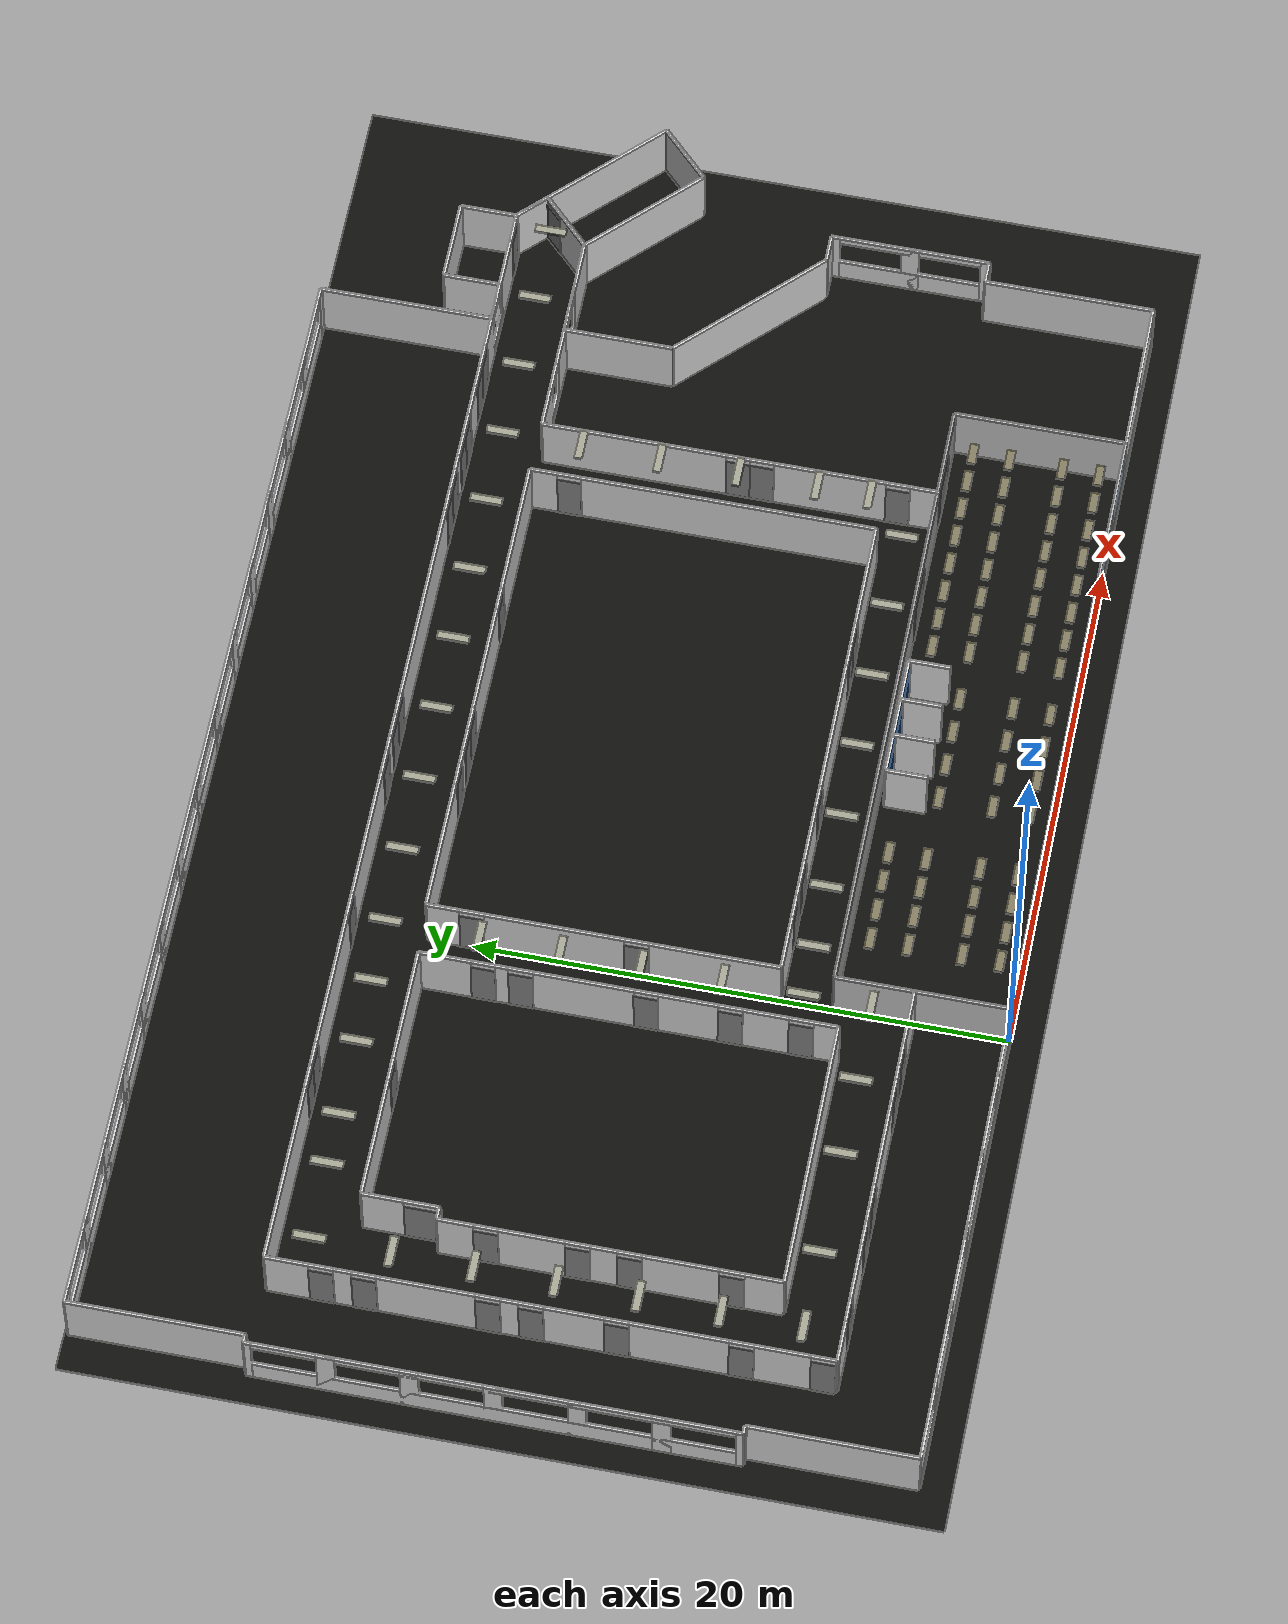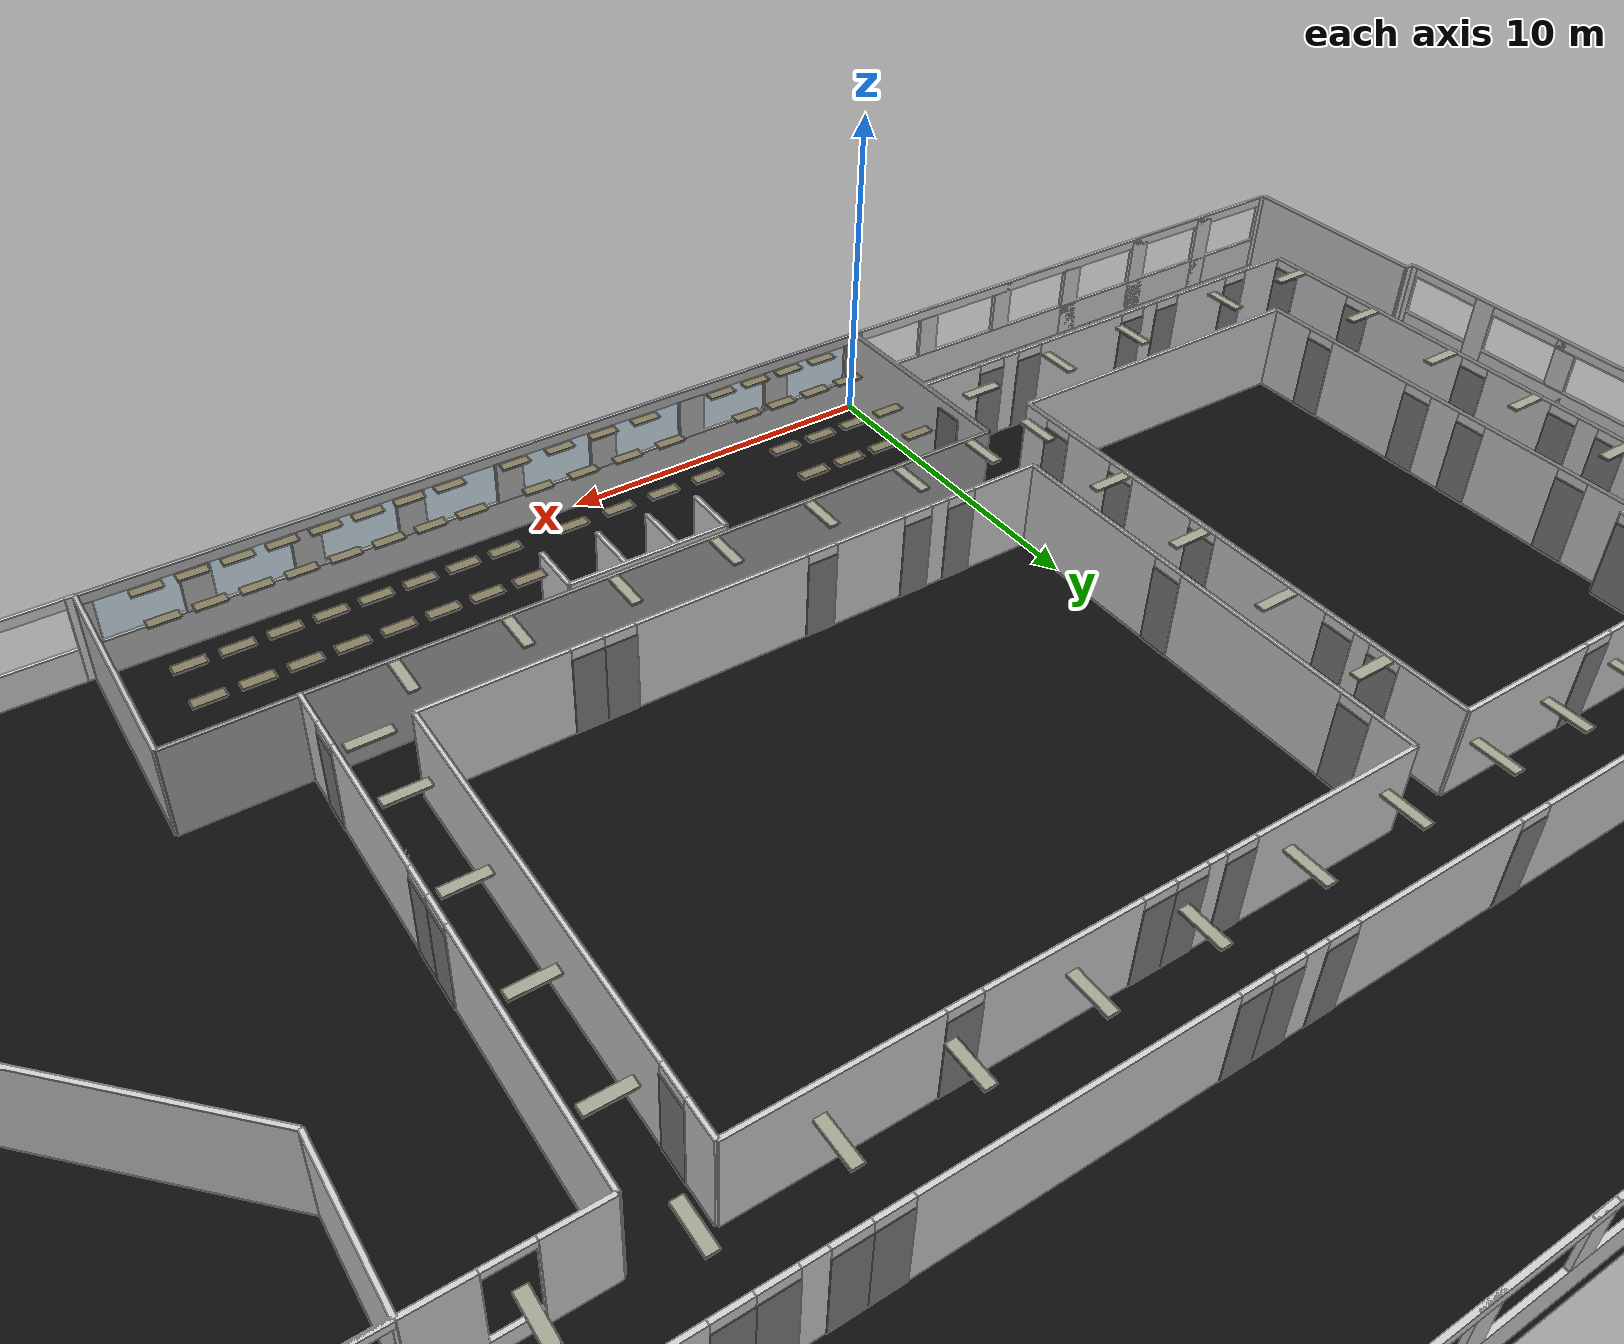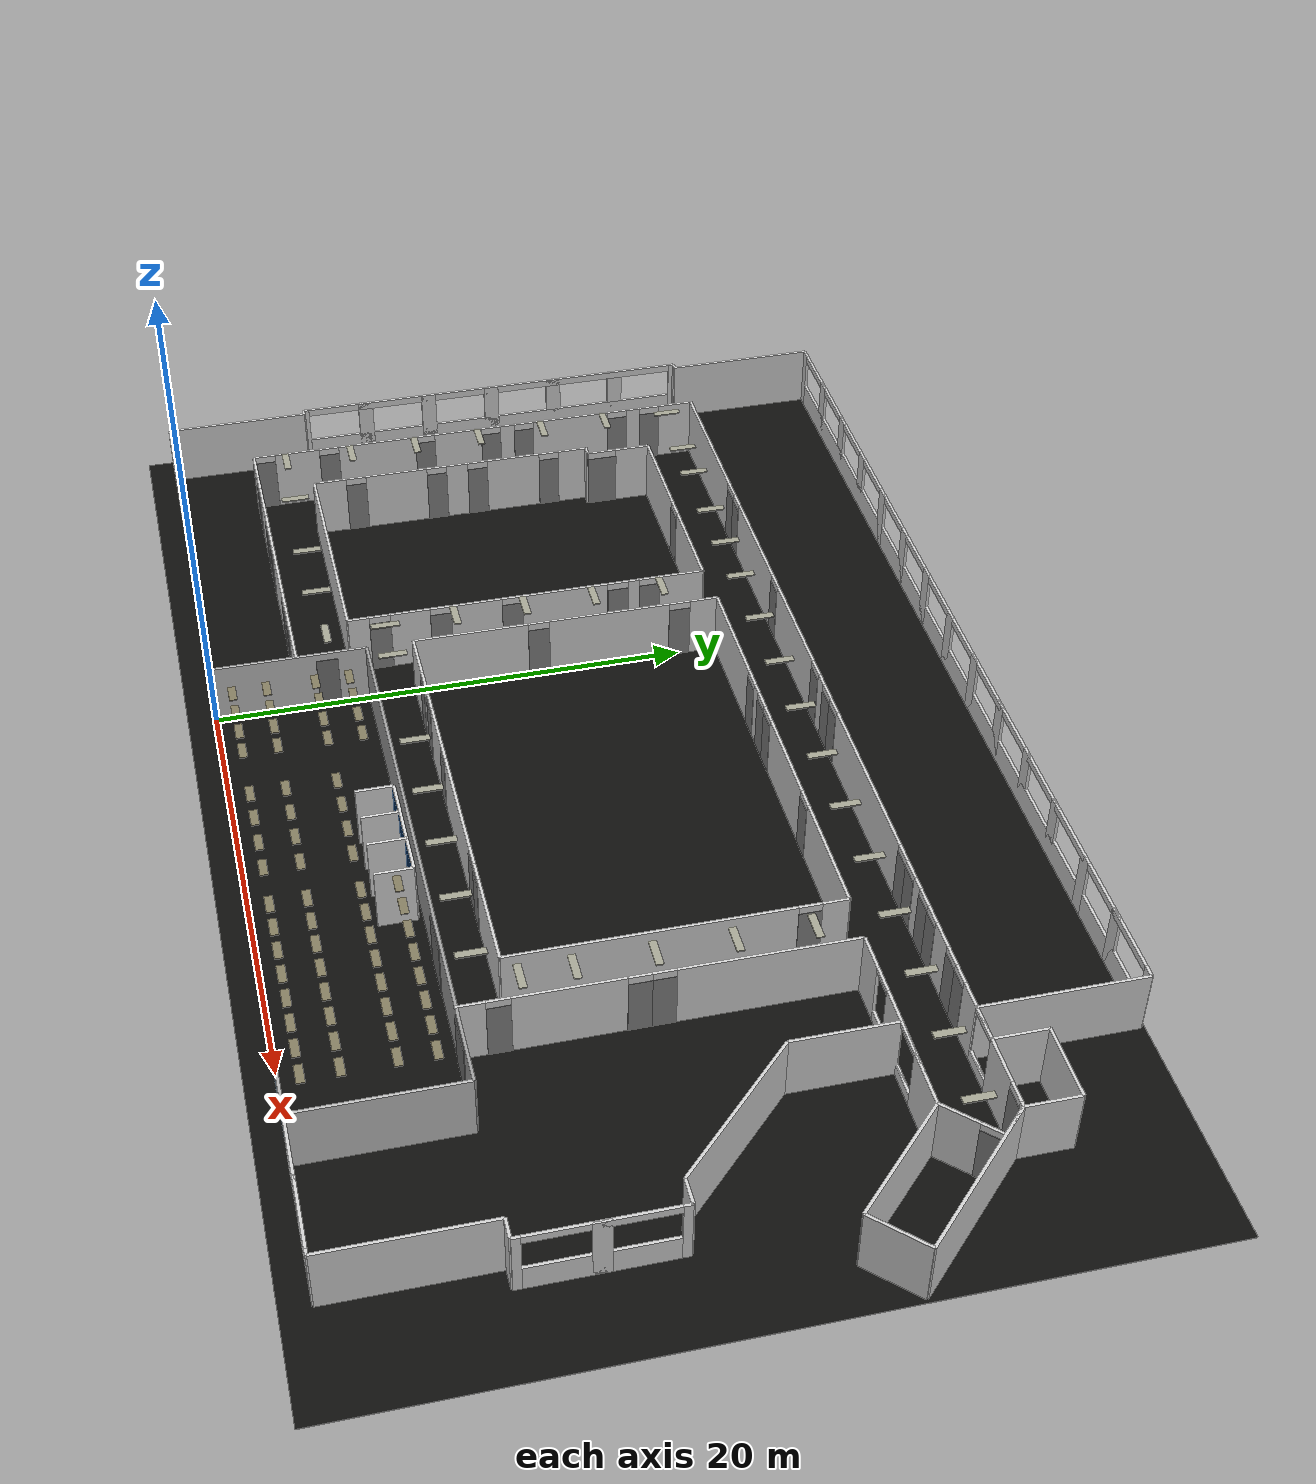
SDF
<?xml version="1.0" ?>
<sdf version="1.10">
  <world name="fourth_floor">

    <plugin filename="gz-sim-physics-system" name="gz::sim::systems::Physics"/>
    <plugin filename="gz-sim-user-commands-system" name="gz::sim::systems::UserCommands"/>
    <plugin filename="gz-sim-scene-broadcaster-system" name="gz::sim::systems::SceneBroadcaster"/>
    <plugin filename="gz-sim-sensors-system" name="gz::sim::systems::Sensors">
    <render_engine>ogre2</render_engine>
  </plugin>

    <gravity>0 0 -9.8</gravity>

    <scene>
      <ambient>0.68 0.68 0.68 1</ambient>
      <background>0.82 0.86 0.9 1</background>
      <shadows>true</shadows>
      <grid>false</grid>
    </scene>

    <gui fullscreen="0">
      <camera name="user_camera">
        <pose>12 -10 8 0.7 0 1.15</pose>
      </camera>
    </gui>

    <!-- fourth-floor model -->
    <include>
      <uri>model://fourth_floor</uri>
      <pose>0 0 0 0 0 0</pose>
    </include>

    <include>
      <uri>model://ackermann_car</uri>
      <pose>20 10 0 0 0 1.57</pose>
    </include>

    <light name="main_light" type="directional">
      <pose>0 0 10 0 0 0</pose>
      <diffuse>1.0 1.0 0.95 1</diffuse>
      <specular>0.35 0.35 0.32 1</specular>
      <direction>-0.5 0.5 -1</direction>
    </light>

    <!-- Aggregate lighting models generated from original fixture/light-source positions -->
    <include>
      <name>room_fluorescent_lights</name>
      <uri>model://room_fluorescent_lights</uri>
      <pose>0 0 0 0 0 0</pose>
    </include>

    <include>
      <name>hallway_fluorescent_lights</name>
      <uri>model://hallway_fluorescent_lights</uri>
      <pose>0 0 0 0 0 0</pose>
    </include>

    <!-- Floor: black, reflective -->
    <model name="room_427_floor">
      <static>true</static>
      <pose>7.5 15 0 0 0 0</pose>
      <link name="floor_link">
        <collision name="floor_collision">
          <geometry><box><size>54.1325 32.3961 0.03</size></box></geometry>
        </collision>
        <visual name="floor_visual">
          <geometry><box><size>54.1325 32.3961 0.03</size></box></geometry>
          <material>
            <ambient>0.01 0.01 0.01 1</ambient>
            <diffuse>0.055 0.055 0.052 1</diffuse>
            <specular>0.45 0.45 0.42 1</specular>
            <pbr>
              <metal>
                <metalness>0.0</metalness>
                <roughness>0.28</roughness>
              </metal>
            </pbr>
          </material>
        </visual>
      </link>
    </model>

    <model name="back_wall_D_C">
      <static>true</static>
      <pose>12.1 6.54 1.375 0 0 0</pose>
      <link name="link">
        <collision name="collision">
          <geometry><box><size>24.2 0.12 2.75</size></box></geometry>
        </collision>
        <visual name="visual">
          <geometry><box><size>24.2 0.12 2.75</size></box></geometry>
          <material>
            <ambient>0.62 0.62 0.62 1</ambient>
            <diffuse>0.62 0.62 0.62 1</diffuse>

          </material>

        </visual>
      </link>
    </model>

    <model name="wall_A_C_solid_no_door">
      <static>true</static>
      <pose>24.2 3.27 1.375 0 0 0</pose>
      <link name="link">
        <collision name="collision">
          <geometry><box><size>0.12 6.54 2.75</size></box></geometry>
        </collision>
        <visual name="visual">
          <geometry><box><size>0.12 6.54 2.75</size></box></geometry>
          <material>
            <ambient>0.75 0.75 0.75 1</ambient>
            <diffuse>0.75 0.75 0.75 1</diffuse>

          </material>

        </visual>
      </link>
    </model>
    <!-- B-D wall: solid wall; Door 3 is shown as a gray door panel near D -->
    <model name="B_D_wall_solid_with_door3_panel">
      <static>true</static>
      <pose>0 3.27 1.375 0 0 0</pose>
      <link name="wall_B_D_solid">
        <collision name="collision">
          <geometry><box><size>0.12 6.54 2.75</size></box></geometry>
        </collision>
        <visual name="visual">
          <geometry><box><size>0.12 6.54 2.75</size></box></geometry>
          <material>
            <ambient>0.75 0.75 0.75 1</ambient>
            <diffuse>0.75 0.75 0.75 1</diffuse>
          </material>
        </visual>
      </link>
      <link name="door_3_panel_near_D">
        <pose>0.065 1.5682 -0.16 0 0 0</pose>
        <visual name="visual">
          <geometry><box><size>0.04 0.9144 2.43</size></box></geometry>
          <material>
            <ambient>0.45 0.45 0.45 1</ambient>
            <diffuse>0.45 0.45 0.45 1</diffuse>
          </material>
        </visual>
      </link>
    </model>

    <model name="window_wall_lower_A_B">
      <static>true</static>
      <pose>12.1 0 0.545 0 0 0</pose>
      <link name="link">
        <collision name="collision">
          <geometry><box><size>24.2 0.12 1.09</size></box></geometry>
        </collision>
        <visual name="visual">
          <geometry><box><size>24.2 0.12 1.09</size></box></geometry>
          <material>
            <ambient>0.7 0.7 0.7 1</ambient>
            <diffuse>0.7 0.7 0.7 1</diffuse>

          </material>

        </visual>
      </link>
    </model>

    <model name="window_wall_top_A_B">
      <static>true</static>
      <pose>12.1 0 2.5925 0 0 0</pose>
      <link name="link">
        <collision name="collision">
          <geometry><box><size>24.2 0.12 0.305</size></box></geometry>
        </collision>
        <visual name="visual">
          <geometry><box><size>24.2 0.12 0.305</size></box></geometry>
          <material>
            <ambient>0.7 0.7 0.7 1</ambient>
            <diffuse>0.7 0.7 0.7 1</diffuse>

          </material>

        </visual>
      </link>
    </model>

    <model name="window_wall_vertical_pieces">
      <static>true</static>

      <link name="window_side_left">
        <pose>0.1725 0 1.765 0 0 0</pose>
        <collision name="collision">
          <geometry><box><size>0.345 0.12 1.35</size></box></geometry>
        </collision>
        <visual name="visual">
          <geometry><box><size>0.345 0.12 1.35</size></box></geometry>
          <material>
            <ambient>0.7 0.7 0.7 1</ambient>
            <diffuse>0.7 0.7 0.7 1</diffuse>

          </material>

        </visual>
      </link>

      <link name="window_gap_1">
        <pose>2.97 0 1.765 0 0 0</pose>
        <collision name="collision">
          <geometry><box><size>0.83 0.12 1.35</size></box></geometry>
        </collision>
        <visual name="visual">
          <geometry><box><size>0.83 0.12 1.35</size></box></geometry>
          <material>
            <ambient>0.7 0.7 0.7 1</ambient>
            <diffuse>0.7 0.7 0.7 1</diffuse>

          </material>

        </visual>
      </link>

      <link name="window_gap_2">
        <pose>6.01 0 1.765 0 0 0</pose>
        <collision name="collision">
          <geometry><box><size>0.83 0.12 1.35</size></box></geometry>
        </collision>
        <visual name="visual">
          <geometry><box><size>0.83 0.12 1.35</size></box></geometry>
          <material>
            <ambient>0.7 0.7 0.7 1</ambient>
            <diffuse>0.7 0.7 0.7 1</diffuse>

          </material>

        </visual>
      </link>

      <link name="window_gap_3">
        <pose>9.05 0 1.765 0 0 0</pose>
        <collision name="collision">
          <geometry><box><size>0.83 0.12 1.35</size></box></geometry>
        </collision>
        <visual name="visual">
          <geometry><box><size>0.83 0.12 1.35</size></box></geometry>
          <material>
            <ambient>0.7 0.7 0.7 1</ambient>
            <diffuse>0.7 0.7 0.7 1</diffuse>

          </material>

        </visual>
      </link>

      <link name="window_gap_4">
        <pose>12.09 0 1.765 0 0 0</pose>
        <collision name="collision">
          <geometry><box><size>0.83 0.12 1.35</size></box></geometry>
        </collision>
        <visual name="visual">
          <geometry><box><size>0.83 0.12 1.35</size></box></geometry>
          <material>
            <ambient>0.7 0.7 0.7 1</ambient>
            <diffuse>0.7 0.7 0.7 1</diffuse>

          </material>

        </visual>
      </link>

      <link name="window_gap_5">
        <pose>15.13 0 1.765 0 0 0</pose>
        <collision name="collision">
          <geometry><box><size>0.83 0.12 1.35</size></box></geometry>
        </collision>
        <visual name="visual">
          <geometry><box><size>0.83 0.12 1.35</size></box></geometry>
          <material>
            <ambient>0.7 0.7 0.7 1</ambient>
            <diffuse>0.7 0.7 0.7 1</diffuse>

          </material>

        </visual>
      </link>

      <link name="window_gap_6">
        <pose>18.17 0 1.765 0 0 0</pose>
        <collision name="collision">
          <geometry><box><size>0.83 0.12 1.35</size></box></geometry>
        </collision>
        <visual name="visual">
          <geometry><box><size>0.83 0.12 1.35</size></box></geometry>
          <material>
            <ambient>0.7 0.7 0.7 1</ambient>
            <diffuse>0.7 0.7 0.7 1</diffuse>

          </material>

        </visual>
      </link>

      <link name="window_gap_7">
        <pose>21.21 0 1.765 0 0 0</pose>
        <collision name="collision">
          <geometry><box><size>0.83 0.12 1.35</size></box></geometry>
        </collision>
        <visual name="visual">
          <geometry><box><size>0.83 0.12 1.35</size></box></geometry>
          <material>
            <ambient>0.7 0.7 0.7 1</ambient>
            <diffuse>0.7 0.7 0.7 1</diffuse>

          </material>

        </visual>
      </link>

      <link name="window_side_right">
        <pose>24.0175 0 1.765 0 0 0</pose>
        <collision name="collision">
          <geometry><box><size>0.365 0.12 1.35</size></box></geometry>
        </collision>
        <visual name="visual">
          <geometry><box><size>0.365 0.12 1.35</size></box></geometry>
          <material>
            <ambient>0.7 0.7 0.7 1</ambient>
            <diffuse>0.7 0.7 0.7 1</diffuse>

          </material>

        </visual>
      </link>
    </model>

    <model name="window_glass_panes">
      <static>true</static>

      <link name="window_1">
        <pose>1.45 -0.07 1.765 0 0 0</pose>
        <visual name="visual">
          <geometry><box><size>2.21 0.03 1.35</size></box></geometry>
          <material>
            <ambient>0.55 0.75 0.9 0.35</ambient>
            <diffuse>0.55 0.75 0.9 0.35</diffuse>
            <specular>0.8 0.8 0.8 1</specular>

          </material>
          <transparency>0.55</transparency>
        </visual>
      </link>

      <link name="window_2">
        <pose>4.49 -0.07 1.765 0 0 0</pose>
        <visual name="visual">
          <geometry><box><size>2.21 0.03 1.35</size></box></geometry>
          <material>
            <ambient>0.55 0.75 0.9 0.35</ambient>
            <diffuse>0.55 0.75 0.9 0.35</diffuse>
            <specular>0.8 0.8 0.8 1</specular>

          </material>
          <transparency>0.55</transparency>
        </visual>
      </link>

      <link name="window_3">
        <pose>7.53 -0.07 1.765 0 0 0</pose>
        <visual name="visual">
          <geometry><box><size>2.21 0.03 1.35</size></box></geometry>
          <material>
            <ambient>0.55 0.75 0.9 0.35</ambient>
            <diffuse>0.55 0.75 0.9 0.35</diffuse>
            <specular>0.8 0.8 0.8 1</specular>

          </material>
          <transparency>0.55</transparency>
        </visual>
      </link>

      <link name="window_4">
        <pose>10.57 -0.07 1.765 0 0 0</pose>
        <visual name="visual">
          <geometry><box><size>2.21 0.03 1.35</size></box></geometry>
          <material>
            <ambient>0.55 0.75 0.9 0.35</ambient>
            <diffuse>0.55 0.75 0.9 0.35</diffuse>
            <specular>0.8 0.8 0.8 1</specular>

          </material>
          <transparency>0.55</transparency>
        </visual>
      </link>

      <link name="window_5">
        <pose>13.61 -0.07 1.765 0 0 0</pose>
        <visual name="visual">
          <geometry><box><size>2.21 0.03 1.35</size></box></geometry>
          <material>
            <ambient>0.55 0.75 0.9 0.35</ambient>
            <diffuse>0.55 0.75 0.9 0.35</diffuse>
            <specular>0.8 0.8 0.8 1</specular>

          </material>
          <transparency>0.55</transparency>
        </visual>
      </link>

      <link name="window_6">
        <pose>16.65 -0.07 1.765 0 0 0</pose>
        <visual name="visual">
          <geometry><box><size>2.21 0.03 1.35</size></box></geometry>
          <material>
            <ambient>0.55 0.75 0.9 0.35</ambient>
            <diffuse>0.55 0.75 0.9 0.35</diffuse>
            <specular>0.8 0.8 0.8 1</specular>

          </material>
          <transparency>0.55</transparency>
        </visual>
      </link>

      <link name="window_7">
        <pose>19.69 -0.07 1.765 0 0 0</pose>
        <visual name="visual">
          <geometry><box><size>2.21 0.03 1.35</size></box></geometry>
          <material>
            <ambient>0.55 0.75 0.9 0.35</ambient>
            <diffuse>0.55 0.75 0.9 0.35</diffuse>
            <specular>0.8 0.8 0.8 1</specular>

          </material>
          <transparency>0.55</transparency>
        </visual>
      </link>

      <link name="window_8">
        <pose>22.73 -0.07 1.765 0 0 0</pose>
        <visual name="visual">
          <geometry><box><size>2.21 0.03 1.35</size></box></geometry>
          <material>
            <ambient>0.55 0.75 0.9 0.35</ambient>
            <diffuse>0.55 0.75 0.9 0.35</diffuse>
            <specular>0.8 0.8 0.8 1</specular>

          </material>
          <transparency>0.55</transparency>
        </visual>
      </link>
    </model>

    <model name="doors_and_connected_boxes_on_D_C_wall">
      <static>true</static>

      <link name="door_1_panel_D_C_wall">
        <pose>21.7 6.47 1.215 0 0 0</pose>
        <visual name="visual">
          <geometry><box><size>1.72 0.04 2.43</size></box></geometry>
          <material>
            <ambient>0.45 0.45 0.45 1</ambient>
            <diffuse>0.45 0.45 0.45 1</diffuse>

          </material>

        </visual>
      </link>

      <link name="door_2_panel_D_C_wall">
        <pose>16.65 6.47 1.215 0 0 0</pose>
        <visual name="visual">
          <geometry><box><size>1.83 0.04 2.43</size></box></geometry>
          <material>
            <ambient>0.45 0.45 0.45 1</ambient>
            <diffuse>0.45 0.45 0.45 1</diffuse>

          </material>

        </visual>
      </link>

      <link name="boxes_back_wall">
        <pose>11.1 6.27 1.375 0 0 0</pose>
        <collision name="collision">
          <geometry><box><size>4.699 0.12 2.75</size></box></geometry>
        </collision>
        <visual name="visual">
          <geometry><box><size>4.699 0.12 2.75</size></box></geometry>
          <material>
            <ambient>0.85 0.85 0.85 1</ambient>
            <diffuse>0.85 0.85 0.85 1</diffuse>

          </material>

        </visual>
      </link>

      <link name="boxes_left_side">
        <pose>8.75 5.50 1.375 0 0 0</pose>
        <collision name="collision">
          <geometry><box><size>0.127 1.549 2.75</size></box></geometry>
        </collision>
        <visual name="visual">
          <geometry><box><size>0.127 1.549 2.75</size></box></geometry>
          <material>
            <ambient>0.85 0.85 0.85 1</ambient>
            <diffuse>0.85 0.85 0.85 1</diffuse>

          </material>

        </visual>
      </link>

      <link name="boxes_divider_1">
        <pose>10.27 5.50 1.375 0 0 0</pose>
        <collision name="collision">
          <geometry><box><size>0.127 1.549 2.75</size></box></geometry>
        </collision>
        <visual name="visual">
          <geometry><box><size>0.127 1.549 2.75</size></box></geometry>
          <material>
            <ambient>0.85 0.85 0.85 1</ambient>
            <diffuse>0.85 0.85 0.85 1</diffuse>

          </material>

        </visual>
      </link>

      <link name="boxes_divider_2">
        <pose>11.79 5.50 1.375 0 0 0</pose>
        <collision name="collision">
          <geometry><box><size>0.127 1.549 2.75</size></box></geometry>
        </collision>
        <visual name="visual">
          <geometry><box><size>0.127 1.549 2.75</size></box></geometry>
          <material>
            <ambient>0.85 0.85 0.85 1</ambient>
            <diffuse>0.85 0.85 0.85 1</diffuse>

          </material>

        </visual>
      </link>

      <link name="boxes_right_side">
        <pose>13.45 5.50 1.375 0 0 0</pose>
        <collision name="collision">
          <geometry><box><size>0.127 1.549 2.75</size></box></geometry>
        </collision>
        <visual name="visual">
          <geometry><box><size>0.127 1.549 2.75</size></box></geometry>
          <material>
            <ambient>0.85 0.85 0.85 1</ambient>
            <diffuse>0.85 0.85 0.85 1</diffuse>

          </material>

        </visual>
      </link>

      <link name="box_1_blue_panel">
        <pose>9.51 6.20 1.35 0 0 0</pose>
        <visual name="visual">
          <geometry><box><size>1.397 0.03 2.50</size></box></geometry>
          <material>
            <ambient>0.0 0.16 0.35 1</ambient>
            <diffuse>0.0 0.16 0.35 1</diffuse>

          </material>

        </visual>
      </link>

      <link name="box_2_blue_panel">
        <pose>11.03 6.20 1.35 0 0 0</pose>
        <visual name="visual">
          <geometry><box><size>1.397 0.03 2.50</size></box></geometry>
          <material>
            <ambient>0.0 0.16 0.35 1</ambient>
            <diffuse>0.0 0.16 0.35 1</diffuse>
          </material>

        </visual>
      </link>

      <link name="box_3_blue_panel">
        <pose>12.55 6.20 1.35 0 0 0</pose>
        <visual name="visual">
          <geometry><box><size>1.397 0.03 2.50</size></box></geometry>
          <material>
            <ambient>0.0 0.16 0.35 1</ambient>
            <diffuse>0.0 0.16 0.35 1</diffuse>

          </material>

        </visual>
      </link>
    </model>

  </world>
</sdf>

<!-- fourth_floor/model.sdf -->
<sdf version="1.10">
  <model name="fourth_floor">
    <static>true</static>

    <link name="exteriors_001_solid">
      <pose>-0.1270 0.0000 1.3750 0 0 3.141593</pose>

      <collision name="exteriors_001_solid_collision">
        <geometry>
          <box>
            <size>0.2540 0.1199 2.7501</size>
          </box>
        </geometry>
      </collision>

      <visual name="exteriors_001_solid_visual">
        <geometry>
          <box>
            <size>0.2540 0.1199 2.7501</size>
          </box>
        </geometry>
        <material>
          <ambient>0.82 0.82 0.82 1</ambient>
          <diffuse>0.82 0.82 0.82 1</diffuse>

        </material>
      </visual>
    </link>

    <link name="exteriors_002_windows_block_lower_strip">
      <pose>-9.0583 0.0000 0.5461 0 0 3.141593</pose>

      <collision name="exteriors_002_windows_block_lower_strip_collision">
        <geometry>
          <box>
            <size>17.6086 0.1199 1.0922</size>
          </box>
        </geometry>
      </collision>

      <visual name="exteriors_002_windows_block_lower_strip_visual">
        <geometry>
          <box>
            <size>17.6086 0.1199 1.0922</size>
          </box>
        </geometry>
        <material>
          <ambient>0.82 0.82 0.82 1</ambient>
          <diffuse>0.82 0.82 0.82 1</diffuse>

        </material>
      </visual>
    </link>

    <link name="exteriors_002_windows_block_upper_strip">
      <pose>-9.0583 0.0000 2.5942 0 0 3.141593</pose>

      <collision name="exteriors_002_windows_block_upper_strip_collision">
        <geometry>
          <box>
            <size>17.6086 0.1199 0.3117</size>
          </box>
        </geometry>
      </collision>

      <visual name="exteriors_002_windows_block_upper_strip_visual">
        <geometry>
          <box>
            <size>17.6086 0.1199 0.3117</size>
          </box>
        </geometry>
        <material>
          <ambient>0.82 0.82 0.82 1</ambient>
          <diffuse>0.82 0.82 0.82 1</diffuse>

        </material>
      </visual>
    </link>

    <link name="exteriors_002_windows_block_post_1">
      <pose>-2.9623 0.0000 1.3750 0 0 3.141593</pose>

      <collision name="exteriors_002_windows_block_post_1_collision">
        <geometry>
          <box>
            <size>0.6794 0.1199 2.7501</size>
          </box>
        </geometry>
      </collision>

      <visual name="exteriors_002_windows_block_post_1_visual">
        <geometry>
          <box>
            <size>0.6794 0.1199 2.7501</size>
          </box>
        </geometry>
        <material>
          <ambient>0.82 0.82 0.82 1</ambient>
          <diffuse>0.82 0.82 0.82 1</diffuse>

        </material>
      </visual>
    </link>

    <link name="exteriors_002_windows_block_post_2">
      <pose>-6.0103 0.0000 1.3750 0 0 3.141593</pose>

      <collision name="exteriors_002_windows_block_post_2_collision">
        <geometry>
          <box>
            <size>0.6794 0.1199 2.7501</size>
          </box>
        </geometry>
      </collision>

      <visual name="exteriors_002_windows_block_post_2_visual">
        <geometry>
          <box>
            <size>0.6794 0.1199 2.7501</size>
          </box>
        </geometry>
        <material>
          <ambient>0.82 0.82 0.82 1</ambient>
          <diffuse>0.82 0.82 0.82 1</diffuse>

        </material>
      </visual>
    </link>

    <link name="exteriors_002_windows_block_post_3">
      <pose>-9.0583 0.0000 1.3750 0 0 3.141593</pose>

      <collision name="exteriors_002_windows_block_post_3_collision">
        <geometry>
          <box>
            <size>0.6794 0.1199 2.7501</size>
          </box>
        </geometry>
      </collision>

      <visual name="exteriors_002_windows_block_post_3_visual">
        <geometry>
          <box>
            <size>0.6794 0.1199 2.7501</size>
          </box>
        </geometry>
        <material>
          <ambient>0.82 0.82 0.82 1</ambient>
          <diffuse>0.82 0.82 0.82 1</diffuse>

        </material>
      </visual>
    </link>

    <link name="exteriors_002_windows_block_post_4">
      <pose>-12.1063 0.0000 1.3750 0 0 3.141593</pose>

      <collision name="exteriors_002_windows_block_post_4_collision">
        <geometry>
          <box>
            <size>0.6794 0.1199 2.7501</size>
          </box>
        </geometry>
      </collision>

      <visual name="exteriors_002_windows_block_post_4_visual">
        <geometry>
          <box>
            <size>0.6794 0.1199 2.7501</size>
          </box>
        </geometry>
        <material>
          <ambient>0.82 0.82 0.82 1</ambient>
          <diffuse>0.82 0.82 0.82 1</diffuse>

        </material>
      </visual>
    </link>

    <link name="exteriors_002_windows_block_post_5">
      <pose>-15.1543 0.0000 1.3750 0 0 3.141593</pose>

      <collision name="exteriors_002_windows_block_post_5_collision">
        <geometry>
          <box>
            <size>0.6794 0.1199 2.7501</size>
          </box>
        </geometry>
      </collision>

      <visual name="exteriors_002_windows_block_post_5_visual">
        <geometry>
          <box>
            <size>0.6794 0.1199 2.7501</size>
          </box>
        </geometry>
        <material>
          <ambient>0.82 0.82 0.82 1</ambient>
          <diffuse>0.82 0.82 0.82 1</diffuse>

        </material>
      </visual>
    </link>

    <link name="exteriors_003_solid">
      <pose>-17.9895 0.0000 1.3750 0 0 3.141593</pose>

      <collision name="exteriors_003_solid_collision">
        <geometry>
          <box>
            <size>0.2540 0.1199 2.7501</size>
          </box>
        </geometry>
      </collision>

      <visual name="exteriors_003_solid_visual">
        <geometry>
          <box>
            <size>0.2540 0.1199 2.7501</size>
          </box>
        </geometry>
        <material>
          <ambient>0.82 0.82 0.82 1</ambient>
          <diffuse>0.82 0.82 0.82 1</diffuse>

        </material>
      </visual>
    </link>

    <link name="exteriors_005_solid">
      <pose>-18.1166 3.1623 1.3750 0 0 1.570796</pose>

      <collision name="exteriors_005_solid_collision">
        <geometry>
          <box>
            <size>6.3246 0.1199 2.7501</size>
          </box>
        </geometry>
      </collision>

      <visual name="exteriors_005_solid_visual">
        <geometry>
          <box>
            <size>6.3246 0.1199 2.7501</size>
          </box>
        </geometry>
        <material>
          <ambient>0.82 0.82 0.82 1</ambient>
          <diffuse>0.82 0.82 0.82 1</diffuse>

        </material>
      </visual>
    </link>

    <link name="exteriors_007_solid">
      <pose>-18.2690 6.3246 1.3750 0 0 3.141593</pose>

      <collision name="exteriors_007_solid_collision">
        <geometry>
          <box>
            <size>0.3048 0.1199 2.7501</size>
          </box>
        </geometry>
      </collision>

      <visual name="exteriors_007_solid_visual">
        <geometry>
          <box>
            <size>0.3048 0.1199 2.7501</size>
          </box>
        </geometry>
        <material>
          <ambient>0.82 0.82 0.82 1</ambient>
          <diffuse>0.82 0.82 0.82 1</diffuse>

        </material>
      </visual>
    </link>

    <link name="exteriors_009_solid">
      <pose>-18.4214 6.4516 1.3750 0 0 1.570796</pose>

      <collision name="exteriors_009_solid_collision">
        <geometry>
          <box>
            <size>0.2540 0.1199 2.7501</size>
          </box>
        </geometry>
      </collision>

      <visual name="exteriors_009_solid_visual">
        <geometry>
          <box>
            <size>0.2540 0.1199 2.7501</size>
          </box>
        </geometry>
        <material>
          <ambient>0.82 0.82 0.82 1</ambient>
          <diffuse>0.82 0.82 0.82 1</diffuse>

        </material>
      </visual>
    </link>

    <link name="exteriors_010_windows_block_lower_strip">
      <pose>-18.4214 15.3829 0.5461 0 0 1.570796</pose>

      <collision name="exteriors_010_windows_block_lower_strip_collision">
        <geometry>
          <box>
            <size>17.6086 0.1199 1.0922</size>
          </box>
        </geometry>
      </collision>

      <visual name="exteriors_010_windows_block_lower_strip_visual">
        <geometry>
          <box>
            <size>17.6086 0.1199 1.0922</size>
          </box>
        </geometry>
        <material>
          <ambient>0.82 0.82 0.82 1</ambient>
          <diffuse>0.82 0.82 0.82 1</diffuse>

        </material>
      </visual>
    </link>

    <link name="exteriors_010_windows_block_upper_strip">
      <pose>-18.4214 15.3829 2.5942 0 0 1.570796</pose>

      <collision name="exteriors_010_windows_block_upper_strip_collision">
        <geometry>
          <box>
            <size>17.6086 0.1199 0.3117</size>
          </box>
        </geometry>
      </collision>

      <visual name="exteriors_010_windows_block_upper_strip_visual">
        <geometry>
          <box>
            <size>17.6086 0.1199 0.3117</size>
          </box>
        </geometry>
        <material>
          <ambient>0.82 0.82 0.82 1</ambient>
          <diffuse>0.82 0.82 0.82 1</diffuse>

        </material>
      </visual>
    </link>

    <link name="exteriors_010_windows_block_post_1">
      <pose>-18.4214 9.2869 1.3750 0 0 1.570796</pose>

      <collision name="exteriors_010_windows_block_post_1_collision">
        <geometry>
          <box>
            <size>0.6794 0.1199 2.7501</size>
          </box>
        </geometry>
      </collision>

      <visual name="exteriors_010_windows_block_post_1_visual">
        <geometry>
          <box>
            <size>0.6794 0.1199 2.7501</size>
          </box>
        </geometry>
        <material>
          <ambient>0.82 0.82 0.82 1</ambient>
          <diffuse>0.82 0.82 0.82 1</diffuse>

        </material>
      </visual>
    </link>

    <link name="exteriors_010_windows_block_post_2">
      <pose>-18.4214 12.3349 1.3750 0 0 1.570796</pose>

      <collision name="exteriors_010_windows_block_post_2_collision">
        <geometry>
          <box>
            <size>0.6794 0.1199 2.7501</size>
          </box>
        </geometry>
      </collision>

      <visual name="exteriors_010_windows_block_post_2_visual">
        <geometry>
          <box>
            <size>0.6794 0.1199 2.7501</size>
          </box>
        </geometry>
        <material>
          <ambient>0.82 0.82 0.82 1</ambient>
          <diffuse>0.82 0.82 0.82 1</diffuse>

        </material>
      </visual>
    </link>

    <link name="exteriors_010_windows_block_post_3">
      <pose>-18.4214 15.3829 1.3750 0 0 1.570796</pose>

      <collision name="exteriors_010_windows_block_post_3_collision">
        <geometry>
          <box>
            <size>0.6794 0.1199 2.7501</size>
          </box>
        </geometry>
      </collision>

      <visual name="exteriors_010_windows_block_post_3_visual">
        <geometry>
          <box>
            <size>0.6794 0.1199 2.7501</size>
          </box>
        </geometry>
        <material>
          <ambient>0.82 0.82 0.82 1</ambient>
          <diffuse>0.82 0.82 0.82 1</diffuse>

        </material>
      </visual>
    </link>

    <link name="exteriors_010_windows_block_post_4">
      <pose>-18.4214 18.4309 1.3750 0 0 1.570796</pose>

      <collision name="exteriors_010_windows_block_post_4_collision">
        <geometry>
          <box>
            <size>0.6794 0.1199 2.7501</size>
          </box>
        </geometry>
      </collision>

      <visual name="exteriors_010_windows_block_post_4_visual">
        <geometry>
          <box>
            <size>0.6794 0.1199 2.7501</size>
          </box>
        </geometry>
        <material>
          <ambient>0.82 0.82 0.82 1</ambient>
          <diffuse>0.82 0.82 0.82 1</diffuse>

        </material>
      </visual>
    </link>

    <link name="exteriors_010_windows_block_post_5">
      <pose>-18.4214 21.4789 1.3750 0 0 1.570796</pose>

      <collision name="exteriors_010_windows_block_post_5_collision">
        <geometry>
          <box>
            <size>0.6794 0.1199 2.7501</size>
          </box>
        </geometry>
      </collision>

      <visual name="exteriors_010_windows_block_post_5_visual">
        <geometry>
          <box>
            <size>0.6794 0.1199 2.7501</size>
          </box>
        </geometry>
        <material>
          <ambient>0.82 0.82 0.82 1</ambient>
          <diffuse>0.82 0.82 0.82 1</diffuse>

        </material>
      </visual>
    </link>

    <link name="exteriors_011_solid">
      <pose>-18.4214 24.3142 1.3750 0 0 1.570796</pose>

      <collision name="exteriors_011_solid_collision">
        <geometry>
          <box>
            <size>0.2540 0.1199 2.7501</size>
          </box>
        </geometry>
      </collision>

      <visual name="exteriors_011_solid_visual">
        <geometry>
          <box>
            <size>0.2540 0.1199 2.7501</size>
          </box>
        </geometry>
        <material>
          <ambient>0.82 0.82 0.82 1</ambient>
          <diffuse>0.82 0.82 0.82 1</diffuse>

        </material>
      </visual>
    </link>

    <link name="exteriors_013_solid">
      <pose>-18.2690 24.4412 1.3750 0 0 0.000000</pose>

      <collision name="exteriors_013_solid_collision">
        <geometry>
          <box>
            <size>0.3048 0.1199 2.7501</size>
          </box>
        </geometry>
      </collision>

      <visual name="exteriors_013_solid_visual">
        <geometry>
          <box>
            <size>0.3048 0.1199 2.7501</size>
          </box>
        </geometry>
        <material>
          <ambient>0.82 0.82 0.82 1</ambient>
          <diffuse>0.82 0.82 0.82 1</diffuse>

        </material>
      </visual>
    </link>

    <link name="exteriors_015_solid">
      <pose>-18.1166 27.7431 1.3750 0 0 1.570796</pose>

      <collision name="exteriors_015_solid_collision">
        <geometry>
          <box>
            <size>6.6040 0.1199 2.7501</size>
          </box>
        </geometry>
      </collision>

      <visual name="exteriors_015_solid_visual">
        <geometry>
          <box>
            <size>6.6040 0.1199 2.7501</size>
          </box>
        </geometry>
        <material>
          <ambient>0.82 0.82 0.82 1</ambient>
          <diffuse>0.82 0.82 0.82 1</diffuse>

        </material>
      </visual>
    </link>

    <link name="exteriors_017_solid">
      <pose>-17.8625 31.0451 1.3750 0 0 0.000000</pose>

      <collision name="exteriors_017_solid_collision">
        <geometry>
          <box>
            <size>0.5080 0.1199 2.7501</size>
          </box>
        </geometry>
      </collision>

      <visual name="exteriors_017_solid_visual">
        <geometry>
          <box>
            <size>0.5080 0.1199 2.7501</size>
          </box>
        </geometry>
        <material>
          <ambient>0.82 0.82 0.82 1</ambient>
          <diffuse>0.82 0.82 0.82 1</diffuse>

        </material>
      </visual>
    </link>

    <link name="exteriors_018_windows_block_lower_strip">
      <pose>3.3877 31.0451 0.5461 0 0 0.000000</pose>

      <collision name="exteriors_018_windows_block_lower_strip_collision">
        <geometry>
          <box>
            <size>41.9926 0.1199 1.0922</size>
          </box>
        </geometry>
      </collision>

      <visual name="exteriors_018_windows_block_lower_strip_visual">
        <geometry>
          <box>
            <size>41.9926 0.1199 1.0922</size>
          </box>
        </geometry>
        <material>
          <ambient>0.82 0.82 0.82 1</ambient>
          <diffuse>0.82 0.82 0.82 1</diffuse>

        </material>
      </visual>
    </link>

    <link name="exteriors_018_windows_block_upper_strip">
      <pose>3.3877 31.0451 2.5942 0 0 0.000000</pose>

      <collision name="exteriors_018_windows_block_upper_strip_collision">
        <geometry>
          <box>
            <size>41.9926 0.1199 0.3117</size>
          </box>
        </geometry>
      </collision>

      <visual name="exteriors_018_windows_block_upper_strip_visual">
        <geometry>
          <box>
            <size>41.9926 0.1199 0.3117</size>
          </box>
        </geometry>
        <material>
          <ambient>0.82 0.82 0.82 1</ambient>
          <diffuse>0.82 0.82 0.82 1</diffuse>

        </material>
      </visual>
    </link>

    <link name="exteriors_018_windows_block_post_1">
      <pose>-14.9003 31.0451 1.3750 0 0 0.000000</pose>

      <collision name="exteriors_018_windows_block_post_1_collision">
        <geometry>
          <box>
            <size>0.6794 0.1199 2.7501</size>
          </box>
        </geometry>
      </collision>

      <visual name="exteriors_018_windows_block_post_1_visual">
        <geometry>
          <box>
            <size>0.6794 0.1199 2.7501</size>
          </box>
        </geometry>
        <material>
          <ambient>0.82 0.82 0.82 1</ambient>
          <diffuse>0.82 0.82 0.82 1</diffuse>

        </material>
      </visual>
    </link>

    <link name="exteriors_018_windows_block_post_2">
      <pose>-11.8523 31.0451 1.3750 0 0 0.000000</pose>

      <collision name="exteriors_018_windows_block_post_2_collision">
        <geometry>
          <box>
            <size>0.6794 0.1199 2.7501</size>
          </box>
        </geometry>
      </collision>

      <visual name="exteriors_018_windows_block_post_2_visual">
        <geometry>
          <box>
            <size>0.6794 0.1199 2.7501</size>
          </box>
        </geometry>
        <material>
          <ambient>0.82 0.82 0.82 1</ambient>
          <diffuse>0.82 0.82 0.82 1</diffuse>

        </material>
      </visual>
    </link>

    <link name="exteriors_018_windows_block_post_3">
      <pose>-8.8043 31.0451 1.3750 0 0 0.000000</pose>

      <collision name="exteriors_018_windows_block_post_3_collision">
        <geometry>
          <box>
            <size>0.6794 0.1199 2.7501</size>
          </box>
        </geometry>
      </collision>

      <visual name="exteriors_018_windows_block_post_3_visual">
        <geometry>
          <box>
            <size>0.6794 0.1199 2.7501</size>
          </box>
        </geometry>
        <material>
          <ambient>0.82 0.82 0.82 1</ambient>
          <diffuse>0.82 0.82 0.82 1</diffuse>

        </material>
      </visual>
    </link>

    <link name="exteriors_018_windows_block_post_4">
      <pose>-5.7563 31.0451 1.3750 0 0 0.000000</pose>

      <collision name="exteriors_018_windows_block_post_4_collision">
        <geometry>
          <box>
            <size>0.6794 0.1199 2.7501</size>
          </box>
        </geometry>
      </collision>

      <visual name="exteriors_018_windows_block_post_4_visual">
        <geometry>
          <box>
            <size>0.6794 0.1199 2.7501</size>
          </box>
        </geometry>
        <material>
          <ambient>0.82 0.82 0.82 1</ambient>
          <diffuse>0.82 0.82 0.82 1</diffuse>

        </material>
      </visual>
    </link>

    <link name="exteriors_018_windows_block_post_5">
      <pose>-2.7083 31.0451 1.3750 0 0 0.000000</pose>

      <collision name="exteriors_018_windows_block_post_5_collision">
        <geometry>
          <box>
            <size>0.6794 0.1199 2.7501</size>
          </box>
        </geometry>
      </collision>

      <visual name="exteriors_018_windows_block_post_5_visual">
        <geometry>
          <box>
            <size>0.6794 0.1199 2.7501</size>
          </box>
        </geometry>
        <material>
          <ambient>0.82 0.82 0.82 1</ambient>
          <diffuse>0.82 0.82 0.82 1</diffuse>

        </material>
      </visual>
    </link>

    <link name="exteriors_018_windows_block_post_6">
      <pose>0.3397 31.0451 1.3750 0 0 0.000000</pose>

      <collision name="exteriors_018_windows_block_post_6_collision">
        <geometry>
          <box>
            <size>0.6794 0.1199 2.7501</size>
          </box>
        </geometry>
      </collision>

      <visual name="exteriors_018_windows_block_post_6_visual">
        <geometry>
          <box>
            <size>0.6794 0.1199 2.7501</size>
          </box>
        </geometry>
        <material>
          <ambient>0.82 0.82 0.82 1</ambient>
          <diffuse>0.82 0.82 0.82 1</diffuse>

        </material>
      </visual>
    </link>

    <link name="exteriors_018_windows_block_post_7">
      <pose>3.3877 31.0451 1.3750 0 0 0.000000</pose>

      <collision name="exteriors_018_windows_block_post_7_collision">
        <geometry>
          <box>
            <size>0.6794 0.1199 2.7501</size>
          </box>
        </geometry>
      </collision>

      <visual name="exteriors_018_windows_block_post_7_visual">
        <geometry>
          <box>
            <size>0.6794 0.1199 2.7501</size>
          </box>
        </geometry>
        <material>
          <ambient>0.82 0.82 0.82 1</ambient>
          <diffuse>0.82 0.82 0.82 1</diffuse>

        </material>
      </visual>
    </link>

    <link name="exteriors_018_windows_block_post_8">
      <pose>6.4357 31.0451 1.3750 0 0 0.000000</pose>

      <collision name="exteriors_018_windows_block_post_8_collision">
        <geometry>
          <box>
            <size>0.6794 0.1199 2.7501</size>
          </box>
        </geometry>
      </collision>

      <visual name="exteriors_018_windows_block_post_8_visual">
        <geometry>
          <box>
            <size>0.6794 0.1199 2.7501</size>
          </box>
        </geometry>
        <material>
          <ambient>0.82 0.82 0.82 1</ambient>
          <diffuse>0.82 0.82 0.82 1</diffuse>

        </material>
      </visual>
    </link>

    <link name="exteriors_018_windows_block_post_9">
      <pose>9.4837 31.0451 1.3750 0 0 0.000000</pose>

      <collision name="exteriors_018_windows_block_post_9_collision">
        <geometry>
          <box>
            <size>0.6794 0.1199 2.7501</size>
          </box>
        </geometry>
      </collision>

      <visual name="exteriors_018_windows_block_post_9_visual">
        <geometry>
          <box>
            <size>0.6794 0.1199 2.7501</size>
          </box>
        </geometry>
        <material>
          <ambient>0.82 0.82 0.82 1</ambient>
          <diffuse>0.82 0.82 0.82 1</diffuse>

        </material>
      </visual>
    </link>

    <link name="exteriors_018_windows_block_post_10">
      <pose>12.5317 31.0451 1.3750 0 0 0.000000</pose>

      <collision name="exteriors_018_windows_block_post_10_collision">
        <geometry>
          <box>
            <size>0.6794 0.1199 2.7501</size>
          </box>
        </geometry>
      </collision>

      <visual name="exteriors_018_windows_block_post_10_visual">
        <geometry>
          <box>
            <size>0.6794 0.1199 2.7501</size>
          </box>
        </geometry>
        <material>
          <ambient>0.82 0.82 0.82 1</ambient>
          <diffuse>0.82 0.82 0.82 1</diffuse>

        </material>
      </visual>
    </link>

    <link name="exteriors_018_windows_block_post_11">
      <pose>15.5797 31.0451 1.3750 0 0 0.000000</pose>

      <collision name="exteriors_018_windows_block_post_11_collision">
        <geometry>
          <box>
            <size>0.6794 0.1199 2.7501</size>
          </box>
        </geometry>
      </collision>

      <visual name="exteriors_018_windows_block_post_11_visual">
        <geometry>
          <box>
            <size>0.6794 0.1199 2.7501</size>
          </box>
        </geometry>
        <material>
          <ambient>0.82 0.82 0.82 1</ambient>
          <diffuse>0.82 0.82 0.82 1</diffuse>

        </material>
      </visual>
    </link>

    <link name="exteriors_018_windows_block_post_12">
      <pose>18.6277 31.0451 1.3750 0 0 0.000000</pose>

      <collision name="exteriors_018_windows_block_post_12_collision">
        <geometry>
          <box>
            <size>0.6794 0.1199 2.7501</size>
          </box>
        </geometry>
      </collision>

      <visual name="exteriors_018_windows_block_post_12_visual">
        <geometry>
          <box>
            <size>0.6794 0.1199 2.7501</size>
          </box>
        </geometry>
        <material>
          <ambient>0.82 0.82 0.82 1</ambient>
          <diffuse>0.82 0.82 0.82 1</diffuse>

        </material>
      </visual>
    </link>

    <link name="exteriors_018_windows_block_post_13">
      <pose>21.6757 31.0451 1.3750 0 0 0.000000</pose>

      <collision name="exteriors_018_windows_block_post_13_collision">
        <geometry>
          <box>
            <size>0.6794 0.1199 2.7501</size>
          </box>
        </geometry>
      </collision>

      <visual name="exteriors_018_windows_block_post_13_visual">
        <geometry>
          <box>
            <size>0.6794 0.1199 2.7501</size>
          </box>
        </geometry>
        <material>
          <ambient>0.82 0.82 0.82 1</ambient>
          <diffuse>0.82 0.82 0.82 1</diffuse>

        </material>
      </visual>
    </link>

    <link name="exteriors_019_solid">
      <pose>24.6380 31.0451 1.3750 0 0 0.000000</pose>

      <collision name="exteriors_019_solid_collision">
        <geometry>
          <box>
            <size>0.5080 0.1199 2.7501</size>
          </box>
        </geometry>
      </collision>

      <visual name="exteriors_019_solid_visual">
        <geometry>
          <box>
            <size>0.5080 0.1199 2.7501</size>
          </box>
        </geometry>
        <material>
          <ambient>0.82 0.82 0.82 1</ambient>
          <diffuse>0.82 0.82 0.82 1</diffuse>

        </material>
      </visual>
    </link>

    <link name="exteriors_021_solid">
      <pose>24.8920 27.7431 1.3750 0 0 4.712389</pose>

      <collision name="exteriors_021_solid_collision">
        <geometry>
          <box>
            <size>6.6040 0.1199 2.7501</size>
          </box>
        </geometry>
      </collision>

      <visual name="exteriors_021_solid_visual">
        <geometry>
          <box>
            <size>6.6040 0.1199 2.7501</size>
          </box>
        </geometry>
        <material>
          <ambient>0.82 0.82 0.82 1</ambient>
          <diffuse>0.82 0.82 0.82 1</diffuse>

        </material>
      </visual>
    </link>

    <link name="exteriors_023_windows_block_lower_strip">
      <pose>25.6540 24.4412 0.2540 0 0 0.000000</pose>

      <collision name="exteriors_023_windows_block_lower_strip_collision">
        <geometry>
          <box>
            <size>1.5240 0.1199 0.5080</size>
          </box>
        </geometry>
      </collision>

      <visual name="exteriors_023_windows_block_lower_strip_visual">
        <geometry>
          <box>
            <size>1.5240 0.1199 0.5080</size>
          </box>
        </geometry>
        <material>
          <ambient>0.82 0.82 0.82 1</ambient>
          <diffuse>0.82 0.82 0.82 1</diffuse>

        </material>
      </visual>
    </link>

    <link name="exteriors_023_windows_block_upper_strip">
      <pose>25.6540 24.4412 2.6450 0 0 0.000000</pose>

      <collision name="exteriors_023_windows_block_upper_strip_collision">
        <geometry>
          <box>
            <size>1.5240 0.1199 0.2101</size>
          </box>
        </geometry>
      </collision>

      <visual name="exteriors_023_windows_block_upper_strip_visual">
        <geometry>
          <box>
            <size>1.5240 0.1199 0.2101</size>
          </box>
        </geometry>
        <material>
          <ambient>0.82 0.82 0.82 1</ambient>
          <diffuse>0.82 0.82 0.82 1</diffuse>

        </material>
      </visual>
    </link>

    <link name="exteriors_025_solid">
      <pose>26.4160 25.5206 1.3750 0 0 1.570796</pose>

      <collision name="exteriors_025_solid_collision">
        <geometry>
          <box>
            <size>2.1590 0.1199 2.7501</size>
          </box>
        </geometry>
      </collision>

      <visual name="exteriors_025_solid_visual">
        <geometry>
          <box>
            <size>2.1590 0.1199 2.7501</size>
          </box>
        </geometry>
        <material>
          <ambient>0.82 0.82 0.82 1</ambient>
          <diffuse>0.82 0.82 0.82 1</diffuse>

        </material>
      </visual>
    </link>

    <link name="exteriors_027_solid">
      <pose>27.9781 26.6001 1.3750 0 0 0.000000</pose>

      <collision name="exteriors_027_solid_collision">
        <geometry>
          <box>
            <size>3.1242 0.1199 2.7501</size>
          </box>
        </geometry>
      </collision>

      <visual name="exteriors_027_solid_visual">
        <geometry>
          <box>
            <size>3.1242 0.1199 2.7501</size>
          </box>
        </geometry>
        <material>
          <ambient>0.82 0.82 0.82 1</ambient>
          <diffuse>0.82 0.82 0.82 1</diffuse>

        </material>
      </visual>
    </link>

    <link name="exteriors_029_solid">
      <pose>29.5402 25.5206 1.3750 0 0 4.712389</pose>

      <collision name="exteriors_029_solid_collision">
        <geometry>
          <box>
            <size>2.1590 0.1199 2.7501</size>
          </box>
        </geometry>
      </collision>

      <visual name="exteriors_029_solid_visual">
        <geometry>
          <box>
            <size>2.1590 0.1199 2.7501</size>
          </box>
        </geometry>
        <material>
          <ambient>0.82 0.82 0.82 1</ambient>
          <diffuse>0.82 0.82 0.82 1</diffuse>

        </material>
      </visual>
    </link>

    <link name="exteriors_031_solid">
      <pose>31.9649 22.0165 1.3750 0 0 5.497787</pose>

      <collision name="exteriors_031_solid_collision">
        <geometry>
          <box>
            <size>6.8580 0.1199 2.7501</size>
          </box>
        </geometry>
      </collision>

      <visual name="exteriors_031_solid_visual">
        <geometry>
          <box>
            <size>6.8580 0.1199 2.7501</size>
          </box>
        </geometry>
        <material>
          <ambient>0.82 0.82 0.82 1</ambient>
          <diffuse>0.82 0.82 0.82 1</diffuse>

        </material>
      </visual>
    </link>

    <link name="exteriors_033_solid">
      <pose>33.4915 18.6938 1.3750 0 0 3.926991</pose>

      <collision name="exteriors_033_solid_collision">
        <geometry>
          <box>
            <size>2.5400 0.1199 2.7501</size>
          </box>
        </geometry>
      </collision>

      <visual name="exteriors_033_solid_visual">
        <geometry>
          <box>
            <size>2.5400 0.1199 2.7501</size>
          </box>
        </geometry>
        <material>
          <ambient>0.82 0.82 0.82 1</ambient>
          <diffuse>0.82 0.82 0.82 1</diffuse>

        </material>
      </visual>
    </link>

    <link name="exteriors_035_solid">
      <pose>30.6717 19.7175 1.3750 0 0 2.356194</pose>

      <collision name="exteriors_035_solid_collision">
        <geometry>
          <box>
            <size>5.4356 0.1199 2.7501</size>
          </box>
        </geometry>
      </collision>

      <visual name="exteriors_035_solid_visual">
        <geometry>
          <box>
            <size>5.4356 0.1199 2.7501</size>
          </box>
        </geometry>
        <material>
          <ambient>0.82 0.82 0.82 1</ambient>
          <diffuse>0.82 0.82 0.82 1</diffuse>

        </material>
      </visual>
    </link>

    <link name="exteriors_037_solid">
      <pose>27.6069 21.6393 1.3750 0 0 3.141593</pose>

      <collision name="exteriors_037_solid_collision">
        <geometry>
          <box>
            <size>2.2860 0.1199 2.7501</size>
          </box>
        </geometry>
      </collision>

      <visual name="exteriors_037_solid_visual">
        <geometry>
          <box>
            <size>2.2860 0.1199 2.7501</size>
          </box>
        </geometry>
        <material>
          <ambient>0.82 0.82 0.82 1</ambient>
          <diffuse>0.82 0.82 0.82 1</diffuse>

        </material>
      </visual>
    </link>

    <link name="exteriors_038_windows_block_lower_strip">
      <pose>25.7019 21.6393 0.2540 0 0 3.141593</pose>

      <collision name="exteriors_038_windows_block_lower_strip_collision">
        <geometry>
          <box>
            <size>1.5240 0.1199 0.5080</size>
          </box>
        </geometry>
      </collision>

      <visual name="exteriors_038_windows_block_lower_strip_visual">
        <geometry>
          <box>
            <size>1.5240 0.1199 0.5080</size>
          </box>
        </geometry>
        <material>
          <ambient>0.82 0.82 0.82 1</ambient>
          <diffuse>0.82 0.82 0.82 1</diffuse>

        </material>
      </visual>
    </link>

    <link name="exteriors_038_windows_block_upper_strip">
      <pose>25.7019 21.6393 2.6450 0 0 3.141593</pose>

      <collision name="exteriors_038_windows_block_upper_strip_collision">
        <geometry>
          <box>
            <size>1.5240 0.1199 0.2101</size>
          </box>
        </geometry>
      </collision>

      <visual name="exteriors_038_windows_block_upper_strip_visual">
        <geometry>
          <box>
            <size>1.5240 0.1199 0.2101</size>
          </box>
        </geometry>
        <material>
          <ambient>0.82 0.82 0.82 1</ambient>
          <diffuse>0.82 0.82 0.82 1</diffuse>

        </material>
      </visual>
    </link>

    <link name="exteriors_040_solid">
      <pose>24.9399 19.5565 1.3750 0 0 4.712389</pose>

      <collision name="exteriors_040_solid_collision">
        <geometry>
          <box>
            <size>4.1656 0.1199 2.7501</size>
          </box>
        </geometry>
      </collision>

      <visual name="exteriors_040_solid_visual">
        <geometry>
          <box>
            <size>4.1656 0.1199 2.7501</size>
          </box>
        </geometry>
        <material>
          <ambient>0.82 0.82 0.82 1</ambient>
          <diffuse>0.82 0.82 0.82 1</diffuse>

        </material>
      </visual>
    </link>

    <link name="exteriors_042_solid">
      <pose>27.4185 14.9952 1.3750 0 0 5.497787</pose>

      <collision name="exteriors_042_solid_collision">
        <geometry>
          <box>
            <size>7.0104 0.1199 2.7501</size>
          </box>
        </geometry>
      </collision>

      <visual name="exteriors_042_solid_visual">
        <geometry>
          <box>
            <size>7.0104 0.1199 2.7501</size>
          </box>
        </geometry>
        <material>
          <ambient>0.82 0.82 0.82 1</ambient>
          <diffuse>0.82 0.82 0.82 1</diffuse>

        </material>
      </visual>
    </link>

    <link name="exteriors_044_solid">
      <pose>30.4304 12.5166 1.3750 0 0 0.000000</pose>

      <collision name="exteriors_044_solid_collision">
        <geometry>
          <box>
            <size>1.0668 0.1199 2.7501</size>
          </box>
        </geometry>
      </collision>

      <visual name="exteriors_044_solid_visual">
        <geometry>
          <box>
            <size>1.0668 0.1199 2.7501</size>
          </box>
        </geometry>
        <material>
          <ambient>0.82 0.82 0.82 1</ambient>
          <diffuse>0.82 0.82 0.82 1</diffuse>

        </material>
      </visual>
    </link>

    <link name="exteriors_046_solid">
      <pose>30.9638 12.3515 1.3750 0 0 4.712389</pose>

      <collision name="exteriors_046_solid_collision">
        <geometry>
          <box>
            <size>0.3302 0.1199 2.7501</size>
          </box>
        </geometry>
      </collision>

      <visual name="exteriors_046_solid_visual">
        <geometry>
          <box>
            <size>0.3302 0.1199 2.7501</size>
          </box>
        </geometry>
        <material>
          <ambient>0.82 0.82 0.82 1</ambient>
          <diffuse>0.82 0.82 0.82 1</diffuse>

        </material>
      </visual>
    </link>

    <link name="exteriors_047_windows_block_lower_strip">
      <pose>30.9638 9.4781 0.5461 0 0 4.712389</pose>

      <collision name="exteriors_047_windows_block_lower_strip_collision">
        <geometry>
          <box>
            <size>5.4165 0.1199 1.0922</size>
          </box>
        </geometry>
      </collision>

      <visual name="exteriors_047_windows_block_lower_strip_visual">
        <geometry>
          <box>
            <size>5.4165 0.1199 1.0922</size>
          </box>
        </geometry>
        <material>
          <ambient>0.82 0.82 0.82 1</ambient>
          <diffuse>0.82 0.82 0.82 1</diffuse>

        </material>
      </visual>
    </link>

    <link name="exteriors_047_windows_block_upper_strip">
      <pose>30.9638 9.4781 2.5942 0 0 4.712389</pose>

      <collision name="exteriors_047_windows_block_upper_strip_collision">
        <geometry>
          <box>
            <size>5.4165 0.1199 0.3117</size>
          </box>
        </geometry>
      </collision>

      <visual name="exteriors_047_windows_block_upper_strip_visual">
        <geometry>
          <box>
            <size>5.4165 0.1199 0.3117</size>
          </box>
        </geometry>
        <material>
          <ambient>0.82 0.82 0.82 1</ambient>
          <diffuse>0.82 0.82 0.82 1</diffuse>

        </material>
      </visual>
    </link>

    <link name="exteriors_047_windows_block_post_1">
      <pose>30.9638 9.4781 1.3750 0 0 4.712389</pose>

      <collision name="exteriors_047_windows_block_post_1_collision">
        <geometry>
          <box>
            <size>0.6794 0.1199 2.7501</size>
          </box>
        </geometry>
      </collision>

      <visual name="exteriors_047_windows_block_post_1_visual">
        <geometry>
          <box>
            <size>0.6794 0.1199 2.7501</size>
          </box>
        </geometry>
        <material>
          <ambient>0.82 0.82 0.82 1</ambient>
          <diffuse>0.82 0.82 0.82 1</diffuse>

        </material>
      </visual>
    </link>

    <link name="exteriors_048_solid">
      <pose>30.9638 6.6048 1.3750 0 0 4.712389</pose>

      <collision name="exteriors_048_solid_collision">
        <geometry>
          <box>
            <size>0.3302 0.1199 2.7501</size>
          </box>
        </geometry>
      </collision>

      <visual name="exteriors_048_solid_visual">
        <geometry>
          <box>
            <size>0.3302 0.1199 2.7501</size>
          </box>
        </geometry>
        <material>
          <ambient>0.82 0.82 0.82 1</ambient>
          <diffuse>0.82 0.82 0.82 1</diffuse>

        </material>
      </visual>
    </link>

    <link name="exteriors_050_solid">
      <pose>30.5447 6.4397 1.3750 0 0 3.141593</pose>

      <collision name="exteriors_050_solid_collision">
        <geometry>
          <box>
            <size>0.8382 0.1199 2.7501</size>
          </box>
        </geometry>
      </collision>

      <visual name="exteriors_050_solid_visual">
        <geometry>
          <box>
            <size>0.8382 0.1199 2.7501</size>
          </box>
        </geometry>
        <material>
          <ambient>0.82 0.82 0.82 1</ambient>
          <diffuse>0.82 0.82 0.82 1</diffuse>

        </material>
      </visual>
    </link>

    <link name="exteriors_052_solid">
      <pose>30.1256 3.2139 1.3750 0 0 4.712389</pose>

      <collision name="exteriors_052_solid_collision">
        <geometry>
          <box>
            <size>6.4516 0.1199 2.7501</size>
          </box>
        </geometry>
      </collision>

      <visual name="exteriors_052_solid_visual">
        <geometry>
          <box>
            <size>6.4516 0.1199 2.7501</size>
          </box>
        </geometry>
        <material>
          <ambient>0.82 0.82 0.82 1</ambient>
          <diffuse>0.82 0.82 0.82 1</diffuse>

        </material>
      </visual>
    </link>

    <link name="exteriors_054_solid">
      <pose>29.9986 -0.0119 1.3750 0 0 3.141593</pose>

      <collision name="exteriors_054_solid_collision">
        <geometry>
          <box>
            <size>0.2540 0.1199 2.7501</size>
          </box>
        </geometry>
      </collision>

      <visual name="exteriors_054_solid_visual">
        <geometry>
          <box>
            <size>0.2540 0.1199 2.7501</size>
          </box>
        </geometry>
        <material>
          <ambient>0.82 0.82 0.82 1</ambient>
          <diffuse>0.82 0.82 0.82 1</diffuse>

        </material>
      </visual>
    </link>

    <link name="exteriors_055_windows_block_lower_strip">
      <pose>27.1634 -0.0119 0.5461 0 0 3.141593</pose>

      <collision name="exteriors_055_windows_block_lower_strip_collision">
        <geometry>
          <box>
            <size>5.4165 0.1199 1.0922</size>
          </box>
        </geometry>
      </collision>

      <visual name="exteriors_055_windows_block_lower_strip_visual">
        <geometry>
          <box>
            <size>5.4165 0.1199 1.0922</size>
          </box>
        </geometry>
        <material>
          <ambient>0.82 0.82 0.82 1</ambient>
          <diffuse>0.82 0.82 0.82 1</diffuse>

        </material>
      </visual>
    </link>

    <link name="exteriors_055_windows_block_upper_strip">
      <pose>27.1634 -0.0119 2.5942 0 0 3.141593</pose>

      <collision name="exteriors_055_windows_block_upper_strip_collision">
        <geometry>
          <box>
            <size>5.4165 0.1199 0.3117</size>
          </box>
        </geometry>
      </collision>

      <visual name="exteriors_055_windows_block_upper_strip_visual">
        <geometry>
          <box>
            <size>5.4165 0.1199 0.3117</size>
          </box>
        </geometry>
        <material>
          <ambient>0.82 0.82 0.82 1</ambient>
          <diffuse>0.82 0.82 0.82 1</diffuse>

        </material>
      </visual>
    </link>

    <link name="exteriors_055_windows_block_post_1">
      <pose>27.1634 -0.0119 1.3750 0 0 3.141593</pose>

      <collision name="exteriors_055_windows_block_post_1_collision">
        <geometry>
          <box>
            <size>0.6794 0.1199 2.7501</size>
          </box>
        </geometry>
      </collision>

      <visual name="exteriors_055_windows_block_post_1_visual">
        <geometry>
          <box>
            <size>0.6794 0.1199 2.7501</size>
          </box>
        </geometry>
        <material>
          <ambient>0.82 0.82 0.82 1</ambient>
          <diffuse>0.82 0.82 0.82 1</diffuse>

        </material>
      </visual>
    </link>

    <link name="exteriors_056_solid">
      <pose>24.3281 -0.0119 1.3750 0 0 3.141593</pose>

      <collision name="exteriors_056_solid_collision">
        <geometry>
          <box>
            <size>0.2540 0.1199 2.7501</size>
          </box>
        </geometry>
      </collision>

      <visual name="exteriors_056_solid_visual">
        <geometry>
          <box>
            <size>0.2540 0.1199 2.7501</size>
          </box>
        </geometry>
        <material>
          <ambient>0.82 0.82 0.82 1</ambient>
          <diffuse>0.82 0.82 0.82 1</diffuse>

        </material>
      </visual>
    </link>

    <link name="hallways_001_solid">
      <pose>-1.0541 3.5814 1.3750 0 0 3.141593</pose>

      <collision name="hallways_001_solid_collision">
        <geometry>
          <box>
            <size>2.1082 0.1199 2.7501</size>
          </box>
        </geometry>
      </collision>

      <visual name="hallways_001_solid_visual">
        <geometry>
          <box>
            <size>2.1082 0.1199 2.7501</size>
          </box>
        </geometry>
        <material>
          <ambient>0.82 0.82 0.82 1</ambient>
          <diffuse>0.82 0.82 0.82 1</diffuse>

        </material>
      </visual>
    </link>

    <link name="hallways_002_door_lintel">
      <pose>-2.5654 3.5814 2.5942 0 0 3.141593</pose>

      <collision name="hallways_002_door_lintel_collision">
        <geometry>
          <box>
            <size>0.9144 0.1199 0.3117</size>
          </box>
        </geometry>
      </collision>

      <visual name="hallways_002_door_lintel_visual">
        <geometry>
          <box>
            <size>0.9144 0.1199 0.3117</size>
          </box>
        </geometry>
        <material>
          <ambient>0.82 0.82 0.82 1</ambient>
          <diffuse>0.82 0.82 0.82 1</diffuse>

        </material>
      </visual>
    </link>

    <link name="hallways_003_solid">
      <pose>-3.3147 3.5814 1.3750 0 0 3.141593</pose>

      <collision name="hallways_003_solid_collision">
        <geometry>
          <box>
            <size>0.5842 0.1199 2.7501</size>
          </box>
        </geometry>
      </collision>

      <visual name="hallways_003_solid_visual">
        <geometry>
          <box>
            <size>0.5842 0.1199 2.7501</size>
          </box>
        </geometry>
        <material>
          <ambient>0.82 0.82 0.82 1</ambient>
          <diffuse>0.82 0.82 0.82 1</diffuse>

        </material>
      </visual>
    </link>

    <link name="hallways_004_door_lintel">
      <pose>-4.0640 3.5814 2.5942 0 0 3.141593</pose>

      <collision name="hallways_004_door_lintel_collision">
        <geometry>
          <box>
            <size>0.9144 0.1199 0.3117</size>
          </box>
        </geometry>
      </collision>

      <visual name="hallways_004_door_lintel_visual">
        <geometry>
          <box>
            <size>0.9144 0.1199 0.3117</size>
          </box>
        </geometry>
        <material>
          <ambient>0.82 0.82 0.82 1</ambient>
          <diffuse>0.82 0.82 0.82 1</diffuse>

        </material>
      </visual>
    </link>

    <link name="hallways_005_solid">
      <pose>-6.2103 3.5814 1.3750 0 0 3.141593</pose>

      <collision name="hallways_005_solid_collision">
        <geometry>
          <box>
            <size>3.3782 0.1199 2.7501</size>
          </box>
        </geometry>
      </collision>

      <visual name="hallways_005_solid_visual">
        <geometry>
          <box>
            <size>3.3782 0.1199 2.7501</size>
          </box>
        </geometry>
        <material>
          <ambient>0.82 0.82 0.82 1</ambient>
          <diffuse>0.82 0.82 0.82 1</diffuse>

        </material>
      </visual>
    </link>

    <link name="hallways_006_door_lintel">
      <pose>-8.3566 3.5814 2.5942 0 0 3.141593</pose>

      <collision name="hallways_006_door_lintel_collision">
        <geometry>
          <box>
            <size>0.9144 0.1199 0.3117</size>
          </box>
        </geometry>
      </collision>

      <visual name="hallways_006_door_lintel_visual">
        <geometry>
          <box>
            <size>0.9144 0.1199 0.3117</size>
          </box>
        </geometry>
        <material>
          <ambient>0.82 0.82 0.82 1</ambient>
          <diffuse>0.82 0.82 0.82 1</diffuse>

        </material>
      </visual>
    </link>

    <link name="hallways_007_solid">
      <pose>-9.1059 3.5814 1.3750 0 0 3.141593</pose>

      <collision name="hallways_007_solid_collision">
        <geometry>
          <box>
            <size>0.5842 0.1199 2.7501</size>
          </box>
        </geometry>
      </collision>

      <visual name="hallways_007_solid_visual">
        <geometry>
          <box>
            <size>0.5842 0.1199 2.7501</size>
          </box>
        </geometry>
        <material>
          <ambient>0.82 0.82 0.82 1</ambient>
          <diffuse>0.82 0.82 0.82 1</diffuse>

        </material>
      </visual>
    </link>

    <link name="hallways_008_door_lintel">
      <pose>-9.8552 3.5814 2.5942 0 0 3.141593</pose>

      <collision name="hallways_008_door_lintel_collision">
        <geometry>
          <box>
            <size>0.9144 0.1199 0.3117</size>
          </box>
        </geometry>
      </collision>

      <visual name="hallways_008_door_lintel_visual">
        <geometry>
          <box>
            <size>0.9144 0.1199 0.3117</size>
          </box>
        </geometry>
        <material>
          <ambient>0.82 0.82 0.82 1</ambient>
          <diffuse>0.82 0.82 0.82 1</diffuse>

        </material>
      </visual>
    </link>

    <link name="hallways_009_solid">
      <pose>-11.3982 3.5814 1.3750 0 0 3.141593</pose>

      <collision name="hallways_009_solid_collision">
        <geometry>
          <box>
            <size>2.1717 0.1199 2.7501</size>
          </box>
        </geometry>
      </collision>

      <visual name="hallways_009_solid_visual">
        <geometry>
          <box>
            <size>2.1717 0.1199 2.7501</size>
          </box>
        </geometry>
        <material>
          <ambient>0.82 0.82 0.82 1</ambient>
          <diffuse>0.82 0.82 0.82 1</diffuse>

        </material>
      </visual>
    </link>

    <link name="hallways_010_door_lintel">
      <pose>-12.9413 3.5814 2.5942 0 0 3.141593</pose>

      <collision name="hallways_010_door_lintel_collision">
        <geometry>
          <box>
            <size>0.9144 0.1199 0.3117</size>
          </box>
        </geometry>
      </collision>

      <visual name="hallways_010_door_lintel_visual">
        <geometry>
          <box>
            <size>0.9144 0.1199 0.3117</size>
          </box>
        </geometry>
        <material>
          <ambient>0.82 0.82 0.82 1</ambient>
          <diffuse>0.82 0.82 0.82 1</diffuse>

        </material>
      </visual>
    </link>

    <link name="hallways_011_solid">
      <pose>-14.1986 3.5814 1.3750 0 0 3.141593</pose>

      <collision name="hallways_011_solid_collision">
        <geometry>
          <box>
            <size>1.6002 0.1199 2.7501</size>
          </box>
        </geometry>
      </collision>

      <visual name="hallways_011_solid_visual">
        <geometry>
          <box>
            <size>1.6002 0.1199 2.7501</size>
          </box>
        </geometry>
        <material>
          <ambient>0.82 0.82 0.82 1</ambient>
          <diffuse>0.82 0.82 0.82 1</diffuse>

        </material>
      </visual>
    </link>

    <link name="hallways_013_solid">
      <pose>-14.9987 3.6068 1.3750 0 0 1.570796</pose>

      <collision name="hallways_013_solid_collision">
        <geometry>
          <box>
            <size>0.0508 0.1199 2.7501</size>
          </box>
        </geometry>
      </collision>

      <visual name="hallways_013_solid_visual">
        <geometry>
          <box>
            <size>0.0508 0.1199 2.7501</size>
          </box>
        </geometry>
        <material>
          <ambient>0.82 0.82 0.82 1</ambient>
          <diffuse>0.82 0.82 0.82 1</diffuse>

        </material>
      </visual>
    </link>

    <link name="hallways_014_door_lintel">
      <pose>-14.9987 4.0894 2.5942 0 0 1.570796</pose>

      <collision name="hallways_014_door_lintel_collision">
        <geometry>
          <box>
            <size>0.9144 0.1199 0.3117</size>
          </box>
        </geometry>
      </collision>

      <visual name="hallways_014_door_lintel_visual">
        <geometry>
          <box>
            <size>0.9144 0.1199 0.3117</size>
          </box>
        </geometry>
        <material>
          <ambient>0.82 0.82 0.82 1</ambient>
          <diffuse>0.82 0.82 0.82 1</diffuse>

        </material>
      </visual>
    </link>

    <link name="hallways_015_solid">
      <pose>-14.9987 5.5753 1.3750 0 0 1.570796</pose>

      <collision name="hallways_015_solid_collision">
        <geometry>
          <box>
            <size>2.0574 0.1199 2.7501</size>
          </box>
        </geometry>
      </collision>

      <visual name="hallways_015_solid_visual">
        <geometry>
          <box>
            <size>2.0574 0.1199 2.7501</size>
          </box>
        </geometry>
        <material>
          <ambient>0.82 0.82 0.82 1</ambient>
          <diffuse>0.82 0.82 0.82 1</diffuse>

        </material>
      </visual>
    </link>

    <link name="hallways_016_door_lintel">
      <pose>-14.9987 7.0612 2.5942 0 0 1.570796</pose>

      <collision name="hallways_016_door_lintel_collision">
        <geometry>
          <box>
            <size>0.9144 0.1199 0.3117</size>
          </box>
        </geometry>
      </collision>

      <visual name="hallways_016_door_lintel_visual">
        <geometry>
          <box>
            <size>0.9144 0.1199 0.3117</size>
          </box>
        </geometry>
        <material>
          <ambient>0.82 0.82 0.82 1</ambient>
          <diffuse>0.82 0.82 0.82 1</diffuse>

        </material>
      </visual>
    </link>

    <link name="hallways_017_solid">
      <pose>-14.9987 9.3218 1.3750 0 0 1.570796</pose>

      <collision name="hallways_017_solid_collision">
        <geometry>
          <box>
            <size>3.6068 0.1199 2.7501</size>
          </box>
        </geometry>
      </collision>

      <visual name="hallways_017_solid_visual">
        <geometry>
          <box>
            <size>3.6068 0.1199 2.7501</size>
          </box>
        </geometry>
        <material>
          <ambient>0.82 0.82 0.82 1</ambient>
          <diffuse>0.82 0.82 0.82 1</diffuse>

        </material>
      </visual>
    </link>

    <link name="hallways_018_door_lintel">
      <pose>-14.9987 11.5824 2.5942 0 0 1.570796</pose>

      <collision name="hallways_018_door_lintel_collision">
        <geometry>
          <box>
            <size>0.9144 0.1199 0.3117</size>
          </box>
        </geometry>
      </collision>

      <visual name="hallways_018_door_lintel_visual">
        <geometry>
          <box>
            <size>0.9144 0.1199 0.3117</size>
          </box>
        </geometry>
        <material>
          <ambient>0.82 0.82 0.82 1</ambient>
          <diffuse>0.82 0.82 0.82 1</diffuse>

        </material>
      </visual>
    </link>

    <link name="hallways_019_solid">
      <pose>-14.9987 13.1470 1.3750 0 0 1.570796</pose>

      <collision name="hallways_019_solid_collision">
        <geometry>
          <box>
            <size>2.2149 0.1199 2.7501</size>
          </box>
        </geometry>
      </collision>

      <visual name="hallways_019_solid_visual">
        <geometry>
          <box>
            <size>2.2149 0.1199 2.7501</size>
          </box>
        </geometry>
        <material>
          <ambient>0.82 0.82 0.82 1</ambient>
          <diffuse>0.82 0.82 0.82 1</diffuse>

        </material>
      </visual>
    </link>

    <link name="hallways_020_door_lintel">
      <pose>-14.9987 14.7117 2.5942 0 0 1.570796</pose>

      <collision name="hallways_020_door_lintel_collision">
        <geometry>
          <box>
            <size>0.9144 0.1199 0.3117</size>
          </box>
        </geometry>
      </collision>

      <visual name="hallways_020_door_lintel_visual">
        <geometry>
          <box>
            <size>0.9144 0.1199 0.3117</size>
          </box>
        </geometry>
        <material>
          <ambient>0.82 0.82 0.82 1</ambient>
          <diffuse>0.82 0.82 0.82 1</diffuse>

        </material>
      </visual>
    </link>

    <link name="hallways_021_solid">
      <pose>-14.9987 15.4991 1.3750 0 0 1.570796</pose>

      <collision name="hallways_021_solid_collision">
        <geometry>
          <box>
            <size>0.6604 0.1199 2.7501</size>
          </box>
        </geometry>
      </collision>

      <visual name="hallways_021_solid_visual">
        <geometry>
          <box>
            <size>0.6604 0.1199 2.7501</size>
          </box>
        </geometry>
        <material>
          <ambient>0.82 0.82 0.82 1</ambient>
          <diffuse>0.82 0.82 0.82 1</diffuse>

        </material>
      </visual>
    </link>

    <link name="hallways_022_door_lintel">
      <pose>-14.9987 16.2865 2.5942 0 0 1.570796</pose>

      <collision name="hallways_022_door_lintel_collision">
        <geometry>
          <box>
            <size>0.9144 0.1199 0.3117</size>
          </box>
        </geometry>
      </collision>

      <visual name="hallways_022_door_lintel_visual">
        <geometry>
          <box>
            <size>0.9144 0.1199 0.3117</size>
          </box>
        </geometry>
        <material>
          <ambient>0.82 0.82 0.82 1</ambient>
          <diffuse>0.82 0.82 0.82 1</diffuse>

        </material>
      </visual>
    </link>

    <link name="hallways_023_solid">
      <pose>-14.9987 18.5471 1.3750 0 0 1.570796</pose>

      <collision name="hallways_023_solid_collision">
        <geometry>
          <box>
            <size>3.6068 0.1199 2.7501</size>
          </box>
        </geometry>
      </collision>

      <visual name="hallways_023_solid_visual">
        <geometry>
          <box>
            <size>3.6068 0.1199 2.7501</size>
          </box>
        </geometry>
        <material>
          <ambient>0.82 0.82 0.82 1</ambient>
          <diffuse>0.82 0.82 0.82 1</diffuse>

        </material>
      </visual>
    </link>

    <link name="hallways_024_door_lintel">
      <pose>-14.9987 20.8077 2.5942 0 0 1.570796</pose>

      <collision name="hallways_024_door_lintel_collision">
        <geometry>
          <box>
            <size>0.9144 0.1199 0.3117</size>
          </box>
        </geometry>
      </collision>

      <visual name="hallways_024_door_lintel_visual">
        <geometry>
          <box>
            <size>0.9144 0.1199 0.3117</size>
          </box>
        </geometry>
        <material>
          <ambient>0.82 0.82 0.82 1</ambient>
          <diffuse>0.82 0.82 0.82 1</diffuse>

        </material>
      </visual>
    </link>

    <link name="hallways_025_solid">
      <pose>-14.9987 21.5951 1.3750 0 0 1.570796</pose>

      <collision name="hallways_025_solid_collision">
        <geometry>
          <box>
            <size>0.6604 0.1199 2.7501</size>
          </box>
        </geometry>
      </collision>

      <visual name="hallways_025_solid_visual">
        <geometry>
          <box>
            <size>0.6604 0.1199 2.7501</size>
          </box>
        </geometry>
        <material>
          <ambient>0.82 0.82 0.82 1</ambient>
          <diffuse>0.82 0.82 0.82 1</diffuse>

        </material>
      </visual>
    </link>

    <link name="hallways_026_door_lintel">
      <pose>-14.9987 22.3825 2.5942 0 0 1.570796</pose>

      <collision name="hallways_026_door_lintel_collision">
        <geometry>
          <box>
            <size>0.9144 0.1199 0.3117</size>
          </box>
        </geometry>
      </collision>

      <visual name="hallways_026_door_lintel_visual">
        <geometry>
          <box>
            <size>0.9144 0.1199 0.3117</size>
          </box>
        </geometry>
        <material>
          <ambient>0.82 0.82 0.82 1</ambient>
          <diffuse>0.82 0.82 0.82 1</diffuse>

        </material>
      </visual>
    </link>

    <link name="hallways_027_solid">
      <pose>-14.9987 23.6398 1.3750 0 0 1.570796</pose>

      <collision name="hallways_027_solid_collision">
        <geometry>
          <box>
            <size>1.6002 0.1199 2.7501</size>
          </box>
        </geometry>
      </collision>

      <visual name="hallways_027_solid_visual">
        <geometry>
          <box>
            <size>1.6002 0.1199 2.7501</size>
          </box>
        </geometry>
        <material>
          <ambient>0.82 0.82 0.82 1</ambient>
          <diffuse>0.82 0.82 0.82 1</diffuse>

        </material>
      </visual>
    </link>

    <link name="hallways_029_solid">
      <pose>-11.5443 24.4399 1.3750 0 0 0.000000</pose>

      <collision name="hallways_029_solid_collision">
        <geometry>
          <box>
            <size>6.9088 0.1199 2.7501</size>
          </box>
        </geometry>
      </collision>

      <visual name="hallways_029_solid_visual">
        <geometry>
          <box>
            <size>6.9088 0.1199 2.7501</size>
          </box>
        </geometry>
        <material>
          <ambient>0.82 0.82 0.82 1</ambient>
          <diffuse>0.82 0.82 0.82 1</diffuse>

        </material>
      </visual>
    </link>

    <link name="hallways_030_door_lintel">
      <pose>-7.6327 24.4399 2.5942 0 0 0.000000</pose>

      <collision name="hallways_030_door_lintel_collision">
        <geometry>
          <box>
            <size>0.9144 0.1199 0.3117</size>
          </box>
        </geometry>
      </collision>

      <visual name="hallways_030_door_lintel_visual">
        <geometry>
          <box>
            <size>0.9144 0.1199 0.3117</size>
          </box>
        </geometry>
        <material>
          <ambient>0.82 0.82 0.82 1</ambient>
          <diffuse>0.82 0.82 0.82 1</diffuse>

        </material>
      </visual>
    </link>

    <link name="hallways_031_door_lintel">
      <pose>-6.7183 24.4399 2.5942 0 0 0.000000</pose>

      <collision name="hallways_031_door_lintel_collision">
        <geometry>
          <box>
            <size>0.9144 0.1199 0.3117</size>
          </box>
        </geometry>
      </collision>

      <visual name="hallways_031_door_lintel_visual">
        <geometry>
          <box>
            <size>0.9144 0.1199 0.3117</size>
          </box>
        </geometry>
        <material>
          <ambient>0.82 0.82 0.82 1</ambient>
          <diffuse>0.82 0.82 0.82 1</diffuse>

        </material>
      </visual>
    </link>

    <link name="hallways_032_solid">
      <pose>-3.6195 24.4399 1.3750 0 0 0.000000</pose>

      <collision name="hallways_032_solid_collision">
        <geometry>
          <box>
            <size>5.2832 0.1199 2.7501</size>
          </box>
        </geometry>
      </collision>

      <visual name="hallways_032_solid_visual">
        <geometry>
          <box>
            <size>5.2832 0.1199 2.7501</size>
          </box>
        </geometry>
        <material>
          <ambient>0.82 0.82 0.82 1</ambient>
          <diffuse>0.82 0.82 0.82 1</diffuse>

        </material>
      </visual>
    </link>

    <link name="hallways_033_door_lintel">
      <pose>-0.5207 24.4399 2.5942 0 0 0.000000</pose>

      <collision name="hallways_033_door_lintel_collision">
        <geometry>
          <box>
            <size>0.9144 0.1199 0.3117</size>
          </box>
        </geometry>
      </collision>

      <visual name="hallways_033_door_lintel_visual">
        <geometry>
          <box>
            <size>0.9144 0.1199 0.3117</size>
          </box>
        </geometry>
        <material>
          <ambient>0.82 0.82 0.82 1</ambient>
          <diffuse>0.82 0.82 0.82 1</diffuse>

        </material>
      </visual>
    </link>

    <link name="hallways_034_solid">
      <pose>2.5019 24.4399 1.3750 0 0 0.000000</pose>

      <collision name="hallways_034_solid_collision">
        <geometry>
          <box>
            <size>5.1308 0.1199 2.7501</size>
          </box>
        </geometry>
      </collision>

      <visual name="hallways_034_solid_visual">
        <geometry>
          <box>
            <size>5.1308 0.1199 2.7501</size>
          </box>
        </geometry>
        <material>
          <ambient>0.82 0.82 0.82 1</ambient>
          <diffuse>0.82 0.82 0.82 1</diffuse>

        </material>
      </visual>
    </link>

    <link name="hallways_035_door_lintel">
      <pose>5.5245 24.4399 2.5942 0 0 0.000000</pose>

      <collision name="hallways_035_door_lintel_collision">
        <geometry>
          <box>
            <size>0.9144 0.1199 0.3117</size>
          </box>
        </geometry>
      </collision>

      <visual name="hallways_035_door_lintel_visual">
        <geometry>
          <box>
            <size>0.9144 0.1199 0.3117</size>
          </box>
        </geometry>
        <material>
          <ambient>0.82 0.82 0.82 1</ambient>
          <diffuse>0.82 0.82 0.82 1</diffuse>

        </material>
      </visual>
    </link>

    <link name="hallways_036_solid">
      <pose>6.2992 24.4399 1.3750 0 0 0.000000</pose>

      <collision name="hallways_036_solid_collision">
        <geometry>
          <box>
            <size>0.6350 0.1199 2.7501</size>
          </box>
        </geometry>
      </collision>

      <visual name="hallways_036_solid_visual">
        <geometry>
          <box>
            <size>0.6350 0.1199 2.7501</size>
          </box>
        </geometry>
        <material>
          <ambient>0.82 0.82 0.82 1</ambient>
          <diffuse>0.82 0.82 0.82 1</diffuse>

        </material>
      </visual>
    </link>

    <link name="hallways_037_door_lintel">
      <pose>7.0739 24.4399 2.5942 0 0 0.000000</pose>

      <collision name="hallways_037_door_lintel_collision">
        <geometry>
          <box>
            <size>0.9144 0.1199 0.3117</size>
          </box>
        </geometry>
      </collision>

      <visual name="hallways_037_door_lintel_visual">
        <geometry>
          <box>
            <size>0.9144 0.1199 0.3117</size>
          </box>
        </geometry>
        <material>
          <ambient>0.82 0.82 0.82 1</ambient>
          <diffuse>0.82 0.82 0.82 1</diffuse>

        </material>
      </visual>
    </link>

    <link name="hallways_038_door_lintel">
      <pose>7.9883 24.4399 2.5942 0 0 0.000000</pose>

      <collision name="hallways_038_door_lintel_collision">
        <geometry>
          <box>
            <size>0.9144 0.1199 0.3117</size>
          </box>
        </geometry>
      </collision>

      <visual name="hallways_038_door_lintel_visual">
        <geometry>
          <box>
            <size>0.9144 0.1199 0.3117</size>
          </box>
        </geometry>
        <material>
          <ambient>0.82 0.82 0.82 1</ambient>
          <diffuse>0.82 0.82 0.82 1</diffuse>

        </material>
      </visual>
    </link>

    <link name="hallways_039_solid">
      <pose>12.4079 24.4399 1.3750 0 0 0.000000</pose>

      <collision name="hallways_039_solid_collision">
        <geometry>
          <box>
            <size>7.9248 0.1199 2.7501</size>
          </box>
        </geometry>
      </collision>

      <visual name="hallways_039_solid_visual">
        <geometry>
          <box>
            <size>7.9248 0.1199 2.7501</size>
          </box>
        </geometry>
        <material>
          <ambient>0.82 0.82 0.82 1</ambient>
          <diffuse>0.82 0.82 0.82 1</diffuse>

        </material>
      </visual>
    </link>

    <link name="hallways_040_door_lintel">
      <pose>16.8275 24.4399 2.5942 0 0 0.000000</pose>

      <collision name="hallways_040_door_lintel_collision">
        <geometry>
          <box>
            <size>0.9144 0.1199 0.3117</size>
          </box>
        </geometry>
      </collision>

      <visual name="hallways_040_door_lintel_visual">
        <geometry>
          <box>
            <size>0.9144 0.1199 0.3117</size>
          </box>
        </geometry>
        <material>
          <ambient>0.82 0.82 0.82 1</ambient>
          <diffuse>0.82 0.82 0.82 1</diffuse>

        </material>
      </visual>
    </link>

    <link name="hallways_041_door_lintel">
      <pose>17.7419 24.4399 2.5942 0 0 0.000000</pose>

      <collision name="hallways_041_door_lintel_collision">
        <geometry>
          <box>
            <size>0.9144 0.1199 0.3117</size>
          </box>
        </geometry>
      </collision>

      <visual name="hallways_041_door_lintel_visual">
        <geometry>
          <box>
            <size>0.9144 0.1199 0.3117</size>
          </box>
        </geometry>
        <material>
          <ambient>0.82 0.82 0.82 1</ambient>
          <diffuse>0.82 0.82 0.82 1</diffuse>

        </material>
      </visual>
    </link>

    <link name="hallways_042_solid">
      <pose>18.5039 24.4399 1.3750 0 0 0.000000</pose>

      <collision name="hallways_042_solid_collision">
        <geometry>
          <box>
            <size>0.6096 0.1199 2.7501</size>
          </box>
        </geometry>
      </collision>

      <visual name="hallways_042_solid_visual">
        <geometry>
          <box>
            <size>0.6096 0.1199 2.7501</size>
          </box>
        </geometry>
        <material>
          <ambient>0.82 0.82 0.82 1</ambient>
          <diffuse>0.82 0.82 0.82 1</diffuse>

        </material>
      </visual>
    </link>

    <link name="hallways_043_door_lintel">
      <pose>19.2659 24.4399 2.5942 0 0 0.000000</pose>

      <collision name="hallways_043_door_lintel_collision">
        <geometry>
          <box>
            <size>0.9144 0.1199 0.3117</size>
          </box>
        </geometry>
      </collision>

      <visual name="hallways_043_door_lintel_visual">
        <geometry>
          <box>
            <size>0.9144 0.1199 0.3117</size>
          </box>
        </geometry>
        <material>
          <ambient>0.82 0.82 0.82 1</ambient>
          <diffuse>0.82 0.82 0.82 1</diffuse>

        </material>
      </visual>
    </link>

    <link name="hallways_044_door_lintel">
      <pose>20.1803 24.4399 2.5942 0 0 0.000000</pose>

      <collision name="hallways_044_door_lintel_collision">
        <geometry>
          <box>
            <size>0.9144 0.1199 0.3117</size>
          </box>
        </geometry>
      </collision>

      <visual name="hallways_044_door_lintel_visual">
        <geometry>
          <box>
            <size>0.9144 0.1199 0.3117</size>
          </box>
        </geometry>
        <material>
          <ambient>0.82 0.82 0.82 1</ambient>
          <diffuse>0.82 0.82 0.82 1</diffuse>

        </material>
      </visual>
    </link>

    <link name="hallways_045_solid">
      <pose>21.2471 24.4399 1.3750 0 0 0.000000</pose>

      <collision name="hallways_045_solid_collision">
        <geometry>
          <box>
            <size>1.2192 0.1199 2.7501</size>
          </box>
        </geometry>
      </collision>

      <visual name="hallways_045_solid_visual">
        <geometry>
          <box>
            <size>1.2192 0.1199 2.7501</size>
          </box>
        </geometry>
        <material>
          <ambient>0.82 0.82 0.82 1</ambient>
          <diffuse>0.82 0.82 0.82 1</diffuse>

        </material>
      </visual>
    </link>

    <link name="hallways_046_door_lintel">
      <pose>22.3139 24.4399 2.5942 0 0 0.000000</pose>

      <collision name="hallways_046_door_lintel_collision">
        <geometry>
          <box>
            <size>0.9144 0.1199 0.3117</size>
          </box>
        </geometry>
      </collision>

      <visual name="hallways_046_door_lintel_visual">
        <geometry>
          <box>
            <size>0.9144 0.1199 0.3117</size>
          </box>
        </geometry>
        <material>
          <ambient>0.82 0.82 0.82 1</ambient>
          <diffuse>0.82 0.82 0.82 1</diffuse>

        </material>
      </visual>
    </link>

    <link name="hallways_047_door_lintel">
      <pose>23.2283 24.4399 2.5942 0 0 0.000000</pose>

      <collision name="hallways_047_door_lintel_collision">
        <geometry>
          <box>
            <size>0.9144 0.1199 0.3117</size>
          </box>
        </geometry>
      </collision>

      <visual name="hallways_047_door_lintel_visual">
        <geometry>
          <box>
            <size>0.9144 0.1199 0.3117</size>
          </box>
        </geometry>
        <material>
          <ambient>0.82 0.82 0.82 1</ambient>
          <diffuse>0.82 0.82 0.82 1</diffuse>

        </material>
      </visual>
    </link>

    <link name="hallways_048_solid">
      <pose>24.2951 24.4399 1.3750 0 0 0.000000</pose>

      <collision name="hallways_048_solid_collision">
        <geometry>
          <box>
            <size>1.2192 0.1199 2.7501</size>
          </box>
        </geometry>
      </collision>

      <visual name="hallways_048_solid_visual">
        <geometry>
          <box>
            <size>1.2192 0.1199 2.7501</size>
          </box>
        </geometry>
        <material>
          <ambient>0.82 0.82 0.82 1</ambient>
          <diffuse>0.82 0.82 0.82 1</diffuse>

        </material>
      </visual>
    </link>

    <link name="hallways_049_windows_block_lower_strip">
      <pose>25.6667 24.4399 0.2540 0 0 0.000000</pose>

      <collision name="hallways_049_windows_block_lower_strip_collision">
        <geometry>
          <box>
            <size>1.5240 0.1199 0.5080</size>
          </box>
        </geometry>
      </collision>

      <visual name="hallways_049_windows_block_lower_strip_visual">
        <geometry>
          <box>
            <size>1.5240 0.1199 0.5080</size>
          </box>
        </geometry>
        <material>
          <ambient>0.82 0.82 0.82 1</ambient>
          <diffuse>0.82 0.82 0.82 1</diffuse>

        </material>
      </visual>
    </link>

    <link name="hallways_049_windows_block_upper_strip">
      <pose>25.6667 24.4399 2.6450 0 0 0.000000</pose>

      <collision name="hallways_049_windows_block_upper_strip_collision">
        <geometry>
          <box>
            <size>1.5240 0.1199 0.2101</size>
          </box>
        </geometry>
      </collision>

      <visual name="hallways_049_windows_block_upper_strip_visual">
        <geometry>
          <box>
            <size>1.5240 0.1199 0.2101</size>
          </box>
        </geometry>
        <material>
          <ambient>0.82 0.82 0.82 1</ambient>
          <diffuse>0.82 0.82 0.82 1</diffuse>

        </material>
      </visual>
    </link>

    <link name="hallways_050_solid">
      <pose>27.4193 24.4399 1.3750 0 0 0.000000</pose>

      <collision name="hallways_050_solid_collision">
        <geometry>
          <box>
            <size>1.9812 0.1199 2.7501</size>
          </box>
        </geometry>
      </collision>

      <visual name="hallways_050_solid_visual">
        <geometry>
          <box>
            <size>1.9812 0.1199 2.7501</size>
          </box>
        </geometry>
        <material>
          <ambient>0.82 0.82 0.82 1</ambient>
          <diffuse>0.82 0.82 0.82 1</diffuse>

        </material>
      </visual>
    </link>

    <link name="hallways_051_door_lintel">
      <pose>28.8671 24.4399 2.5942 0 0 0.000000</pose>

      <collision name="hallways_051_door_lintel_collision">
        <geometry>
          <box>
            <size>0.9144 0.1199 0.3117</size>
          </box>
        </geometry>
      </collision>

      <visual name="hallways_051_door_lintel_visual">
        <geometry>
          <box>
            <size>0.9144 0.1199 0.3117</size>
          </box>
        </geometry>
        <material>
          <ambient>0.82 0.82 0.82 1</ambient>
          <diffuse>0.82 0.82 0.82 1</diffuse>

        </material>
      </visual>
    </link>

    <link name="hallways_052_solid">
      <pose>29.4259 24.4399 1.3750 0 0 0.000000</pose>

      <collision name="hallways_052_solid_collision">
        <geometry>
          <box>
            <size>0.2032 0.1199 2.7501</size>
          </box>
        </geometry>
      </collision>

      <visual name="hallways_052_solid_visual">
        <geometry>
          <box>
            <size>0.2032 0.1199 2.7501</size>
          </box>
        </geometry>
        <material>
          <ambient>0.82 0.82 0.82 1</ambient>
          <diffuse>0.82 0.82 0.82 1</diffuse>

        </material>
      </visual>
    </link>

    <link name="hallways_054_solid">
      <pose>30.0304 23.9370 1.3750 0 0 5.497787</pose>

      <collision name="hallways_054_solid_collision">
        <geometry>
          <box>
            <size>1.4224 0.1199 2.7501</size>
          </box>
        </geometry>
      </collision>

      <visual name="hallways_054_solid_visual">
        <geometry>
          <box>
            <size>1.4224 0.1199 2.7501</size>
          </box>
        </geometry>
        <material>
          <ambient>0.82 0.82 0.82 1</ambient>
          <diffuse>0.82 0.82 0.82 1</diffuse>

        </material>
      </visual>
    </link>

    <link name="hallways_056_door_lintel">
      <pose>30.2100 23.1108 2.5942 0 0 3.926991</pose>

      <collision name="hallways_056_door_lintel_collision">
        <geometry>
          <box>
            <size>0.9144 0.1199 0.3117</size>
          </box>
        </geometry>
      </collision>

      <visual name="hallways_056_door_lintel_visual">
        <geometry>
          <box>
            <size>0.9144 0.1199 0.3117</size>
          </box>
        </geometry>
        <material>
          <ambient>0.82 0.82 0.82 1</ambient>
          <diffuse>0.82 0.82 0.82 1</diffuse>

        </material>
      </visual>
    </link>

    <link name="hallways_057_solid">
      <pose>29.3120 22.2128 1.3750 0 0 3.926991</pose>

      <collision name="hallways_057_solid_collision">
        <geometry>
          <box>
            <size>1.6256 0.1199 2.7501</size>
          </box>
        </geometry>
      </collision>

      <visual name="hallways_057_solid_visual">
        <geometry>
          <box>
            <size>1.6256 0.1199 2.7501</size>
          </box>
        </geometry>
        <material>
          <ambient>0.82 0.82 0.82 1</ambient>
          <diffuse>0.82 0.82 0.82 1</diffuse>

        </material>
      </visual>
    </link>

    <link name="hallways_059_solid">
      <pose>27.5942 21.6380 1.3750 0 0 3.141593</pose>

      <collision name="hallways_059_solid_collision">
        <geometry>
          <box>
            <size>2.2860 0.1199 2.7501</size>
          </box>
        </geometry>
      </collision>

      <visual name="hallways_059_solid_visual">
        <geometry>
          <box>
            <size>2.2860 0.1199 2.7501</size>
          </box>
        </geometry>
        <material>
          <ambient>0.82 0.82 0.82 1</ambient>
          <diffuse>0.82 0.82 0.82 1</diffuse>

        </material>
      </visual>
    </link>

    <link name="hallways_060_windows_block_lower_strip">
      <pose>25.6892 21.6380 0.2540 0 0 3.141593</pose>

      <collision name="hallways_060_windows_block_lower_strip_collision">
        <geometry>
          <box>
            <size>1.5240 0.1199 0.5080</size>
          </box>
        </geometry>
      </collision>

      <visual name="hallways_060_windows_block_lower_strip_visual">
        <geometry>
          <box>
            <size>1.5240 0.1199 0.5080</size>
          </box>
        </geometry>
        <material>
          <ambient>0.82 0.82 0.82 1</ambient>
          <diffuse>0.82 0.82 0.82 1</diffuse>

        </material>
      </visual>
    </link>

    <link name="hallways_060_windows_block_upper_strip">
      <pose>25.6892 21.6380 2.6450 0 0 3.141593</pose>

      <collision name="hallways_060_windows_block_upper_strip_collision">
        <geometry>
          <box>
            <size>1.5240 0.1199 0.2101</size>
          </box>
        </geometry>
      </collision>

      <visual name="hallways_060_windows_block_upper_strip_visual">
        <geometry>
          <box>
            <size>1.5240 0.1199 0.2101</size>
          </box>
        </geometry>
        <material>
          <ambient>0.82 0.82 0.82 1</ambient>
          <diffuse>0.82 0.82 0.82 1</diffuse>

        </material>
      </visual>
    </link>

    <link name="hallways_061_solid">
      <pose>24.1779 21.6380 1.3750 0 0 3.141593</pose>

      <collision name="hallways_061_solid_collision">
        <geometry>
          <box>
            <size>1.4986 0.1199 2.7501</size>
          </box>
        </geometry>
      </collision>

      <visual name="hallways_061_solid_visual">
        <geometry>
          <box>
            <size>1.4986 0.1199 2.7501</size>
          </box>
        </geometry>
        <material>
          <ambient>0.82 0.82 0.82 1</ambient>
          <diffuse>0.82 0.82 0.82 1</diffuse>

        </material>
      </visual>
    </link>

    <link name="hallways_062_windows_block_lower_strip">
      <pose>22.8698 21.6380 0.2540 0 0 3.141593</pose>

      <collision name="hallways_062_windows_block_lower_strip_collision">
        <geometry>
          <box>
            <size>1.1176 0.1199 0.5080</size>
          </box>
        </geometry>
      </collision>

      <visual name="hallways_062_windows_block_lower_strip_visual">
        <geometry>
          <box>
            <size>1.1176 0.1199 0.5080</size>
          </box>
        </geometry>
        <material>
          <ambient>0.82 0.82 0.82 1</ambient>
          <diffuse>0.82 0.82 0.82 1</diffuse>

        </material>
      </visual>
    </link>

    <link name="hallways_062_windows_block_upper_strip">
      <pose>22.8698 21.6380 2.6450 0 0 3.141593</pose>

      <collision name="hallways_062_windows_block_upper_strip_collision">
        <geometry>
          <box>
            <size>1.1176 0.1199 0.2101</size>
          </box>
        </geometry>
      </collision>

      <visual name="hallways_062_windows_block_upper_strip_visual">
        <geometry>
          <box>
            <size>1.1176 0.1199 0.2101</size>
          </box>
        </geometry>
        <material>
          <ambient>0.82 0.82 0.82 1</ambient>
          <diffuse>0.82 0.82 0.82 1</diffuse>

        </material>
      </visual>
    </link>

    <link name="hallways_063_solid">
      <pose>21.5236 21.6380 1.3750 0 0 3.141593</pose>

      <collision name="hallways_063_solid_collision">
        <geometry>
          <box>
            <size>1.5748 0.1199 2.7501</size>
          </box>
        </geometry>
      </collision>

      <visual name="hallways_063_solid_visual">
        <geometry>
          <box>
            <size>1.5748 0.1199 2.7501</size>
          </box>
        </geometry>
        <material>
          <ambient>0.82 0.82 0.82 1</ambient>
          <diffuse>0.82 0.82 0.82 1</diffuse>

        </material>
      </visual>
    </link>

    <link name="hallways_065_solid">
      <pose>20.7362 18.1201 1.3750 0 0 4.712389</pose>

      <collision name="hallways_065_solid_collision">
        <geometry>
          <box>
            <size>7.0358 0.1199 2.7501</size>
          </box>
        </geometry>
      </collision>

      <visual name="hallways_065_solid_visual">
        <geometry>
          <box>
            <size>7.0358 0.1199 2.7501</size>
          </box>
        </geometry>
        <material>
          <ambient>0.82 0.82 0.82 1</ambient>
          <diffuse>0.82 0.82 0.82 1</diffuse>

        </material>
      </visual>
    </link>

    <link name="hallways_066_door_lintel">
      <pose>20.7362 14.1450 2.5942 0 0 4.712389</pose>

      <collision name="hallways_066_door_lintel_collision">
        <geometry>
          <box>
            <size>0.9144 0.1199 0.3117</size>
          </box>
        </geometry>
      </collision>

      <visual name="hallways_066_door_lintel_visual">
        <geometry>
          <box>
            <size>0.9144 0.1199 0.3117</size>
          </box>
        </geometry>
        <material>
          <ambient>0.82 0.82 0.82 1</ambient>
          <diffuse>0.82 0.82 0.82 1</diffuse>

        </material>
      </visual>
    </link>

    <link name="hallways_067_door_lintel">
      <pose>20.7362 13.2306 2.5942 0 0 4.712389</pose>

      <collision name="hallways_067_door_lintel_collision">
        <geometry>
          <box>
            <size>0.9144 0.1199 0.3117</size>
          </box>
        </geometry>
      </collision>

      <visual name="hallways_067_door_lintel_visual">
        <geometry>
          <box>
            <size>0.9144 0.1199 0.3117</size>
          </box>
        </geometry>
        <material>
          <ambient>0.82 0.82 0.82 1</ambient>
          <diffuse>0.82 0.82 0.82 1</diffuse>

        </material>
      </visual>
    </link>

    <link name="hallways_068_solid">
      <pose>20.7362 10.6398 1.3750 0 0 4.712389</pose>

      <collision name="hallways_068_solid_collision">
        <geometry>
          <box>
            <size>4.2672 0.1199 2.7501</size>
          </box>
        </geometry>
      </collision>

      <visual name="hallways_068_solid_visual">
        <geometry>
          <box>
            <size>4.2672 0.1199 2.7501</size>
          </box>
        </geometry>
        <material>
          <ambient>0.82 0.82 0.82 1</ambient>
          <diffuse>0.82 0.82 0.82 1</diffuse>

        </material>
      </visual>
    </link>

    <link name="hallways_069_door_lintel">
      <pose>20.7362 8.0490 2.5942 0 0 4.712389</pose>

      <collision name="hallways_069_door_lintel_collision">
        <geometry>
          <box>
            <size>0.9144 0.1199 0.3117</size>
          </box>
        </geometry>
      </collision>

      <visual name="hallways_069_door_lintel_visual">
        <geometry>
          <box>
            <size>0.9144 0.1199 0.3117</size>
          </box>
        </geometry>
        <material>
          <ambient>0.82 0.82 0.82 1</ambient>
          <diffuse>0.82 0.82 0.82 1</diffuse>

        </material>
      </visual>
    </link>

    <link name="hallways_070_solid">
      <pose>20.7362 7.0330 1.3750 0 0 4.712389</pose>

      <collision name="hallways_070_solid_collision">
        <geometry>
          <box>
            <size>1.1176 0.1199 2.7501</size>
          </box>
        </geometry>
      </collision>

      <visual name="hallways_070_solid_visual">
        <geometry>
          <box>
            <size>1.1176 0.1199 2.7501</size>
          </box>
        </geometry>
        <material>
          <ambient>0.82 0.82 0.82 1</ambient>
          <diffuse>0.82 0.82 0.82 1</diffuse>

        </material>
      </visual>
    </link>

    <link name="inner_walls_1_001_solid">
      <pose>1.0636 8.5090 1.3750 0 0 0.000000</pose>

      <collision name="inner_walls_1_001_solid_collision">
        <geometry>
          <box>
            <size>2.1273 0.1199 2.7501</size>
          </box>
        </geometry>
      </collision>

      <visual name="inner_walls_1_001_solid_visual">
        <geometry>
          <box>
            <size>2.1273 0.1199 2.7501</size>
          </box>
        </geometry>
        <material>
          <ambient>0.82 0.82 0.82 1</ambient>
          <diffuse>0.82 0.82 0.82 1</diffuse>

        </material>
      </visual>
    </link>

    <link name="inner_walls_1_002_door_lintel">
      <pose>2.5844 8.5090 2.5942 0 0 0.000000</pose>

      <collision name="inner_walls_1_002_door_lintel_collision">
        <geometry>
          <box>
            <size>0.9144 0.1199 0.3117</size>
          </box>
        </geometry>
      </collision>

      <visual name="inner_walls_1_002_door_lintel_visual">
        <geometry>
          <box>
            <size>0.9144 0.1199 0.3117</size>
          </box>
        </geometry>
        <material>
          <ambient>0.82 0.82 0.82 1</ambient>
          <diffuse>0.82 0.82 0.82 1</diffuse>

        </material>
      </visual>
    </link>

    <link name="inner_walls_1_003_solid">
      <pose>3.3211 8.5090 1.3750 0 0 0.000000</pose>

      <collision name="inner_walls_1_003_solid_collision">
        <geometry>
          <box>
            <size>0.5588 0.1199 2.7501</size>
          </box>
        </geometry>
      </collision>

      <visual name="inner_walls_1_003_solid_visual">
        <geometry>
          <box>
            <size>0.5588 0.1199 2.7501</size>
          </box>
        </geometry>
        <material>
          <ambient>0.82 0.82 0.82 1</ambient>
          <diffuse>0.82 0.82 0.82 1</diffuse>

        </material>
      </visual>
    </link>

    <link name="inner_walls_1_004_door_lintel">
      <pose>4.0576 8.5090 2.5942 0 0 0.000000</pose>

      <collision name="inner_walls_1_004_door_lintel_collision">
        <geometry>
          <box>
            <size>0.9144 0.1199 0.3117</size>
          </box>
        </geometry>
      </collision>

      <visual name="inner_walls_1_004_door_lintel_visual">
        <geometry>
          <box>
            <size>0.9144 0.1199 0.3117</size>
          </box>
        </geometry>
        <material>
          <ambient>0.82 0.82 0.82 1</ambient>
          <diffuse>0.82 0.82 0.82 1</diffuse>

        </material>
      </visual>
    </link>

    <link name="inner_walls_1_005_solid">
      <pose>5.6261 8.5090 1.3750 0 0 0.000000</pose>

      <collision name="inner_walls_1_005_solid_collision">
        <geometry>
          <box>
            <size>2.2225 0.1199 2.7501</size>
          </box>
        </geometry>
      </collision>

      <visual name="inner_walls_1_005_solid_visual">
        <geometry>
          <box>
            <size>2.2225 0.1199 2.7501</size>
          </box>
        </geometry>
        <material>
          <ambient>0.82 0.82 0.82 1</ambient>
          <diffuse>0.82 0.82 0.82 1</diffuse>

        </material>
      </visual>
    </link>

    <link name="inner_walls_1_006_door_lintel">
      <pose>7.1945 8.5090 2.5942 0 0 0.000000</pose>

      <collision name="inner_walls_1_006_door_lintel_collision">
        <geometry>
          <box>
            <size>0.9144 0.1199 0.3117</size>
          </box>
        </geometry>
      </collision>

      <visual name="inner_walls_1_006_door_lintel_visual">
        <geometry>
          <box>
            <size>0.9144 0.1199 0.3117</size>
          </box>
        </geometry>
        <material>
          <ambient>0.82 0.82 0.82 1</ambient>
          <diffuse>0.82 0.82 0.82 1</diffuse>

        </material>
      </visual>
    </link>

    <link name="inner_walls_1_007_solid">
      <pose>10.2298 8.5090 1.3750 0 0 0.000000</pose>

      <collision name="inner_walls_1_007_solid_collision">
        <geometry>
          <box>
            <size>5.1562 0.1199 2.7501</size>
          </box>
        </geometry>
      </collision>

      <visual name="inner_walls_1_007_solid_visual">
        <geometry>
          <box>
            <size>5.1562 0.1199 2.7501</size>
          </box>
        </geometry>
        <material>
          <ambient>0.82 0.82 0.82 1</ambient>
          <diffuse>0.82 0.82 0.82 1</diffuse>

        </material>
      </visual>
    </link>

    <link name="inner_walls_1_008_door_lintel">
      <pose>13.2652 8.5090 2.5942 0 0 0.000000</pose>

      <collision name="inner_walls_1_008_door_lintel_collision">
        <geometry>
          <box>
            <size>0.9144 0.1199 0.3117</size>
          </box>
        </geometry>
      </collision>

      <visual name="inner_walls_1_008_door_lintel_visual">
        <geometry>
          <box>
            <size>0.9144 0.1199 0.3117</size>
          </box>
        </geometry>
        <material>
          <ambient>0.82 0.82 0.82 1</ambient>
          <diffuse>0.82 0.82 0.82 1</diffuse>

        </material>
      </visual>
    </link>

    <link name="inner_walls_1_009_door_lintel">
      <pose>14.1795 8.5090 2.5942 0 0 0.000000</pose>

      <collision name="inner_walls_1_009_door_lintel_collision">
        <geometry>
          <box>
            <size>0.9144 0.1199 0.3117</size>
          </box>
        </geometry>
      </collision>

      <visual name="inner_walls_1_009_door_lintel_visual">
        <geometry>
          <box>
            <size>0.9144 0.1199 0.3117</size>
          </box>
        </geometry>
        <material>
          <ambient>0.82 0.82 0.82 1</ambient>
          <diffuse>0.82 0.82 0.82 1</diffuse>

        </material>
      </visual>
    </link>

    <link name="inner_walls_1_010_solid">
      <pose>16.6814 8.5090 1.3750 0 0 0.000000</pose>

      <collision name="inner_walls_1_010_solid_collision">
        <geometry>
          <box>
            <size>4.0894 0.1199 2.7501</size>
          </box>
        </geometry>
      </collision>

      <visual name="inner_walls_1_010_solid_visual">
        <geometry>
          <box>
            <size>4.0894 0.1199 2.7501</size>
          </box>
        </geometry>
        <material>
          <ambient>0.82 0.82 0.82 1</ambient>
          <diffuse>0.82 0.82 0.82 1</diffuse>

        </material>
      </visual>
    </link>

    <link name="inner_walls_1_012_solid">
      <pose>18.7262 14.1224 1.3750 0 0 1.570796</pose>

      <collision name="inner_walls_1_012_solid_collision">
        <geometry>
          <box>
            <size>11.2268 0.1199 2.7501</size>
          </box>
        </geometry>
      </collision>

      <visual name="inner_walls_1_012_solid_visual">
        <geometry>
          <box>
            <size>11.2268 0.1199 2.7501</size>
          </box>
        </geometry>
        <material>
          <ambient>0.82 0.82 0.82 1</ambient>
          <diffuse>0.82 0.82 0.82 1</diffuse>

        </material>
      </visual>
    </link>

    <link name="inner_walls_1_013_door_lintel">
      <pose>18.7262 20.1930 2.5942 0 0 1.570796</pose>

      <collision name="inner_walls_1_013_door_lintel_collision">
        <geometry>
          <box>
            <size>0.9144 0.1199 0.3117</size>
          </box>
        </geometry>
      </collision>

      <visual name="inner_walls_1_013_door_lintel_visual">
        <geometry>
          <box>
            <size>0.9144 0.1199 0.3117</size>
          </box>
        </geometry>
        <material>
          <ambient>0.82 0.82 0.82 1</ambient>
          <diffuse>0.82 0.82 0.82 1</diffuse>

        </material>
      </visual>
    </link>

    <link name="inner_walls_1_014_solid">
      <pose>18.7262 21.1709 1.3750 0 0 1.570796</pose>

      <collision name="inner_walls_1_014_solid_collision">
        <geometry>
          <box>
            <size>1.0414 0.1199 2.7501</size>
          </box>
        </geometry>
      </collision>

      <visual name="inner_walls_1_014_solid_visual">
        <geometry>
          <box>
            <size>1.0414 0.1199 2.7501</size>
          </box>
        </geometry>
        <material>
          <ambient>0.82 0.82 0.82 1</ambient>
          <diffuse>0.82 0.82 0.82 1</diffuse>

        </material>
      </visual>
    </link>

    <link name="inner_walls_1_016_solid">
      <pose>16.1227 21.6916 1.3750 0 0 3.141593</pose>

      <collision name="inner_walls_1_016_solid_collision">
        <geometry>
          <box>
            <size>5.2070 0.1199 2.7501</size>
          </box>
        </geometry>
      </collision>

      <visual name="inner_walls_1_016_solid_visual">
        <geometry>
          <box>
            <size>5.2070 0.1199 2.7501</size>
          </box>
        </geometry>
        <material>
          <ambient>0.82 0.82 0.82 1</ambient>
          <diffuse>0.82 0.82 0.82 1</diffuse>

        </material>
      </visual>
    </link>

    <link name="inner_walls_1_017_door_lintel">
      <pose>13.0619 21.6916 2.5942 0 0 3.141593</pose>

      <collision name="inner_walls_1_017_door_lintel_collision">
        <geometry>
          <box>
            <size>0.9144 0.1199 0.3117</size>
          </box>
        </geometry>
      </collision>

      <visual name="inner_walls_1_017_door_lintel_visual">
        <geometry>
          <box>
            <size>0.9144 0.1199 0.3117</size>
          </box>
        </geometry>
        <material>
          <ambient>0.82 0.82 0.82 1</ambient>
          <diffuse>0.82 0.82 0.82 1</diffuse>

        </material>
      </visual>
    </link>

    <link name="inner_walls_1_018_solid">
      <pose>10.4839 21.6916 1.3750 0 0 3.141593</pose>

      <collision name="inner_walls_1_018_solid_collision">
        <geometry>
          <box>
            <size>4.2418 0.1199 2.7501</size>
          </box>
        </geometry>
      </collision>

      <visual name="inner_walls_1_018_solid_visual">
        <geometry>
          <box>
            <size>4.2418 0.1199 2.7501</size>
          </box>
        </geometry>
        <material>
          <ambient>0.82 0.82 0.82 1</ambient>
          <diffuse>0.82 0.82 0.82 1</diffuse>

        </material>
      </visual>
    </link>

    <link name="inner_walls_1_019_door_lintel">
      <pose>7.9057 21.6916 2.5942 0 0 3.141593</pose>

      <collision name="inner_walls_1_019_door_lintel_collision">
        <geometry>
          <box>
            <size>0.9144 0.1199 0.3117</size>
          </box>
        </geometry>
      </collision>

      <visual name="inner_walls_1_019_door_lintel_visual">
        <geometry>
          <box>
            <size>0.9144 0.1199 0.3117</size>
          </box>
        </geometry>
        <material>
          <ambient>0.82 0.82 0.82 1</ambient>
          <diffuse>0.82 0.82 0.82 1</diffuse>

        </material>
      </visual>
    </link>

    <link name="inner_walls_1_020_door_lintel">
      <pose>6.9913 21.6916 2.5942 0 0 3.141593</pose>

      <collision name="inner_walls_1_020_door_lintel_collision">
        <geometry>
          <box>
            <size>0.9144 0.1199 0.3117</size>
          </box>
        </geometry>
      </collision>

      <visual name="inner_walls_1_020_door_lintel_visual">
        <geometry>
          <box>
            <size>0.9144 0.1199 0.3117</size>
          </box>
        </geometry>
        <material>
          <ambient>0.82 0.82 0.82 1</ambient>
          <diffuse>0.82 0.82 0.82 1</diffuse>

        </material>
      </visual>
    </link>

    <link name="inner_walls_1_021_solid">
      <pose>6.2675 21.6916 1.3750 0 0 3.141593</pose>

      <collision name="inner_walls_1_021_solid_collision">
        <geometry>
          <box>
            <size>0.5334 0.1199 2.7501</size>
          </box>
        </geometry>
      </collision>

      <visual name="inner_walls_1_021_solid_visual">
        <geometry>
          <box>
            <size>0.5334 0.1199 2.7501</size>
          </box>
        </geometry>
        <material>
          <ambient>0.82 0.82 0.82 1</ambient>
          <diffuse>0.82 0.82 0.82 1</diffuse>

        </material>
      </visual>
    </link>

    <link name="inner_walls_1_022_door_lintel">
      <pose>5.5435 21.6916 2.5942 0 0 3.141593</pose>

      <collision name="inner_walls_1_022_door_lintel_collision">
        <geometry>
          <box>
            <size>0.9144 0.1199 0.3117</size>
          </box>
        </geometry>
      </collision>

      <visual name="inner_walls_1_022_door_lintel_visual">
        <geometry>
          <box>
            <size>0.9144 0.1199 0.3117</size>
          </box>
        </geometry>
        <material>
          <ambient>0.82 0.82 0.82 1</ambient>
          <diffuse>0.82 0.82 0.82 1</diffuse>

        </material>
      </visual>
    </link>

    <link name="inner_walls_1_023_solid">
      <pose>2.5463 21.6916 1.3750 0 0 3.141593</pose>

      <collision name="inner_walls_1_023_solid_collision">
        <geometry>
          <box>
            <size>5.0800 0.1199 2.7501</size>
          </box>
        </geometry>
      </collision>

      <visual name="inner_walls_1_023_solid_visual">
        <geometry>
          <box>
            <size>5.0800 0.1199 2.7501</size>
          </box>
        </geometry>
        <material>
          <ambient>0.82 0.82 0.82 1</ambient>
          <diffuse>0.82 0.82 0.82 1</diffuse>

        </material>
      </visual>
    </link>

    <link name="inner_walls_1_025_solid">
      <pose>0.0063 21.0820 1.3750 0 0 4.712389</pose>

      <collision name="inner_walls_1_025_solid_collision">
        <geometry>
          <box>
            <size>1.2192 0.1199 2.7501</size>
          </box>
        </geometry>
      </collision>

      <visual name="inner_walls_1_025_solid_visual">
        <geometry>
          <box>
            <size>1.2192 0.1199 2.7501</size>
          </box>
        </geometry>
        <material>
          <ambient>0.82 0.82 0.82 1</ambient>
          <diffuse>0.82 0.82 0.82 1</diffuse>

        </material>
      </visual>
    </link>

    <link name="inner_walls_1_026_door_lintel">
      <pose>0.0063 20.0152 2.5942 0 0 4.712389</pose>

      <collision name="inner_walls_1_026_door_lintel_collision">
        <geometry>
          <box>
            <size>0.9144 0.1199 0.3117</size>
          </box>
        </geometry>
      </collision>

      <visual name="inner_walls_1_026_door_lintel_visual">
        <geometry>
          <box>
            <size>0.9144 0.1199 0.3117</size>
          </box>
        </geometry>
        <material>
          <ambient>0.82 0.82 0.82 1</ambient>
          <diffuse>0.82 0.82 0.82 1</diffuse>

        </material>
      </visual>
    </link>

    <link name="inner_walls_1_027_solid">
      <pose>0.0063 16.9418 1.3750 0 0 4.712389</pose>

      <collision name="inner_walls_1_027_solid_collision">
        <geometry>
          <box>
            <size>5.2324 0.1199 2.7501</size>
          </box>
        </geometry>
      </collision>

      <visual name="inner_walls_1_027_solid_visual">
        <geometry>
          <box>
            <size>5.2324 0.1199 2.7501</size>
          </box>
        </geometry>
        <material>
          <ambient>0.82 0.82 0.82 1</ambient>
          <diffuse>0.82 0.82 0.82 1</diffuse>

        </material>
      </visual>
    </link>

    <link name="inner_walls_1_028_door_lintel">
      <pose>0.0063 13.8684 2.5942 0 0 4.712389</pose>

      <collision name="inner_walls_1_028_door_lintel_collision">
        <geometry>
          <box>
            <size>0.9144 0.1199 0.3117</size>
          </box>
        </geometry>
      </collision>

      <visual name="inner_walls_1_028_door_lintel_visual">
        <geometry>
          <box>
            <size>0.9144 0.1199 0.3117</size>
          </box>
        </geometry>
        <material>
          <ambient>0.82 0.82 0.82 1</ambient>
          <diffuse>0.82 0.82 0.82 1</diffuse>

        </material>
      </visual>
    </link>

    <link name="inner_walls_1_029_solid">
      <pose>0.0063 10.9601 1.3750 0 0 4.712389</pose>

      <collision name="inner_walls_1_029_solid_collision">
        <geometry>
          <box>
            <size>4.9022 0.1199 2.7501</size>
          </box>
        </geometry>
      </collision>

      <visual name="inner_walls_1_029_solid_visual">
        <geometry>
          <box>
            <size>4.9022 0.1199 2.7501</size>
          </box>
        </geometry>
        <material>
          <ambient>0.82 0.82 0.82 1</ambient>
          <diffuse>0.82 0.82 0.82 1</diffuse>

        </material>
      </visual>
    </link>

    <link name="inner_walls_2_001_solid">
      <pose>-7.1450 6.0198 1.3750 0 0 3.141593</pose>

      <collision name="inner_walls_2_001_solid_collision">
        <geometry>
          <box>
            <size>10.3632 0.1199 2.7501</size>
          </box>
        </geometry>
      </collision>

      <visual name="inner_walls_2_001_solid_visual">
        <geometry>
          <box>
            <size>10.3632 0.1199 2.7501</size>
          </box>
        </geometry>
        <material>
          <ambient>0.82 0.82 0.82 1</ambient>
          <diffuse>0.82 0.82 0.82 1</diffuse>

        </material>
      </visual>
    </link>

    <link name="inner_walls_2_003_solid">
      <pose>-12.3266 6.7437 1.3750 0 0 1.570796</pose>

      <collision name="inner_walls_2_003_solid_collision">
        <geometry>
          <box>
            <size>1.4478 0.1199 2.7501</size>
          </box>
        </geometry>
      </collision>

      <visual name="inner_walls_2_003_solid_visual">
        <geometry>
          <box>
            <size>1.4478 0.1199 2.7501</size>
          </box>
        </geometry>
        <material>
          <ambient>0.82 0.82 0.82 1</ambient>
          <diffuse>0.82 0.82 0.82 1</diffuse>

        </material>
      </visual>
    </link>

    <link name="inner_walls_2_004_door_lintel">
      <pose>-12.3266 7.9248 2.5942 0 0 1.570796</pose>

      <collision name="inner_walls_2_004_door_lintel_collision">
        <geometry>
          <box>
            <size>0.9144 0.1199 0.3117</size>
          </box>
        </geometry>
      </collision>

      <visual name="inner_walls_2_004_door_lintel_visual">
        <geometry>
          <box>
            <size>0.9144 0.1199 0.3117</size>
          </box>
        </geometry>
        <material>
          <ambient>0.82 0.82 0.82 1</ambient>
          <diffuse>0.82 0.82 0.82 1</diffuse>

        </material>
      </visual>
    </link>

    <link name="inner_walls_2_005_solid">
      <pose>-12.3266 9.7917 1.3750 0 0 1.570796</pose>

      <collision name="inner_walls_2_005_solid_collision">
        <geometry>
          <box>
            <size>2.8194 0.1199 2.7501</size>
          </box>
        </geometry>
      </collision>

      <visual name="inner_walls_2_005_solid_visual">
        <geometry>
          <box>
            <size>2.8194 0.1199 2.7501</size>
          </box>
        </geometry>
        <material>
          <ambient>0.82 0.82 0.82 1</ambient>
          <diffuse>0.82 0.82 0.82 1</diffuse>

        </material>
      </visual>
    </link>

    <link name="inner_walls_2_006_door_lintel">
      <pose>-12.3266 11.6586 2.5942 0 0 1.570796</pose>

      <collision name="inner_walls_2_006_door_lintel_collision">
        <geometry>
          <box>
            <size>0.9144 0.1199 0.3117</size>
          </box>
        </geometry>
      </collision>

      <visual name="inner_walls_2_006_door_lintel_visual">
        <geometry>
          <box>
            <size>0.9144 0.1199 0.3117</size>
          </box>
        </geometry>
        <material>
          <ambient>0.82 0.82 0.82 1</ambient>
          <diffuse>0.82 0.82 0.82 1</diffuse>

        </material>
      </visual>
    </link>

    <link name="inner_walls_2_007_solid">
      <pose>-12.3266 12.6111 1.3750 0 0 1.570796</pose>

      <collision name="inner_walls_2_007_solid_collision">
        <geometry>
          <box>
            <size>0.9906 0.1199 2.7501</size>
          </box>
        </geometry>
      </collision>

      <visual name="inner_walls_2_007_solid_visual">
        <geometry>
          <box>
            <size>0.9906 0.1199 2.7501</size>
          </box>
        </geometry>
        <material>
          <ambient>0.82 0.82 0.82 1</ambient>
          <diffuse>0.82 0.82 0.82 1</diffuse>

        </material>
      </visual>
    </link>

    <link name="inner_walls_2_008_door_lintel">
      <pose>-12.3266 13.5636 2.5942 0 0 1.570796</pose>

      <collision name="inner_walls_2_008_door_lintel_collision">
        <geometry>
          <box>
            <size>0.9144 0.1199 0.3117</size>
          </box>
        </geometry>
      </collision>

      <visual name="inner_walls_2_008_door_lintel_visual">
        <geometry>
          <box>
            <size>0.9144 0.1199 0.3117</size>
          </box>
        </geometry>
        <material>
          <ambient>0.82 0.82 0.82 1</ambient>
          <diffuse>0.82 0.82 0.82 1</diffuse>

        </material>
      </visual>
    </link>

    <link name="inner_walls_2_009_solid">
      <pose>-12.3266 15.2400 1.3750 0 0 1.570796</pose>

      <collision name="inner_walls_2_009_solid_collision">
        <geometry>
          <box>
            <size>2.4384 0.1199 2.7501</size>
          </box>
        </geometry>
      </collision>

      <visual name="inner_walls_2_009_solid_visual">
        <geometry>
          <box>
            <size>2.4384 0.1199 2.7501</size>
          </box>
        </geometry>
        <material>
          <ambient>0.82 0.82 0.82 1</ambient>
          <diffuse>0.82 0.82 0.82 1</diffuse>

        </material>
      </visual>
    </link>

    <link name="inner_walls_2_010_door_lintel">
      <pose>-12.3266 16.9164 2.5942 0 0 1.570796</pose>

      <collision name="inner_walls_2_010_door_lintel_collision">
        <geometry>
          <box>
            <size>0.9144 0.1199 0.3117</size>
          </box>
        </geometry>
      </collision>

      <visual name="inner_walls_2_010_door_lintel_visual">
        <geometry>
          <box>
            <size>0.9144 0.1199 0.3117</size>
          </box>
        </geometry>
        <material>
          <ambient>0.82 0.82 0.82 1</ambient>
          <diffuse>0.82 0.82 0.82 1</diffuse>

        </material>
      </visual>
    </link>

    <link name="inner_walls_2_011_solid">
      <pose>-12.3266 18.0340 1.3750 0 0 1.570796</pose>

      <collision name="inner_walls_2_011_solid_collision">
        <geometry>
          <box>
            <size>1.3208 0.1199 2.7501</size>
          </box>
        </geometry>
      </collision>

      <visual name="inner_walls_2_011_solid_visual">
        <geometry>
          <box>
            <size>1.3208 0.1199 2.7501</size>
          </box>
        </geometry>
        <material>
          <ambient>0.82 0.82 0.82 1</ambient>
          <diffuse>0.82 0.82 0.82 1</diffuse>

        </material>
      </visual>
    </link>

    <link name="inner_walls_2_013_solid">
      <pose>-12.0980 18.6944 1.3750 0 0 0.000000</pose>

      <collision name="inner_walls_2_013_solid_collision">
        <geometry>
          <box>
            <size>0.4572 0.1199 2.7501</size>
          </box>
        </geometry>
      </collision>

      <visual name="inner_walls_2_013_solid_visual">
        <geometry>
          <box>
            <size>0.4572 0.1199 2.7501</size>
          </box>
        </geometry>
        <material>
          <ambient>0.82 0.82 0.82 1</ambient>
          <diffuse>0.82 0.82 0.82 1</diffuse>

        </material>
      </visual>
    </link>

    <link name="inner_walls_2_015_door_lintel">
      <pose>-11.8694 19.3548 2.5942 0 0 1.570796</pose>

      <collision name="inner_walls_2_015_door_lintel_collision">
        <geometry>
          <box>
            <size>1.3208 0.1199 0.3117</size>
          </box>
        </geometry>
      </collision>

      <visual name="inner_walls_2_015_door_lintel_visual">
        <geometry>
          <box>
            <size>1.3208 0.1199 0.3117</size>
          </box>
        </geometry>
        <material>
          <ambient>0.82 0.82 0.82 1</ambient>
          <diffuse>0.82 0.82 0.82 1</diffuse>

        </material>
      </visual>
    </link>

    <link name="inner_walls_2_016_solid">
      <pose>-11.8694 20.7899 1.3750 0 0 1.570796</pose>

      <collision name="inner_walls_2_016_solid_collision">
        <geometry>
          <box>
            <size>1.5494 0.1199 2.7501</size>
          </box>
        </geometry>
      </collision>

      <visual name="inner_walls_2_016_solid_visual">
        <geometry>
          <box>
            <size>1.5494 0.1199 2.7501</size>
          </box>
        </geometry>
        <material>
          <ambient>0.82 0.82 0.82 1</ambient>
          <diffuse>0.82 0.82 0.82 1</diffuse>

        </material>
      </visual>
    </link>

    <link name="inner_walls_2_018_solid">
      <pose>-9.5580 21.5646 1.3750 0 0 0.000000</pose>

      <collision name="inner_walls_2_018_solid_collision">
        <geometry>
          <box>
            <size>4.6228 0.1199 2.7501</size>
          </box>
        </geometry>
      </collision>

      <visual name="inner_walls_2_018_solid_visual">
        <geometry>
          <box>
            <size>4.6228 0.1199 2.7501</size>
          </box>
        </geometry>
        <material>
          <ambient>0.82 0.82 0.82 1</ambient>
          <diffuse>0.82 0.82 0.82 1</diffuse>

        </material>
      </visual>
    </link>

    <link name="inner_walls_2_019_door_lintel">
      <pose>-6.7894 21.5646 2.5942 0 0 0.000000</pose>

      <collision name="inner_walls_2_019_door_lintel_collision">
        <geometry>
          <box>
            <size>0.9144 0.1199 0.3117</size>
          </box>
        </geometry>
      </collision>

      <visual name="inner_walls_2_019_door_lintel_visual">
        <geometry>
          <box>
            <size>0.9144 0.1199 0.3117</size>
          </box>
        </geometry>
        <material>
          <ambient>0.82 0.82 0.82 1</ambient>
          <diffuse>0.82 0.82 0.82 1</diffuse>

        </material>
      </visual>
    </link>

    <link name="inner_walls_2_020_solid">
      <pose>-4.1478 21.5646 1.3750 0 0 0.000000</pose>

      <collision name="inner_walls_2_020_solid_collision">
        <geometry>
          <box>
            <size>4.3688 0.1199 2.7501</size>
          </box>
        </geometry>
      </collision>

      <visual name="inner_walls_2_020_solid_visual">
        <geometry>
          <box>
            <size>4.3688 0.1199 2.7501</size>
          </box>
        </geometry>
        <material>
          <ambient>0.82 0.82 0.82 1</ambient>
          <diffuse>0.82 0.82 0.82 1</diffuse>

        </material>
      </visual>
    </link>

    <link name="inner_walls_2_022_solid">
      <pose>-1.9634 20.5994 1.3750 0 0 4.712389</pose>

      <collision name="inner_walls_2_022_solid_collision">
        <geometry>
          <box>
            <size>1.9304 0.1199 2.7501</size>
          </box>
        </geometry>
      </collision>

      <visual name="inner_walls_2_022_solid_visual">
        <geometry>
          <box>
            <size>1.9304 0.1199 2.7501</size>
          </box>
        </geometry>
        <material>
          <ambient>0.82 0.82 0.82 1</ambient>
          <diffuse>0.82 0.82 0.82 1</diffuse>

        </material>
      </visual>
    </link>

    <link name="inner_walls_2_023_door_lintel">
      <pose>-1.9634 19.1770 2.5942 0 0 4.712389</pose>

      <collision name="inner_walls_2_023_door_lintel_collision">
        <geometry>
          <box>
            <size>0.9144 0.1199 0.3117</size>
          </box>
        </geometry>
      </collision>

      <visual name="inner_walls_2_023_door_lintel_visual">
        <geometry>
          <box>
            <size>0.9144 0.1199 0.3117</size>
          </box>
        </geometry>
        <material>
          <ambient>0.82 0.82 0.82 1</ambient>
          <diffuse>0.82 0.82 0.82 1</diffuse>

        </material>
      </visual>
    </link>

    <link name="inner_walls_2_024_solid">
      <pose>-1.9634 18.4785 1.3750 0 0 4.712389</pose>

      <collision name="inner_walls_2_024_solid_collision">
        <geometry>
          <box>
            <size>0.4826 0.1199 2.7501</size>
          </box>
        </geometry>
      </collision>

      <visual name="inner_walls_2_024_solid_visual">
        <geometry>
          <box>
            <size>0.4826 0.1199 2.7501</size>
          </box>
        </geometry>
        <material>
          <ambient>0.82 0.82 0.82 1</ambient>
          <diffuse>0.82 0.82 0.82 1</diffuse>

        </material>
      </visual>
    </link>

    <link name="inner_walls_2_025_door_lintel">
      <pose>-1.9634 17.7800 2.5942 0 0 4.712389</pose>

      <collision name="inner_walls_2_025_door_lintel_collision">
        <geometry>
          <box>
            <size>0.9144 0.1199 0.3117</size>
          </box>
        </geometry>
      </collision>

      <visual name="inner_walls_2_025_door_lintel_visual">
        <geometry>
          <box>
            <size>0.9144 0.1199 0.3117</size>
          </box>
        </geometry>
        <material>
          <ambient>0.82 0.82 0.82 1</ambient>
          <diffuse>0.82 0.82 0.82 1</diffuse>

        </material>
      </visual>
    </link>

    <link name="inner_walls_2_026_solid">
      <pose>-1.9634 15.4559 1.3750 0 0 4.712389</pose>

      <collision name="inner_walls_2_026_solid_collision">
        <geometry>
          <box>
            <size>3.7338 0.1199 2.7501</size>
          </box>
        </geometry>
      </collision>

      <visual name="inner_walls_2_026_solid_visual">
        <geometry>
          <box>
            <size>3.7338 0.1199 2.7501</size>
          </box>
        </geometry>
        <material>
          <ambient>0.82 0.82 0.82 1</ambient>
          <diffuse>0.82 0.82 0.82 1</diffuse>

        </material>
      </visual>
    </link>

    <link name="inner_walls_2_027_door_lintel">
      <pose>-1.9634 13.1318 2.5942 0 0 4.712389</pose>

      <collision name="inner_walls_2_027_door_lintel_collision">
        <geometry>
          <box>
            <size>0.9144 0.1199 0.3117</size>
          </box>
        </geometry>
      </collision>

      <visual name="inner_walls_2_027_door_lintel_visual">
        <geometry>
          <box>
            <size>0.9144 0.1199 0.3117</size>
          </box>
        </geometry>
        <material>
          <ambient>0.82 0.82 0.82 1</ambient>
          <diffuse>0.82 0.82 0.82 1</diffuse>

        </material>
      </visual>
    </link>

    <link name="inner_walls_2_028_solid">
      <pose>-1.9634 11.5697 1.3750 0 0 4.712389</pose>

      <collision name="inner_walls_2_028_solid_collision">
        <geometry>
          <box>
            <size>2.2098 0.1199 2.7501</size>
          </box>
        </geometry>
      </collision>

      <visual name="inner_walls_2_028_solid_visual">
        <geometry>
          <box>
            <size>2.2098 0.1199 2.7501</size>
          </box>
        </geometry>
        <material>
          <ambient>0.82 0.82 0.82 1</ambient>
          <diffuse>0.82 0.82 0.82 1</diffuse>

        </material>
      </visual>
    </link>

    <link name="inner_walls_2_029_door_lintel">
      <pose>-1.9634 10.0076 2.5942 0 0 4.712389</pose>

      <collision name="inner_walls_2_029_door_lintel_collision">
        <geometry>
          <box>
            <size>0.9144 0.1199 0.3117</size>
          </box>
        </geometry>
      </collision>

      <visual name="inner_walls_2_029_door_lintel_visual">
        <geometry>
          <box>
            <size>0.9144 0.1199 0.3117</size>
          </box>
        </geometry>
        <material>
          <ambient>0.82 0.82 0.82 1</ambient>
          <diffuse>0.82 0.82 0.82 1</diffuse>

        </material>
      </visual>
    </link>

    <link name="inner_walls_2_030_solid">
      <pose>-1.9634 8.6995 1.3750 0 0 4.712389</pose>

      <collision name="inner_walls_2_030_solid_collision">
        <geometry>
          <box>
            <size>1.7018 0.1199 2.7501</size>
          </box>
        </geometry>
      </collision>

      <visual name="inner_walls_2_030_solid_visual">
        <geometry>
          <box>
            <size>1.7018 0.1199 2.7501</size>
          </box>
        </geometry>
        <material>
          <ambient>0.82 0.82 0.82 1</ambient>
          <diffuse>0.82 0.82 0.82 1</diffuse>

        </material>
      </visual>
    </link>

    <link name="inner_walls_2_031_door_lintel">
      <pose>-1.9634 7.3914 2.5942 0 0 4.712389</pose>

      <collision name="inner_walls_2_031_door_lintel_collision">
        <geometry>
          <box>
            <size>0.9144 0.1199 0.3117</size>
          </box>
        </geometry>
      </collision>

      <visual name="inner_walls_2_031_door_lintel_visual">
        <geometry>
          <box>
            <size>0.9144 0.1199 0.3117</size>
          </box>
        </geometry>
        <material>
          <ambient>0.82 0.82 0.82 1</ambient>
          <diffuse>0.82 0.82 0.82 1</diffuse>

        </material>
      </visual>
    </link>

    <link name="inner_walls_2_032_solid">
      <pose>-1.9634 6.4770 1.3750 0 0 4.712389</pose>

      <collision name="inner_walls_2_032_solid_collision">
        <geometry>
          <box>
            <size>0.9144 0.1199 2.7501</size>
          </box>
        </geometry>
      </collision>

      <visual name="inner_walls_2_032_solid_visual">
        <geometry>
          <box>
            <size>0.9144 0.1199 2.7501</size>
          </box>
        </geometry>
        <material>
          <ambient>0.82 0.82 0.82 1</ambient>
          <diffuse>0.82 0.82 0.82 1</diffuse>

        </material>
      </visual>
    </link>

    <link name="hallways_002_door_panel">
      <!-- Door generated from ("door", 36, 96) -->
      <!-- Bottom face rests on ground: z = half height -->
      <pose>-2.5654 3.5814 1.2192 0 0 3.141593</pose>

      <inertial>
        <mass>25.0</mass>
        <inertia>
          <ixx>12.4355</ixx>
          <ixy>0</ixy>
          <ixz>0</ixz>
          <iyy>14.1290</iyy>
          <iyz>0</iyz>
          <izz>1.7903</izz>
        </inertia>
      </inertial>

      <collision name="hallways_002_door_panel_collision">
        <geometry>
          <box>
            <size>0.9144 0.1524 2.4384</size>
          </box>
        </geometry>
        <surface>
          <friction>
            <ode>
              <mu>0.6</mu>
              <mu2>0.6</mu2>
            </ode>
          </friction>
          <contact>
            <ode>
              <kp>1e6</kp>
              <kd>1.0</kd>
            </ode>
          </contact>
        </surface>
      </collision>

      <visual name="hallways_002_door_panel_visual">
        <geometry>
          <box>
            <size>0.9144 0.1524 2.4384</size>
          </box>
        </geometry>
        <material>
          <ambient>0.5 0.5 0.5 1.0</ambient>
          <diffuse>0.5 0.5 0.5 1.0</diffuse>
          <specular>0.2 0.2 0.2 1.0</specular>
          <emissive>0 0 0 1.0</emissive>
        </material>
      </visual>
    </link>

    <link name="hallways_004_door_panel">
      <!-- Door generated from ("door", 36, 96) -->
      <!-- Bottom face rests on ground: z = half height -->
      <pose>-4.0640 3.5814 1.2192 0 0 3.141593</pose>

      <inertial>
        <mass>25.0</mass>
        <inertia>
          <ixx>12.4355</ixx>
          <ixy>0</ixy>
          <ixz>0</ixz>
          <iyy>14.1290</iyy>
          <iyz>0</iyz>
          <izz>1.7903</izz>
        </inertia>
      </inertial>

      <collision name="hallways_004_door_panel_collision">
        <geometry>
          <box>
            <size>0.9144 0.1524 2.4384</size>
          </box>
        </geometry>
        <surface>
          <friction>
            <ode>
              <mu>0.6</mu>
              <mu2>0.6</mu2>
            </ode>
          </friction>
          <contact>
            <ode>
              <kp>1e6</kp>
              <kd>1.0</kd>
            </ode>
          </contact>
        </surface>
      </collision>

      <visual name="hallways_004_door_panel_visual">
        <geometry>
          <box>
            <size>0.9144 0.1524 2.4384</size>
          </box>
        </geometry>
        <material>
          <ambient>0.5 0.5 0.5 1.0</ambient>
          <diffuse>0.5 0.5 0.5 1.0</diffuse>
          <specular>0.2 0.2 0.2 1.0</specular>
          <emissive>0 0 0 1.0</emissive>
        </material>
      </visual>
    </link>

    <link name="hallways_006_door_panel">
      <!-- Door generated from ("door", 36, 96) -->
      <!-- Bottom face rests on ground: z = half height -->
      <pose>-8.3566 3.5814 1.2192 0 0 3.141593</pose>

      <inertial>
        <mass>25.0</mass>
        <inertia>
          <ixx>12.4355</ixx>
          <ixy>0</ixy>
          <ixz>0</ixz>
          <iyy>14.1290</iyy>
          <iyz>0</iyz>
          <izz>1.7903</izz>
        </inertia>
      </inertial>

      <collision name="hallways_006_door_panel_collision">
        <geometry>
          <box>
            <size>0.9144 0.1524 2.4384</size>
          </box>
        </geometry>
        <surface>
          <friction>
            <ode>
              <mu>0.6</mu>
              <mu2>0.6</mu2>
            </ode>
          </friction>
          <contact>
            <ode>
              <kp>1e6</kp>
              <kd>1.0</kd>
            </ode>
          </contact>
        </surface>
      </collision>

      <visual name="hallways_006_door_panel_visual">
        <geometry>
          <box>
            <size>0.9144 0.1524 2.4384</size>
          </box>
        </geometry>
        <material>
          <ambient>0.5 0.5 0.5 1.0</ambient>
          <diffuse>0.5 0.5 0.5 1.0</diffuse>
          <specular>0.2 0.2 0.2 1.0</specular>
          <emissive>0 0 0 1.0</emissive>
        </material>
      </visual>
    </link>

    <link name="hallways_008_door_panel">
      <!-- Door generated from ("door", 36, 96) -->
      <!-- Bottom face rests on ground: z = half height -->
      <pose>-9.8552 3.5814 1.2192 0 0 3.141593</pose>

      <inertial>
        <mass>25.0</mass>
        <inertia>
          <ixx>12.4355</ixx>
          <ixy>0</ixy>
          <ixz>0</ixz>
          <iyy>14.1290</iyy>
          <iyz>0</iyz>
          <izz>1.7903</izz>
        </inertia>
      </inertial>

      <collision name="hallways_008_door_panel_collision">
        <geometry>
          <box>
            <size>0.9144 0.1524 2.4384</size>
          </box>
        </geometry>
        <surface>
          <friction>
            <ode>
              <mu>0.6</mu>
              <mu2>0.6</mu2>
            </ode>
          </friction>
          <contact>
            <ode>
              <kp>1e6</kp>
              <kd>1.0</kd>
            </ode>
          </contact>
        </surface>
      </collision>

      <visual name="hallways_008_door_panel_visual">
        <geometry>
          <box>
            <size>0.9144 0.1524 2.4384</size>
          </box>
        </geometry>
        <material>
          <ambient>0.5 0.5 0.5 1.0</ambient>
          <diffuse>0.5 0.5 0.5 1.0</diffuse>
          <specular>0.2 0.2 0.2 1.0</specular>
          <emissive>0 0 0 1.0</emissive>
        </material>
      </visual>
    </link>

    <link name="hallways_010_door_panel">
      <!-- Door generated from ("door", 36, 96) -->
      <!-- Bottom face rests on ground: z = half height -->
      <pose>-12.9413 3.5814 1.2192 0 0 3.141593</pose>

      <inertial>
        <mass>25.0</mass>
        <inertia>
          <ixx>12.4355</ixx>
          <ixy>0</ixy>
          <ixz>0</ixz>
          <iyy>14.1290</iyy>
          <iyz>0</iyz>
          <izz>1.7903</izz>
        </inertia>
      </inertial>

      <collision name="hallways_010_door_panel_collision">
        <geometry>
          <box>
            <size>0.9144 0.1524 2.4384</size>
          </box>
        </geometry>
        <surface>
          <friction>
            <ode>
              <mu>0.6</mu>
              <mu2>0.6</mu2>
            </ode>
          </friction>
          <contact>
            <ode>
              <kp>1e6</kp>
              <kd>1.0</kd>
            </ode>
          </contact>
        </surface>
      </collision>

      <visual name="hallways_010_door_panel_visual">
        <geometry>
          <box>
            <size>0.9144 0.1524 2.4384</size>
          </box>
        </geometry>
        <material>
          <ambient>0.5 0.5 0.5 1.0</ambient>
          <diffuse>0.5 0.5 0.5 1.0</diffuse>
          <specular>0.2 0.2 0.2 1.0</specular>
          <emissive>0 0 0 1.0</emissive>
        </material>
      </visual>
    </link>

    <link name="hallways_014_door_panel">
      <!-- Door generated from ("door", 36, 96) -->
      <!-- Bottom face rests on ground: z = half height -->
      <pose>-14.9987 4.0894 1.2192 0 0 1.570796</pose>

      <inertial>
        <mass>25.0</mass>
        <inertia>
          <ixx>12.4355</ixx>
          <ixy>0</ixy>
          <ixz>0</ixz>
          <iyy>14.1290</iyy>
          <iyz>0</iyz>
          <izz>1.7903</izz>
        </inertia>
      </inertial>

      <collision name="hallways_014_door_panel_collision">
        <geometry>
          <box>
            <size>0.9144 0.1524 2.4384</size>
          </box>
        </geometry>
        <surface>
          <friction>
            <ode>
              <mu>0.6</mu>
              <mu2>0.6</mu2>
            </ode>
          </friction>
          <contact>
            <ode>
              <kp>1e6</kp>
              <kd>1.0</kd>
            </ode>
          </contact>
        </surface>
      </collision>

      <visual name="hallways_014_door_panel_visual">
        <geometry>
          <box>
            <size>0.9144 0.1524 2.4384</size>
          </box>
        </geometry>
        <material>
          <ambient>0.5 0.5 0.5 1.0</ambient>
          <diffuse>0.5 0.5 0.5 1.0</diffuse>
          <specular>0.2 0.2 0.2 1.0</specular>
          <emissive>0 0 0 1.0</emissive>
        </material>
      </visual>
    </link>

    <link name="hallways_016_door_panel">
      <!-- Door generated from ("door", 36, 96) -->
      <!-- Bottom face rests on ground: z = half height -->
      <pose>-14.9987 7.0612 1.2192 0 0 1.570796</pose>

      <inertial>
        <mass>25.0</mass>
        <inertia>
          <ixx>12.4355</ixx>
          <ixy>0</ixy>
          <ixz>0</ixz>
          <iyy>14.1290</iyy>
          <iyz>0</iyz>
          <izz>1.7903</izz>
        </inertia>
      </inertial>

      <collision name="hallways_016_door_panel_collision">
        <geometry>
          <box>
            <size>0.9144 0.1524 2.4384</size>
          </box>
        </geometry>
        <surface>
          <friction>
            <ode>
              <mu>0.6</mu>
              <mu2>0.6</mu2>
            </ode>
          </friction>
          <contact>
            <ode>
              <kp>1e6</kp>
              <kd>1.0</kd>
            </ode>
          </contact>
        </surface>
      </collision>

      <visual name="hallways_016_door_panel_visual">
        <geometry>
          <box>
            <size>0.9144 0.1524 2.4384</size>
          </box>
        </geometry>
        <material>
          <ambient>0.5 0.5 0.5 1.0</ambient>
          <diffuse>0.5 0.5 0.5 1.0</diffuse>
          <specular>0.2 0.2 0.2 1.0</specular>
          <emissive>0 0 0 1.0</emissive>
        </material>
      </visual>
    </link>

    <link name="hallways_018_door_panel">
      <!-- Door generated from ("door", 36, 96) -->
      <!-- Bottom face rests on ground: z = half height -->
      <pose>-14.9987 11.5824 1.2192 0 0 1.570796</pose>

      <inertial>
        <mass>25.0</mass>
        <inertia>
          <ixx>12.4355</ixx>
          <ixy>0</ixy>
          <ixz>0</ixz>
          <iyy>14.1290</iyy>
          <iyz>0</iyz>
          <izz>1.7903</izz>
        </inertia>
      </inertial>

      <collision name="hallways_018_door_panel_collision">
        <geometry>
          <box>
            <size>0.9144 0.1524 2.4384</size>
          </box>
        </geometry>
        <surface>
          <friction>
            <ode>
              <mu>0.6</mu>
              <mu2>0.6</mu2>
            </ode>
          </friction>
          <contact>
            <ode>
              <kp>1e6</kp>
              <kd>1.0</kd>
            </ode>
          </contact>
        </surface>
      </collision>

      <visual name="hallways_018_door_panel_visual">
        <geometry>
          <box>
            <size>0.9144 0.1524 2.4384</size>
          </box>
        </geometry>
        <material>
          <ambient>0.5 0.5 0.5 1.0</ambient>
          <diffuse>0.5 0.5 0.5 1.0</diffuse>
          <specular>0.2 0.2 0.2 1.0</specular>
          <emissive>0 0 0 1.0</emissive>
        </material>
      </visual>
    </link>

    <link name="hallways_020_door_panel">
      <!-- Door generated from ("door", 36, 96) -->
      <!-- Bottom face rests on ground: z = half height -->
      <pose>-14.9987 14.7117 1.2192 0 0 1.570796</pose>

      <inertial>
        <mass>25.0</mass>
        <inertia>
          <ixx>12.4355</ixx>
          <ixy>0</ixy>
          <ixz>0</ixz>
          <iyy>14.1290</iyy>
          <iyz>0</iyz>
          <izz>1.7903</izz>
        </inertia>
      </inertial>

      <collision name="hallways_020_door_panel_collision">
        <geometry>
          <box>
            <size>0.9144 0.1524 2.4384</size>
          </box>
        </geometry>
        <surface>
          <friction>
            <ode>
              <mu>0.6</mu>
              <mu2>0.6</mu2>
            </ode>
          </friction>
          <contact>
            <ode>
              <kp>1e6</kp>
              <kd>1.0</kd>
            </ode>
          </contact>
        </surface>
      </collision>

      <visual name="hallways_020_door_panel_visual">
        <geometry>
          <box>
            <size>0.9144 0.1524 2.4384</size>
          </box>
        </geometry>
        <material>
          <ambient>0.5 0.5 0.5 1.0</ambient>
          <diffuse>0.5 0.5 0.5 1.0</diffuse>
          <specular>0.2 0.2 0.2 1.0</specular>
          <emissive>0 0 0 1.0</emissive>
        </material>
      </visual>
    </link>

    <link name="hallways_022_door_panel">
      <!-- Door generated from ("door", 36, 96) -->
      <!-- Bottom face rests on ground: z = half height -->
      <pose>-14.9987 16.2865 1.2192 0 0 1.570796</pose>

      <inertial>
        <mass>25.0</mass>
        <inertia>
          <ixx>12.4355</ixx>
          <ixy>0</ixy>
          <ixz>0</ixz>
          <iyy>14.1290</iyy>
          <iyz>0</iyz>
          <izz>1.7903</izz>
        </inertia>
      </inertial>

      <collision name="hallways_022_door_panel_collision">
        <geometry>
          <box>
            <size>0.9144 0.1524 2.4384</size>
          </box>
        </geometry>
        <surface>
          <friction>
            <ode>
              <mu>0.6</mu>
              <mu2>0.6</mu2>
            </ode>
          </friction>
          <contact>
            <ode>
              <kp>1e6</kp>
              <kd>1.0</kd>
            </ode>
          </contact>
        </surface>
      </collision>

      <visual name="hallways_022_door_panel_visual">
        <geometry>
          <box>
            <size>0.9144 0.1524 2.4384</size>
          </box>
        </geometry>
        <material>
          <ambient>0.5 0.5 0.5 1.0</ambient>
          <diffuse>0.5 0.5 0.5 1.0</diffuse>
          <specular>0.2 0.2 0.2 1.0</specular>
          <emissive>0 0 0 1.0</emissive>
        </material>
      </visual>
    </link>

    <link name="hallways_024_door_panel">
      <!-- Door generated from ("door", 36, 96) -->
      <!-- Bottom face rests on ground: z = half height -->
      <pose>-14.9987 20.8077 1.2192 0 0 1.570796</pose>

      <inertial>
        <mass>25.0</mass>
        <inertia>
          <ixx>12.4355</ixx>
          <ixy>0</ixy>
          <ixz>0</ixz>
          <iyy>14.1290</iyy>
          <iyz>0</iyz>
          <izz>1.7903</izz>
        </inertia>
      </inertial>

      <collision name="hallways_024_door_panel_collision">
        <geometry>
          <box>
            <size>0.9144 0.1524 2.4384</size>
          </box>
        </geometry>
        <surface>
          <friction>
            <ode>
              <mu>0.6</mu>
              <mu2>0.6</mu2>
            </ode>
          </friction>
          <contact>
            <ode>
              <kp>1e6</kp>
              <kd>1.0</kd>
            </ode>
          </contact>
        </surface>
      </collision>

      <visual name="hallways_024_door_panel_visual">
        <geometry>
          <box>
            <size>0.9144 0.1524 2.4384</size>
          </box>
        </geometry>
        <material>
          <ambient>0.5 0.5 0.5 1.0</ambient>
          <diffuse>0.5 0.5 0.5 1.0</diffuse>
          <specular>0.2 0.2 0.2 1.0</specular>
          <emissive>0 0 0 1.0</emissive>
        </material>
      </visual>
    </link>

    <link name="hallways_026_door_panel">
      <!-- Door generated from ("door", 36, 96) -->
      <!-- Bottom face rests on ground: z = half height -->
      <pose>-14.9987 22.3825 1.2192 0 0 1.570796</pose>

      <inertial>
        <mass>25.0</mass>
        <inertia>
          <ixx>12.4355</ixx>
          <ixy>0</ixy>
          <ixz>0</ixz>
          <iyy>14.1290</iyy>
          <iyz>0</iyz>
          <izz>1.7903</izz>
        </inertia>
      </inertial>

      <collision name="hallways_026_door_panel_collision">
        <geometry>
          <box>
            <size>0.9144 0.1524 2.4384</size>
          </box>
        </geometry>
        <surface>
          <friction>
            <ode>
              <mu>0.6</mu>
              <mu2>0.6</mu2>
            </ode>
          </friction>
          <contact>
            <ode>
              <kp>1e6</kp>
              <kd>1.0</kd>
            </ode>
          </contact>
        </surface>
      </collision>

      <visual name="hallways_026_door_panel_visual">
        <geometry>
          <box>
            <size>0.9144 0.1524 2.4384</size>
          </box>
        </geometry>
        <material>
          <ambient>0.5 0.5 0.5 1.0</ambient>
          <diffuse>0.5 0.5 0.5 1.0</diffuse>
          <specular>0.2 0.2 0.2 1.0</specular>
          <emissive>0 0 0 1.0</emissive>
        </material>
      </visual>
    </link>

    <link name="hallways_030_door_panel">
      <!-- Door generated from ("door", 36, 96) -->
      <!-- Bottom face rests on ground: z = half height -->
      <pose>-7.6327 24.4399 1.2192 0 0 0.000000</pose>

      <inertial>
        <mass>25.0</mass>
        <inertia>
          <ixx>12.4355</ixx>
          <ixy>0</ixy>
          <ixz>0</ixz>
          <iyy>14.1290</iyy>
          <iyz>0</iyz>
          <izz>1.7903</izz>
        </inertia>
      </inertial>

      <collision name="hallways_030_door_panel_collision">
        <geometry>
          <box>
            <size>0.9144 0.1524 2.4384</size>
          </box>
        </geometry>
        <surface>
          <friction>
            <ode>
              <mu>0.6</mu>
              <mu2>0.6</mu2>
            </ode>
          </friction>
          <contact>
            <ode>
              <kp>1e6</kp>
              <kd>1.0</kd>
            </ode>
          </contact>
        </surface>
      </collision>

      <visual name="hallways_030_door_panel_visual">
        <geometry>
          <box>
            <size>0.9144 0.1524 2.4384</size>
          </box>
        </geometry>
        <material>
          <ambient>0.5 0.5 0.5 1.0</ambient>
          <diffuse>0.5 0.5 0.5 1.0</diffuse>
          <specular>0.2 0.2 0.2 1.0</specular>
          <emissive>0 0 0 1.0</emissive>
        </material>
      </visual>
    </link>

    <link name="hallways_031_door_panel">
      <!-- Door generated from ("door", 36, 96) -->
      <!-- Bottom face rests on ground: z = half height -->
      <pose>-6.7183 24.4399 1.2192 0 0 0.000000</pose>

      <inertial>
        <mass>25.0</mass>
        <inertia>
          <ixx>12.4355</ixx>
          <ixy>0</ixy>
          <ixz>0</ixz>
          <iyy>14.1290</iyy>
          <iyz>0</iyz>
          <izz>1.7903</izz>
        </inertia>
      </inertial>

      <collision name="hallways_031_door_panel_collision">
        <geometry>
          <box>
            <size>0.9144 0.1524 2.4384</size>
          </box>
        </geometry>
        <surface>
          <friction>
            <ode>
              <mu>0.6</mu>
              <mu2>0.6</mu2>
            </ode>
          </friction>
          <contact>
            <ode>
              <kp>1e6</kp>
              <kd>1.0</kd>
            </ode>
          </contact>
        </surface>
      </collision>

      <visual name="hallways_031_door_panel_visual">
        <geometry>
          <box>
            <size>0.9144 0.1524 2.4384</size>
          </box>
        </geometry>
        <material>
          <ambient>0.5 0.5 0.5 1.0</ambient>
          <diffuse>0.5 0.5 0.5 1.0</diffuse>
          <specular>0.2 0.2 0.2 1.0</specular>
          <emissive>0 0 0 1.0</emissive>
        </material>
      </visual>
    </link>

    <link name="hallways_033_door_panel">
      <!-- Door generated from ("door", 36, 96) -->
      <!-- Bottom face rests on ground: z = half height -->
      <pose>-0.5207 24.4399 1.2192 0 0 0.000000</pose>

      <inertial>
        <mass>25.0</mass>
        <inertia>
          <ixx>12.4355</ixx>
          <ixy>0</ixy>
          <ixz>0</ixz>
          <iyy>14.1290</iyy>
          <iyz>0</iyz>
          <izz>1.7903</izz>
        </inertia>
      </inertial>

      <collision name="hallways_033_door_panel_collision">
        <geometry>
          <box>
            <size>0.9144 0.1524 2.4384</size>
          </box>
        </geometry>
        <surface>
          <friction>
            <ode>
              <mu>0.6</mu>
              <mu2>0.6</mu2>
            </ode>
          </friction>
          <contact>
            <ode>
              <kp>1e6</kp>
              <kd>1.0</kd>
            </ode>
          </contact>
        </surface>
      </collision>

      <visual name="hallways_033_door_panel_visual">
        <geometry>
          <box>
            <size>0.9144 0.1524 2.4384</size>
          </box>
        </geometry>
        <material>
          <ambient>0.5 0.5 0.5 1.0</ambient>
          <diffuse>0.5 0.5 0.5 1.0</diffuse>
          <specular>0.2 0.2 0.2 1.0</specular>
          <emissive>0 0 0 1.0</emissive>
        </material>
      </visual>
    </link>

    <link name="hallways_035_door_panel">
      <!-- Door generated from ("door", 36, 96) -->
      <!-- Bottom face rests on ground: z = half height -->
      <pose>5.5245 24.4399 1.2192 0 0 0.000000</pose>

      <inertial>
        <mass>25.0</mass>
        <inertia>
          <ixx>12.4355</ixx>
          <ixy>0</ixy>
          <ixz>0</ixz>
          <iyy>14.1290</iyy>
          <iyz>0</iyz>
          <izz>1.7903</izz>
        </inertia>
      </inertial>

      <collision name="hallways_035_door_panel_collision">
        <geometry>
          <box>
            <size>0.9144 0.1524 2.4384</size>
          </box>
        </geometry>
        <surface>
          <friction>
            <ode>
              <mu>0.6</mu>
              <mu2>0.6</mu2>
            </ode>
          </friction>
          <contact>
            <ode>
              <kp>1e6</kp>
              <kd>1.0</kd>
            </ode>
          </contact>
        </surface>
      </collision>

      <visual name="hallways_035_door_panel_visual">
        <geometry>
          <box>
            <size>0.9144 0.1524 2.4384</size>
          </box>
        </geometry>
        <material>
          <ambient>0.5 0.5 0.5 1.0</ambient>
          <diffuse>0.5 0.5 0.5 1.0</diffuse>
          <specular>0.2 0.2 0.2 1.0</specular>
          <emissive>0 0 0 1.0</emissive>
        </material>
      </visual>
    </link>

    <link name="hallways_037_door_panel">
      <!-- Door generated from ("door", 36, 96) -->
      <!-- Bottom face rests on ground: z = half height -->
      <pose>7.0739 24.4399 1.2192 0 0 0.000000</pose>

      <inertial>
        <mass>25.0</mass>
        <inertia>
          <ixx>12.4355</ixx>
          <ixy>0</ixy>
          <ixz>0</ixz>
          <iyy>14.1290</iyy>
          <iyz>0</iyz>
          <izz>1.7903</izz>
        </inertia>
      </inertial>

      <collision name="hallways_037_door_panel_collision">
        <geometry>
          <box>
            <size>0.9144 0.1524 2.4384</size>
          </box>
        </geometry>
        <surface>
          <friction>
            <ode>
              <mu>0.6</mu>
              <mu2>0.6</mu2>
            </ode>
          </friction>
          <contact>
            <ode>
              <kp>1e6</kp>
              <kd>1.0</kd>
            </ode>
          </contact>
        </surface>
      </collision>

      <visual name="hallways_037_door_panel_visual">
        <geometry>
          <box>
            <size>0.9144 0.1524 2.4384</size>
          </box>
        </geometry>
        <material>
          <ambient>0.5 0.5 0.5 1.0</ambient>
          <diffuse>0.5 0.5 0.5 1.0</diffuse>
          <specular>0.2 0.2 0.2 1.0</specular>
          <emissive>0 0 0 1.0</emissive>
        </material>
      </visual>
    </link>

    <link name="hallways_038_door_panel">
      <!-- Door generated from ("door", 36, 96) -->
      <!-- Bottom face rests on ground: z = half height -->
      <pose>7.9883 24.4399 1.2192 0 0 0.000000</pose>

      <inertial>
        <mass>25.0</mass>
        <inertia>
          <ixx>12.4355</ixx>
          <ixy>0</ixy>
          <ixz>0</ixz>
          <iyy>14.1290</iyy>
          <iyz>0</iyz>
          <izz>1.7903</izz>
        </inertia>
      </inertial>

      <collision name="hallways_038_door_panel_collision">
        <geometry>
          <box>
            <size>0.9144 0.1524 2.4384</size>
          </box>
        </geometry>
        <surface>
          <friction>
            <ode>
              <mu>0.6</mu>
              <mu2>0.6</mu2>
            </ode>
          </friction>
          <contact>
            <ode>
              <kp>1e6</kp>
              <kd>1.0</kd>
            </ode>
          </contact>
        </surface>
      </collision>

      <visual name="hallways_038_door_panel_visual">
        <geometry>
          <box>
            <size>0.9144 0.1524 2.4384</size>
          </box>
        </geometry>
        <material>
          <ambient>0.5 0.5 0.5 1.0</ambient>
          <diffuse>0.5 0.5 0.5 1.0</diffuse>
          <specular>0.2 0.2 0.2 1.0</specular>
          <emissive>0 0 0 1.0</emissive>
        </material>
      </visual>
    </link>

    <link name="hallways_040_door_panel">
      <!-- Door generated from ("door", 36, 96) -->
      <!-- Bottom face rests on ground: z = half height -->
      <pose>16.8275 24.4399 1.2192 0 0 0.000000</pose>

      <inertial>
        <mass>25.0</mass>
        <inertia>
          <ixx>12.4355</ixx>
          <ixy>0</ixy>
          <ixz>0</ixz>
          <iyy>14.1290</iyy>
          <iyz>0</iyz>
          <izz>1.7903</izz>
        </inertia>
      </inertial>

      <collision name="hallways_040_door_panel_collision">
        <geometry>
          <box>
            <size>0.9144 0.1524 2.4384</size>
          </box>
        </geometry>
        <surface>
          <friction>
            <ode>
              <mu>0.6</mu>
              <mu2>0.6</mu2>
            </ode>
          </friction>
          <contact>
            <ode>
              <kp>1e6</kp>
              <kd>1.0</kd>
            </ode>
          </contact>
        </surface>
      </collision>

      <visual name="hallways_040_door_panel_visual">
        <geometry>
          <box>
            <size>0.9144 0.1524 2.4384</size>
          </box>
        </geometry>
        <material>
          <ambient>0.5 0.5 0.5 1.0</ambient>
          <diffuse>0.5 0.5 0.5 1.0</diffuse>
          <specular>0.2 0.2 0.2 1.0</specular>
          <emissive>0 0 0 1.0</emissive>
        </material>
      </visual>
    </link>

    <link name="hallways_041_door_panel">
      <!-- Door generated from ("door", 36, 96) -->
      <!-- Bottom face rests on ground: z = half height -->
      <pose>17.7419 24.4399 1.2192 0 0 0.000000</pose>

      <inertial>
        <mass>25.0</mass>
        <inertia>
          <ixx>12.4355</ixx>
          <ixy>0</ixy>
          <ixz>0</ixz>
          <iyy>14.1290</iyy>
          <iyz>0</iyz>
          <izz>1.7903</izz>
        </inertia>
      </inertial>

      <collision name="hallways_041_door_panel_collision">
        <geometry>
          <box>
            <size>0.9144 0.1524 2.4384</size>
          </box>
        </geometry>
        <surface>
          <friction>
            <ode>
              <mu>0.6</mu>
              <mu2>0.6</mu2>
            </ode>
          </friction>
          <contact>
            <ode>
              <kp>1e6</kp>
              <kd>1.0</kd>
            </ode>
          </contact>
        </surface>
      </collision>

      <visual name="hallways_041_door_panel_visual">
        <geometry>
          <box>
            <size>0.9144 0.1524 2.4384</size>
          </box>
        </geometry>
        <material>
          <ambient>0.5 0.5 0.5 1.0</ambient>
          <diffuse>0.5 0.5 0.5 1.0</diffuse>
          <specular>0.2 0.2 0.2 1.0</specular>
          <emissive>0 0 0 1.0</emissive>
        </material>
      </visual>
    </link>

    <link name="hallways_043_door_panel">
      <!-- Door generated from ("door", 36, 96) -->
      <!-- Bottom face rests on ground: z = half height -->
      <pose>19.2659 24.4399 1.2192 0 0 0.000000</pose>

      <inertial>
        <mass>25.0</mass>
        <inertia>
          <ixx>12.4355</ixx>
          <ixy>0</ixy>
          <ixz>0</ixz>
          <iyy>14.1290</iyy>
          <iyz>0</iyz>
          <izz>1.7903</izz>
        </inertia>
      </inertial>

      <collision name="hallways_043_door_panel_collision">
        <geometry>
          <box>
            <size>0.9144 0.1524 2.4384</size>
          </box>
        </geometry>
        <surface>
          <friction>
            <ode>
              <mu>0.6</mu>
              <mu2>0.6</mu2>
            </ode>
          </friction>
          <contact>
            <ode>
              <kp>1e6</kp>
              <kd>1.0</kd>
            </ode>
          </contact>
        </surface>
      </collision>

      <visual name="hallways_043_door_panel_visual">
        <geometry>
          <box>
            <size>0.9144 0.1524 2.4384</size>
          </box>
        </geometry>
        <material>
          <ambient>0.5 0.5 0.5 1.0</ambient>
          <diffuse>0.5 0.5 0.5 1.0</diffuse>
          <specular>0.2 0.2 0.2 1.0</specular>
          <emissive>0 0 0 1.0</emissive>
        </material>
      </visual>
    </link>

    <link name="hallways_044_door_panel">
      <!-- Door generated from ("door", 36, 96) -->
      <!-- Bottom face rests on ground: z = half height -->
      <pose>20.1803 24.4399 1.2192 0 0 0.000000</pose>

      <inertial>
        <mass>25.0</mass>
        <inertia>
          <ixx>12.4355</ixx>
          <ixy>0</ixy>
          <ixz>0</ixz>
          <iyy>14.1290</iyy>
          <iyz>0</iyz>
          <izz>1.7903</izz>
        </inertia>
      </inertial>

      <collision name="hallways_044_door_panel_collision">
        <geometry>
          <box>
            <size>0.9144 0.1524 2.4384</size>
          </box>
        </geometry>
        <surface>
          <friction>
            <ode>
              <mu>0.6</mu>
              <mu2>0.6</mu2>
            </ode>
          </friction>
          <contact>
            <ode>
              <kp>1e6</kp>
              <kd>1.0</kd>
            </ode>
          </contact>
        </surface>
      </collision>

      <visual name="hallways_044_door_panel_visual">
        <geometry>
          <box>
            <size>0.9144 0.1524 2.4384</size>
          </box>
        </geometry>
        <material>
          <ambient>0.5 0.5 0.5 1.0</ambient>
          <diffuse>0.5 0.5 0.5 1.0</diffuse>
          <specular>0.2 0.2 0.2 1.0</specular>
          <emissive>0 0 0 1.0</emissive>
        </material>
      </visual>
    </link>

    <link name="hallways_046_door_panel">
      <!-- Door generated from ("door", 36, 96) -->
      <!-- Bottom face rests on ground: z = half height -->
      <pose>22.3139 24.4399 1.2192 0 0 0.000000</pose>

      <inertial>
        <mass>25.0</mass>
        <inertia>
          <ixx>12.4355</ixx>
          <ixy>0</ixy>
          <ixz>0</ixz>
          <iyy>14.1290</iyy>
          <iyz>0</iyz>
          <izz>1.7903</izz>
        </inertia>
      </inertial>

      <collision name="hallways_046_door_panel_collision">
        <geometry>
          <box>
            <size>0.9144 0.1524 2.4384</size>
          </box>
        </geometry>
        <surface>
          <friction>
            <ode>
              <mu>0.6</mu>
              <mu2>0.6</mu2>
            </ode>
          </friction>
          <contact>
            <ode>
              <kp>1e6</kp>
              <kd>1.0</kd>
            </ode>
          </contact>
        </surface>
      </collision>

      <visual name="hallways_046_door_panel_visual">
        <geometry>
          <box>
            <size>0.9144 0.1524 2.4384</size>
          </box>
        </geometry>
        <material>
          <ambient>0.5 0.5 0.5 1.0</ambient>
          <diffuse>0.5 0.5 0.5 1.0</diffuse>
          <specular>0.2 0.2 0.2 1.0</specular>
          <emissive>0 0 0 1.0</emissive>
        </material>
      </visual>
    </link>

    <link name="hallways_047_door_panel">
      <!-- Door generated from ("door", 36, 96) -->
      <!-- Bottom face rests on ground: z = half height -->
      <pose>23.2283 24.4399 1.2192 0 0 0.000000</pose>

      <inertial>
        <mass>25.0</mass>
        <inertia>
          <ixx>12.4355</ixx>
          <ixy>0</ixy>
          <ixz>0</ixz>
          <iyy>14.1290</iyy>
          <iyz>0</iyz>
          <izz>1.7903</izz>
        </inertia>
      </inertial>

      <collision name="hallways_047_door_panel_collision">
        <geometry>
          <box>
            <size>0.9144 0.1524 2.4384</size>
          </box>
        </geometry>
        <surface>
          <friction>
            <ode>
              <mu>0.6</mu>
              <mu2>0.6</mu2>
            </ode>
          </friction>
          <contact>
            <ode>
              <kp>1e6</kp>
              <kd>1.0</kd>
            </ode>
          </contact>
        </surface>
      </collision>

      <visual name="hallways_047_door_panel_visual">
        <geometry>
          <box>
            <size>0.9144 0.1524 2.4384</size>
          </box>
        </geometry>
        <material>
          <ambient>0.5 0.5 0.5 1.0</ambient>
          <diffuse>0.5 0.5 0.5 1.0</diffuse>
          <specular>0.2 0.2 0.2 1.0</specular>
          <emissive>0 0 0 1.0</emissive>
        </material>
      </visual>
    </link>

    <link name="hallways_051_door_panel">
      <!-- Door generated from ("door", 36, 96) -->
      <!-- Bottom face rests on ground: z = half height -->
      <pose>28.8671 24.4399 1.2192 0 0 0.000000</pose>

      <inertial>
        <mass>25.0</mass>
        <inertia>
          <ixx>12.4355</ixx>
          <ixy>0</ixy>
          <ixz>0</ixz>
          <iyy>14.1290</iyy>
          <iyz>0</iyz>
          <izz>1.7903</izz>
        </inertia>
      </inertial>

      <collision name="hallways_051_door_panel_collision">
        <geometry>
          <box>
            <size>0.9144 0.1524 2.4384</size>
          </box>
        </geometry>
        <surface>
          <friction>
            <ode>
              <mu>0.6</mu>
              <mu2>0.6</mu2>
            </ode>
          </friction>
          <contact>
            <ode>
              <kp>1e6</kp>
              <kd>1.0</kd>
            </ode>
          </contact>
        </surface>
      </collision>

      <visual name="hallways_051_door_panel_visual">
        <geometry>
          <box>
            <size>0.9144 0.1524 2.4384</size>
          </box>
        </geometry>
        <material>
          <ambient>0.5 0.5 0.5 1.0</ambient>
          <diffuse>0.5 0.5 0.5 1.0</diffuse>
          <specular>0.2 0.2 0.2 1.0</specular>
          <emissive>0 0 0 1.0</emissive>
        </material>
      </visual>
    </link>

    <link name="hallways_056_door_panel">
      <!-- Door generated from ("door", 36, 96) -->
      <!-- Bottom face rests on ground: z = half height -->
      <pose>30.2100 23.1108 1.2192 0 0 3.926991</pose>

      <inertial>
        <mass>25.0</mass>
        <inertia>
          <ixx>12.4355</ixx>
          <ixy>0</ixy>
          <ixz>0</ixz>
          <iyy>14.1290</iyy>
          <iyz>0</iyz>
          <izz>1.7903</izz>
        </inertia>
      </inertial>

      <collision name="hallways_056_door_panel_collision">
        <geometry>
          <box>
            <size>0.9144 0.1524 2.4384</size>
          </box>
        </geometry>
        <surface>
          <friction>
            <ode>
              <mu>0.6</mu>
              <mu2>0.6</mu2>
            </ode>
          </friction>
          <contact>
            <ode>
              <kp>1e6</kp>
              <kd>1.0</kd>
            </ode>
          </contact>
        </surface>
      </collision>

      <visual name="hallways_056_door_panel_visual">
        <geometry>
          <box>
            <size>0.9144 0.1524 2.4384</size>
          </box>
        </geometry>
        <material>
          <ambient>0.5 0.5 0.5 1.0</ambient>
          <diffuse>0.5 0.5 0.5 1.0</diffuse>
          <specular>0.2 0.2 0.2 1.0</specular>
          <emissive>0 0 0 1.0</emissive>
        </material>
      </visual>
    </link>

    <link name="hallways_066_door_panel">
      <!-- Door generated from ("door", 36, 96) -->
      <!-- Bottom face rests on ground: z = half height -->
      <pose>20.7362 14.1450 1.2192 0 0 4.712389</pose>

      <inertial>
        <mass>25.0</mass>
        <inertia>
          <ixx>12.4355</ixx>
          <ixy>0</ixy>
          <ixz>0</ixz>
          <iyy>14.1290</iyy>
          <iyz>0</iyz>
          <izz>1.7903</izz>
        </inertia>
      </inertial>

      <collision name="hallways_066_door_panel_collision">
        <geometry>
          <box>
            <size>0.9144 0.1524 2.4384</size>
          </box>
        </geometry>
        <surface>
          <friction>
            <ode>
              <mu>0.6</mu>
              <mu2>0.6</mu2>
            </ode>
          </friction>
          <contact>
            <ode>
              <kp>1e6</kp>
              <kd>1.0</kd>
            </ode>
          </contact>
        </surface>
      </collision>

      <visual name="hallways_066_door_panel_visual">
        <geometry>
          <box>
            <size>0.9144 0.1524 2.4384</size>
          </box>
        </geometry>
        <material>
          <ambient>0.5 0.5 0.5 1.0</ambient>
          <diffuse>0.5 0.5 0.5 1.0</diffuse>
          <specular>0.2 0.2 0.2 1.0</specular>
          <emissive>0 0 0 1.0</emissive>
        </material>
      </visual>
    </link>

    <link name="hallways_067_door_panel">
      <!-- Door generated from ("door", 36, 96) -->
      <!-- Bottom face rests on ground: z = half height -->
      <pose>20.7362 13.2306 1.2192 0 0 4.712389</pose>

      <inertial>
        <mass>25.0</mass>
        <inertia>
          <ixx>12.4355</ixx>
          <ixy>0</ixy>
          <ixz>0</ixz>
          <iyy>14.1290</iyy>
          <iyz>0</iyz>
          <izz>1.7903</izz>
        </inertia>
      </inertial>

      <collision name="hallways_067_door_panel_collision">
        <geometry>
          <box>
            <size>0.9144 0.1524 2.4384</size>
          </box>
        </geometry>
        <surface>
          <friction>
            <ode>
              <mu>0.6</mu>
              <mu2>0.6</mu2>
            </ode>
          </friction>
          <contact>
            <ode>
              <kp>1e6</kp>
              <kd>1.0</kd>
            </ode>
          </contact>
        </surface>
      </collision>

      <visual name="hallways_067_door_panel_visual">
        <geometry>
          <box>
            <size>0.9144 0.1524 2.4384</size>
          </box>
        </geometry>
        <material>
          <ambient>0.5 0.5 0.5 1.0</ambient>
          <diffuse>0.5 0.5 0.5 1.0</diffuse>
          <specular>0.2 0.2 0.2 1.0</specular>
          <emissive>0 0 0 1.0</emissive>
        </material>
      </visual>
    </link>

    <link name="hallways_069_door_panel">
      <!-- Door generated from ("door", 36, 96) -->
      <!-- Bottom face rests on ground: z = half height -->
      <pose>20.7362 8.0490 1.2192 0 0 4.712389</pose>

      <inertial>
        <mass>25.0</mass>
        <inertia>
          <ixx>12.4355</ixx>
          <ixy>0</ixy>
          <ixz>0</ixz>
          <iyy>14.1290</iyy>
          <iyz>0</iyz>
          <izz>1.7903</izz>
        </inertia>
      </inertial>

      <collision name="hallways_069_door_panel_collision">
        <geometry>
          <box>
            <size>0.9144 0.1524 2.4384</size>
          </box>
        </geometry>
        <surface>
          <friction>
            <ode>
              <mu>0.6</mu>
              <mu2>0.6</mu2>
            </ode>
          </friction>
          <contact>
            <ode>
              <kp>1e6</kp>
              <kd>1.0</kd>
            </ode>
          </contact>
        </surface>
      </collision>

      <visual name="hallways_069_door_panel_visual">
        <geometry>
          <box>
            <size>0.9144 0.1524 2.4384</size>
          </box>
        </geometry>
        <material>
          <ambient>0.5 0.5 0.5 1.0</ambient>
          <diffuse>0.5 0.5 0.5 1.0</diffuse>
          <specular>0.2 0.2 0.2 1.0</specular>
          <emissive>0 0 0 1.0</emissive>
        </material>
      </visual>
    </link>

    <link name="inner_walls_1_002_door_panel">
      <!-- Door generated from ("door", 36, 96) -->
      <!-- Bottom face rests on ground: z = half height -->
      <pose>2.5844 8.5090 1.2192 0 0 0.000000</pose>

      <inertial>
        <mass>25.0</mass>
        <inertia>
          <ixx>12.4355</ixx>
          <ixy>0</ixy>
          <ixz>0</ixz>
          <iyy>14.1290</iyy>
          <iyz>0</iyz>
          <izz>1.7903</izz>
        </inertia>
      </inertial>

      <collision name="inner_walls_1_002_door_panel_collision">
        <geometry>
          <box>
            <size>0.9144 0.1524 2.4384</size>
          </box>
        </geometry>
        <surface>
          <friction>
            <ode>
              <mu>0.6</mu>
              <mu2>0.6</mu2>
            </ode>
          </friction>
          <contact>
            <ode>
              <kp>1e6</kp>
              <kd>1.0</kd>
            </ode>
          </contact>
        </surface>
      </collision>

      <visual name="inner_walls_1_002_door_panel_visual">
        <geometry>
          <box>
            <size>0.9144 0.1524 2.4384</size>
          </box>
        </geometry>
        <material>
          <ambient>0.5 0.5 0.5 1.0</ambient>
          <diffuse>0.5 0.5 0.5 1.0</diffuse>
          <specular>0.2 0.2 0.2 1.0</specular>
          <emissive>0 0 0 1.0</emissive>
        </material>
      </visual>
    </link>

    <link name="inner_walls_1_004_door_panel">
      <!-- Door generated from ("door", 36, 96) -->
      <!-- Bottom face rests on ground: z = half height -->
      <pose>4.0576 8.5090 1.2192 0 0 0.000000</pose>

      <inertial>
        <mass>25.0</mass>
        <inertia>
          <ixx>12.4355</ixx>
          <ixy>0</ixy>
          <ixz>0</ixz>
          <iyy>14.1290</iyy>
          <iyz>0</iyz>
          <izz>1.7903</izz>
        </inertia>
      </inertial>

      <collision name="inner_walls_1_004_door_panel_collision">
        <geometry>
          <box>
            <size>0.9144 0.1524 2.4384</size>
          </box>
        </geometry>
        <surface>
          <friction>
            <ode>
              <mu>0.6</mu>
              <mu2>0.6</mu2>
            </ode>
          </friction>
          <contact>
            <ode>
              <kp>1e6</kp>
              <kd>1.0</kd>
            </ode>
          </contact>
        </surface>
      </collision>

      <visual name="inner_walls_1_004_door_panel_visual">
        <geometry>
          <box>
            <size>0.9144 0.1524 2.4384</size>
          </box>
        </geometry>
        <material>
          <ambient>0.5 0.5 0.5 1.0</ambient>
          <diffuse>0.5 0.5 0.5 1.0</diffuse>
          <specular>0.2 0.2 0.2 1.0</specular>
          <emissive>0 0 0 1.0</emissive>
        </material>
      </visual>
    </link>

    <link name="inner_walls_1_006_door_panel">
      <!-- Door generated from ("door", 36, 96) -->
      <!-- Bottom face rests on ground: z = half height -->
      <pose>7.1945 8.5090 1.2192 0 0 0.000000</pose>

      <inertial>
        <mass>25.0</mass>
        <inertia>
          <ixx>12.4355</ixx>
          <ixy>0</ixy>
          <ixz>0</ixz>
          <iyy>14.1290</iyy>
          <iyz>0</iyz>
          <izz>1.7903</izz>
        </inertia>
      </inertial>

      <collision name="inner_walls_1_006_door_panel_collision">
        <geometry>
          <box>
            <size>0.9144 0.1524 2.4384</size>
          </box>
        </geometry>
        <surface>
          <friction>
            <ode>
              <mu>0.6</mu>
              <mu2>0.6</mu2>
            </ode>
          </friction>
          <contact>
            <ode>
              <kp>1e6</kp>
              <kd>1.0</kd>
            </ode>
          </contact>
        </surface>
      </collision>

      <visual name="inner_walls_1_006_door_panel_visual">
        <geometry>
          <box>
            <size>0.9144 0.1524 2.4384</size>
          </box>
        </geometry>
        <material>
          <ambient>0.5 0.5 0.5 1.0</ambient>
          <diffuse>0.5 0.5 0.5 1.0</diffuse>
          <specular>0.2 0.2 0.2 1.0</specular>
          <emissive>0 0 0 1.0</emissive>
        </material>
      </visual>
    </link>

    <link name="inner_walls_1_008_door_panel">
      <!-- Door generated from ("door", 36, 96) -->
      <!-- Bottom face rests on ground: z = half height -->
      <pose>13.2652 8.5090 1.2192 0 0 0.000000</pose>

      <inertial>
        <mass>25.0</mass>
        <inertia>
          <ixx>12.4355</ixx>
          <ixy>0</ixy>
          <ixz>0</ixz>
          <iyy>14.1290</iyy>
          <iyz>0</iyz>
          <izz>1.7903</izz>
        </inertia>
      </inertial>

      <collision name="inner_walls_1_008_door_panel_collision">
        <geometry>
          <box>
            <size>0.9144 0.1524 2.4384</size>
          </box>
        </geometry>
        <surface>
          <friction>
            <ode>
              <mu>0.6</mu>
              <mu2>0.6</mu2>
            </ode>
          </friction>
          <contact>
            <ode>
              <kp>1e6</kp>
              <kd>1.0</kd>
            </ode>
          </contact>
        </surface>
      </collision>

      <visual name="inner_walls_1_008_door_panel_visual">
        <geometry>
          <box>
            <size>0.9144 0.1524 2.4384</size>
          </box>
        </geometry>
        <material>
          <ambient>0.5 0.5 0.5 1.0</ambient>
          <diffuse>0.5 0.5 0.5 1.0</diffuse>
          <specular>0.2 0.2 0.2 1.0</specular>
          <emissive>0 0 0 1.0</emissive>
        </material>
      </visual>
    </link>

    <link name="inner_walls_1_009_door_panel">
      <!-- Door generated from ("door", 36, 96) -->
      <!-- Bottom face rests on ground: z = half height -->
      <pose>14.1795 8.5090 1.2192 0 0 0.000000</pose>

      <inertial>
        <mass>25.0</mass>
        <inertia>
          <ixx>12.4355</ixx>
          <ixy>0</ixy>
          <ixz>0</ixz>
          <iyy>14.1290</iyy>
          <iyz>0</iyz>
          <izz>1.7903</izz>
        </inertia>
      </inertial>

      <collision name="inner_walls_1_009_door_panel_collision">
        <geometry>
          <box>
            <size>0.9144 0.1524 2.4384</size>
          </box>
        </geometry>
        <surface>
          <friction>
            <ode>
              <mu>0.6</mu>
              <mu2>0.6</mu2>
            </ode>
          </friction>
          <contact>
            <ode>
              <kp>1e6</kp>
              <kd>1.0</kd>
            </ode>
          </contact>
        </surface>
      </collision>

      <visual name="inner_walls_1_009_door_panel_visual">
        <geometry>
          <box>
            <size>0.9144 0.1524 2.4384</size>
          </box>
        </geometry>
        <material>
          <ambient>0.5 0.5 0.5 1.0</ambient>
          <diffuse>0.5 0.5 0.5 1.0</diffuse>
          <specular>0.2 0.2 0.2 1.0</specular>
          <emissive>0 0 0 1.0</emissive>
        </material>
      </visual>
    </link>

    <link name="inner_walls_1_013_door_panel">
      <!-- Door generated from ("door", 36, 96) -->
      <!-- Bottom face rests on ground: z = half height -->
      <pose>18.7262 20.1930 1.2192 0 0 1.570796</pose>

      <inertial>
        <mass>25.0</mass>
        <inertia>
          <ixx>12.4355</ixx>
          <ixy>0</ixy>
          <ixz>0</ixz>
          <iyy>14.1290</iyy>
          <iyz>0</iyz>
          <izz>1.7903</izz>
        </inertia>
      </inertial>

      <collision name="inner_walls_1_013_door_panel_collision">
        <geometry>
          <box>
            <size>0.9144 0.1524 2.4384</size>
          </box>
        </geometry>
        <surface>
          <friction>
            <ode>
              <mu>0.6</mu>
              <mu2>0.6</mu2>
            </ode>
          </friction>
          <contact>
            <ode>
              <kp>1e6</kp>
              <kd>1.0</kd>
            </ode>
          </contact>
        </surface>
      </collision>

      <visual name="inner_walls_1_013_door_panel_visual">
        <geometry>
          <box>
            <size>0.9144 0.1524 2.4384</size>
          </box>
        </geometry>
        <material>
          <ambient>0.5 0.5 0.5 1.0</ambient>
          <diffuse>0.5 0.5 0.5 1.0</diffuse>
          <specular>0.2 0.2 0.2 1.0</specular>
          <emissive>0 0 0 1.0</emissive>
        </material>
      </visual>
    </link>

    <link name="inner_walls_1_017_door_panel">
      <!-- Door generated from ("door", 36, 96) -->
      <!-- Bottom face rests on ground: z = half height -->
      <pose>13.0619 21.6916 1.2192 0 0 3.141593</pose>

      <inertial>
        <mass>25.0</mass>
        <inertia>
          <ixx>12.4355</ixx>
          <ixy>0</ixy>
          <ixz>0</ixz>
          <iyy>14.1290</iyy>
          <iyz>0</iyz>
          <izz>1.7903</izz>
        </inertia>
      </inertial>

      <collision name="inner_walls_1_017_door_panel_collision">
        <geometry>
          <box>
            <size>0.9144 0.1524 2.4384</size>
          </box>
        </geometry>
        <surface>
          <friction>
            <ode>
              <mu>0.6</mu>
              <mu2>0.6</mu2>
            </ode>
          </friction>
          <contact>
            <ode>
              <kp>1e6</kp>
              <kd>1.0</kd>
            </ode>
          </contact>
        </surface>
      </collision>

      <visual name="inner_walls_1_017_door_panel_visual">
        <geometry>
          <box>
            <size>0.9144 0.1524 2.4384</size>
          </box>
        </geometry>
        <material>
          <ambient>0.5 0.5 0.5 1.0</ambient>
          <diffuse>0.5 0.5 0.5 1.0</diffuse>
          <specular>0.2 0.2 0.2 1.0</specular>
          <emissive>0 0 0 1.0</emissive>
        </material>
      </visual>
    </link>

    <link name="inner_walls_1_019_door_panel">
      <!-- Door generated from ("door", 36, 96) -->
      <!-- Bottom face rests on ground: z = half height -->
      <pose>7.9057 21.6916 1.2192 0 0 3.141593</pose>

      <inertial>
        <mass>25.0</mass>
        <inertia>
          <ixx>12.4355</ixx>
          <ixy>0</ixy>
          <ixz>0</ixz>
          <iyy>14.1290</iyy>
          <iyz>0</iyz>
          <izz>1.7903</izz>
        </inertia>
      </inertial>

      <collision name="inner_walls_1_019_door_panel_collision">
        <geometry>
          <box>
            <size>0.9144 0.1524 2.4384</size>
          </box>
        </geometry>
        <surface>
          <friction>
            <ode>
              <mu>0.6</mu>
              <mu2>0.6</mu2>
            </ode>
          </friction>
          <contact>
            <ode>
              <kp>1e6</kp>
              <kd>1.0</kd>
            </ode>
          </contact>
        </surface>
      </collision>

      <visual name="inner_walls_1_019_door_panel_visual">
        <geometry>
          <box>
            <size>0.9144 0.1524 2.4384</size>
          </box>
        </geometry>
        <material>
          <ambient>0.5 0.5 0.5 1.0</ambient>
          <diffuse>0.5 0.5 0.5 1.0</diffuse>
          <specular>0.2 0.2 0.2 1.0</specular>
          <emissive>0 0 0 1.0</emissive>
        </material>
      </visual>
    </link>

    <link name="inner_walls_1_020_door_panel">
      <!-- Door generated from ("door", 36, 96) -->
      <!-- Bottom face rests on ground: z = half height -->
      <pose>6.9913 21.6916 1.2192 0 0 3.141593</pose>

      <inertial>
        <mass>25.0</mass>
        <inertia>
          <ixx>12.4355</ixx>
          <ixy>0</ixy>
          <ixz>0</ixz>
          <iyy>14.1290</iyy>
          <iyz>0</iyz>
          <izz>1.7903</izz>
        </inertia>
      </inertial>

      <collision name="inner_walls_1_020_door_panel_collision">
        <geometry>
          <box>
            <size>0.9144 0.1524 2.4384</size>
          </box>
        </geometry>
        <surface>
          <friction>
            <ode>
              <mu>0.6</mu>
              <mu2>0.6</mu2>
            </ode>
          </friction>
          <contact>
            <ode>
              <kp>1e6</kp>
              <kd>1.0</kd>
            </ode>
          </contact>
        </surface>
      </collision>

      <visual name="inner_walls_1_020_door_panel_visual">
        <geometry>
          <box>
            <size>0.9144 0.1524 2.4384</size>
          </box>
        </geometry>
        <material>
          <ambient>0.5 0.5 0.5 1.0</ambient>
          <diffuse>0.5 0.5 0.5 1.0</diffuse>
          <specular>0.2 0.2 0.2 1.0</specular>
          <emissive>0 0 0 1.0</emissive>
        </material>
      </visual>
    </link>

    <link name="inner_walls_1_022_door_panel">
      <!-- Door generated from ("door", 36, 96) -->
      <!-- Bottom face rests on ground: z = half height -->
      <pose>5.5435 21.6916 1.2192 0 0 3.141593</pose>

      <inertial>
        <mass>25.0</mass>
        <inertia>
          <ixx>12.4355</ixx>
          <ixy>0</ixy>
          <ixz>0</ixz>
          <iyy>14.1290</iyy>
          <iyz>0</iyz>
          <izz>1.7903</izz>
        </inertia>
      </inertial>

      <collision name="inner_walls_1_022_door_panel_collision">
        <geometry>
          <box>
            <size>0.9144 0.1524 2.4384</size>
          </box>
        </geometry>
        <surface>
          <friction>
            <ode>
              <mu>0.6</mu>
              <mu2>0.6</mu2>
            </ode>
          </friction>
          <contact>
            <ode>
              <kp>1e6</kp>
              <kd>1.0</kd>
            </ode>
          </contact>
        </surface>
      </collision>

      <visual name="inner_walls_1_022_door_panel_visual">
        <geometry>
          <box>
            <size>0.9144 0.1524 2.4384</size>
          </box>
        </geometry>
        <material>
          <ambient>0.5 0.5 0.5 1.0</ambient>
          <diffuse>0.5 0.5 0.5 1.0</diffuse>
          <specular>0.2 0.2 0.2 1.0</specular>
          <emissive>0 0 0 1.0</emissive>
        </material>
      </visual>
    </link>

    <link name="inner_walls_1_026_door_panel">
      <!-- Door generated from ("door", 36, 96) -->
      <!-- Bottom face rests on ground: z = half height -->
      <pose>0.0063 20.0152 1.2192 0 0 4.712389</pose>

      <inertial>
        <mass>25.0</mass>
        <inertia>
          <ixx>12.4355</ixx>
          <ixy>0</ixy>
          <ixz>0</ixz>
          <iyy>14.1290</iyy>
          <iyz>0</iyz>
          <izz>1.7903</izz>
        </inertia>
      </inertial>

      <collision name="inner_walls_1_026_door_panel_collision">
        <geometry>
          <box>
            <size>0.9144 0.1524 2.4384</size>
          </box>
        </geometry>
        <surface>
          <friction>
            <ode>
              <mu>0.6</mu>
              <mu2>0.6</mu2>
            </ode>
          </friction>
          <contact>
            <ode>
              <kp>1e6</kp>
              <kd>1.0</kd>
            </ode>
          </contact>
        </surface>
      </collision>

      <visual name="inner_walls_1_026_door_panel_visual">
        <geometry>
          <box>
            <size>0.9144 0.1524 2.4384</size>
          </box>
        </geometry>
        <material>
          <ambient>0.5 0.5 0.5 1.0</ambient>
          <diffuse>0.5 0.5 0.5 1.0</diffuse>
          <specular>0.2 0.2 0.2 1.0</specular>
          <emissive>0 0 0 1.0</emissive>
        </material>
      </visual>
    </link>

    <link name="inner_walls_1_028_door_panel">
      <!-- Door generated from ("door", 36, 96) -->
      <!-- Bottom face rests on ground: z = half height -->
      <pose>0.0063 13.8684 1.2192 0 0 4.712389</pose>

      <inertial>
        <mass>25.0</mass>
        <inertia>
          <ixx>12.4355</ixx>
          <ixy>0</ixy>
          <ixz>0</ixz>
          <iyy>14.1290</iyy>
          <iyz>0</iyz>
          <izz>1.7903</izz>
        </inertia>
      </inertial>

      <collision name="inner_walls_1_028_door_panel_collision">
        <geometry>
          <box>
            <size>0.9144 0.1524 2.4384</size>
          </box>
        </geometry>
        <surface>
          <friction>
            <ode>
              <mu>0.6</mu>
              <mu2>0.6</mu2>
            </ode>
          </friction>
          <contact>
            <ode>
              <kp>1e6</kp>
              <kd>1.0</kd>
            </ode>
          </contact>
        </surface>
      </collision>

      <visual name="inner_walls_1_028_door_panel_visual">
        <geometry>
          <box>
            <size>0.9144 0.1524 2.4384</size>
          </box>
        </geometry>
        <material>
          <ambient>0.5 0.5 0.5 1.0</ambient>
          <diffuse>0.5 0.5 0.5 1.0</diffuse>
          <specular>0.2 0.2 0.2 1.0</specular>
          <emissive>0 0 0 1.0</emissive>
        </material>
      </visual>
    </link>

    <link name="inner_walls_2_004_door_panel">
      <!-- Door generated from ("door", 36, 96) -->
      <!-- Bottom face rests on ground: z = half height -->
      <pose>-12.3266 7.9248 1.2192 0 0 1.570796</pose>

      <inertial>
        <mass>25.0</mass>
        <inertia>
          <ixx>12.4355</ixx>
          <ixy>0</ixy>
          <ixz>0</ixz>
          <iyy>14.1290</iyy>
          <iyz>0</iyz>
          <izz>1.7903</izz>
        </inertia>
      </inertial>

      <collision name="inner_walls_2_004_door_panel_collision">
        <geometry>
          <box>
            <size>0.9144 0.1524 2.4384</size>
          </box>
        </geometry>
        <surface>
          <friction>
            <ode>
              <mu>0.6</mu>
              <mu2>0.6</mu2>
            </ode>
          </friction>
          <contact>
            <ode>
              <kp>1e6</kp>
              <kd>1.0</kd>
            </ode>
          </contact>
        </surface>
      </collision>

      <visual name="inner_walls_2_004_door_panel_visual">
        <geometry>
          <box>
            <size>0.9144 0.1524 2.4384</size>
          </box>
        </geometry>
        <material>
          <ambient>0.5 0.5 0.5 1.0</ambient>
          <diffuse>0.5 0.5 0.5 1.0</diffuse>
          <specular>0.2 0.2 0.2 1.0</specular>
          <emissive>0 0 0 1.0</emissive>
        </material>
      </visual>
    </link>

    <link name="inner_walls_2_006_door_panel">
      <!-- Door generated from ("door", 36, 96) -->
      <!-- Bottom face rests on ground: z = half height -->
      <pose>-12.3266 11.6586 1.2192 0 0 1.570796</pose>

      <inertial>
        <mass>25.0</mass>
        <inertia>
          <ixx>12.4355</ixx>
          <ixy>0</ixy>
          <ixz>0</ixz>
          <iyy>14.1290</iyy>
          <iyz>0</iyz>
          <izz>1.7903</izz>
        </inertia>
      </inertial>

      <collision name="inner_walls_2_006_door_panel_collision">
        <geometry>
          <box>
            <size>0.9144 0.1524 2.4384</size>
          </box>
        </geometry>
        <surface>
          <friction>
            <ode>
              <mu>0.6</mu>
              <mu2>0.6</mu2>
            </ode>
          </friction>
          <contact>
            <ode>
              <kp>1e6</kp>
              <kd>1.0</kd>
            </ode>
          </contact>
        </surface>
      </collision>

      <visual name="inner_walls_2_006_door_panel_visual">
        <geometry>
          <box>
            <size>0.9144 0.1524 2.4384</size>
          </box>
        </geometry>
        <material>
          <ambient>0.5 0.5 0.5 1.0</ambient>
          <diffuse>0.5 0.5 0.5 1.0</diffuse>
          <specular>0.2 0.2 0.2 1.0</specular>
          <emissive>0 0 0 1.0</emissive>
        </material>
      </visual>
    </link>

    <link name="inner_walls_2_008_door_panel">
      <!-- Door generated from ("door", 36, 96) -->
      <!-- Bottom face rests on ground: z = half height -->
      <pose>-12.3266 13.5636 1.2192 0 0 1.570796</pose>

      <inertial>
        <mass>25.0</mass>
        <inertia>
          <ixx>12.4355</ixx>
          <ixy>0</ixy>
          <ixz>0</ixz>
          <iyy>14.1290</iyy>
          <iyz>0</iyz>
          <izz>1.7903</izz>
        </inertia>
      </inertial>

      <collision name="inner_walls_2_008_door_panel_collision">
        <geometry>
          <box>
            <size>0.9144 0.1524 2.4384</size>
          </box>
        </geometry>
        <surface>
          <friction>
            <ode>
              <mu>0.6</mu>
              <mu2>0.6</mu2>
            </ode>
          </friction>
          <contact>
            <ode>
              <kp>1e6</kp>
              <kd>1.0</kd>
            </ode>
          </contact>
        </surface>
      </collision>

      <visual name="inner_walls_2_008_door_panel_visual">
        <geometry>
          <box>
            <size>0.9144 0.1524 2.4384</size>
          </box>
        </geometry>
        <material>
          <ambient>0.5 0.5 0.5 1.0</ambient>
          <diffuse>0.5 0.5 0.5 1.0</diffuse>
          <specular>0.2 0.2 0.2 1.0</specular>
          <emissive>0 0 0 1.0</emissive>
        </material>
      </visual>
    </link>

    <link name="inner_walls_2_010_door_panel">
      <!-- Door generated from ("door", 36, 96) -->
      <!-- Bottom face rests on ground: z = half height -->
      <pose>-12.3266 16.9164 1.2192 0 0 1.570796</pose>

      <inertial>
        <mass>25.0</mass>
        <inertia>
          <ixx>12.4355</ixx>
          <ixy>0</ixy>
          <ixz>0</ixz>
          <iyy>14.1290</iyy>
          <iyz>0</iyz>
          <izz>1.7903</izz>
        </inertia>
      </inertial>

      <collision name="inner_walls_2_010_door_panel_collision">
        <geometry>
          <box>
            <size>0.9144 0.1524 2.4384</size>
          </box>
        </geometry>
        <surface>
          <friction>
            <ode>
              <mu>0.6</mu>
              <mu2>0.6</mu2>
            </ode>
          </friction>
          <contact>
            <ode>
              <kp>1e6</kp>
              <kd>1.0</kd>
            </ode>
          </contact>
        </surface>
      </collision>

      <visual name="inner_walls_2_010_door_panel_visual">
        <geometry>
          <box>
            <size>0.9144 0.1524 2.4384</size>
          </box>
        </geometry>
        <material>
          <ambient>0.5 0.5 0.5 1.0</ambient>
          <diffuse>0.5 0.5 0.5 1.0</diffuse>
          <specular>0.2 0.2 0.2 1.0</specular>
          <emissive>0 0 0 1.0</emissive>
        </material>
      </visual>
    </link>

    <link name="inner_walls_2_015_door_panel">
      <!-- Door generated from ("door", 52, 96) -->
      <!-- Bottom face rests on ground: z = half height -->
      <pose>-11.8694 19.3548 1.2192 0 0 1.570796</pose>

      <inertial>
        <mass>25.0</mass>
        <inertia>
          <ixx>12.4355</ixx>
          <ixy>0</ixy>
          <ixz>0</ixz>
          <iyy>16.0215</iyy>
          <iyz>0</iyz>
          <izz>3.6828</izz>
        </inertia>
      </inertial>

      <collision name="inner_walls_2_015_door_panel_collision">
        <geometry>
          <box>
            <size>1.3208 0.1524 2.4384</size>
          </box>
        </geometry>
        <surface>
          <friction>
            <ode>
              <mu>0.6</mu>
              <mu2>0.6</mu2>
            </ode>
          </friction>
          <contact>
            <ode>
              <kp>1e6</kp>
              <kd>1.0</kd>
            </ode>
          </contact>
        </surface>
      </collision>

      <visual name="inner_walls_2_015_door_panel_visual">
        <geometry>
          <box>
            <size>1.3208 0.1524 2.4384</size>
          </box>
        </geometry>
        <material>
          <ambient>0.5 0.5 0.5 1.0</ambient>
          <diffuse>0.5 0.5 0.5 1.0</diffuse>
          <specular>0.2 0.2 0.2 1.0</specular>
          <emissive>0 0 0 1.0</emissive>
        </material>
      </visual>
    </link>

    <link name="inner_walls_2_019_door_panel">
      <!-- Door generated from ("door", 36, 96) -->
      <!-- Bottom face rests on ground: z = half height -->
      <pose>-6.7894 21.5646 1.2192 0 0 0.000000</pose>

      <inertial>
        <mass>25.0</mass>
        <inertia>
          <ixx>12.4355</ixx>
          <ixy>0</ixy>
          <ixz>0</ixz>
          <iyy>14.1290</iyy>
          <iyz>0</iyz>
          <izz>1.7903</izz>
        </inertia>
      </inertial>

      <collision name="inner_walls_2_019_door_panel_collision">
        <geometry>
          <box>
            <size>0.9144 0.1524 2.4384</size>
          </box>
        </geometry>
        <surface>
          <friction>
            <ode>
              <mu>0.6</mu>
              <mu2>0.6</mu2>
            </ode>
          </friction>
          <contact>
            <ode>
              <kp>1e6</kp>
              <kd>1.0</kd>
            </ode>
          </contact>
        </surface>
      </collision>

      <visual name="inner_walls_2_019_door_panel_visual">
        <geometry>
          <box>
            <size>0.9144 0.1524 2.4384</size>
          </box>
        </geometry>
        <material>
          <ambient>0.5 0.5 0.5 1.0</ambient>
          <diffuse>0.5 0.5 0.5 1.0</diffuse>
          <specular>0.2 0.2 0.2 1.0</specular>
          <emissive>0 0 0 1.0</emissive>
        </material>
      </visual>
    </link>

    <link name="inner_walls_2_023_door_panel">
      <!-- Door generated from ("door", 36, 96) -->
      <!-- Bottom face rests on ground: z = half height -->
      <pose>-1.9634 19.1770 1.2192 0 0 4.712389</pose>

      <inertial>
        <mass>25.0</mass>
        <inertia>
          <ixx>12.4355</ixx>
          <ixy>0</ixy>
          <ixz>0</ixz>
          <iyy>14.1290</iyy>
          <iyz>0</iyz>
          <izz>1.7903</izz>
        </inertia>
      </inertial>

      <collision name="inner_walls_2_023_door_panel_collision">
        <geometry>
          <box>
            <size>0.9144 0.1524 2.4384</size>
          </box>
        </geometry>
        <surface>
          <friction>
            <ode>
              <mu>0.6</mu>
              <mu2>0.6</mu2>
            </ode>
          </friction>
          <contact>
            <ode>
              <kp>1e6</kp>
              <kd>1.0</kd>
            </ode>
          </contact>
        </surface>
      </collision>

      <visual name="inner_walls_2_023_door_panel_visual">
        <geometry>
          <box>
            <size>0.9144 0.1524 2.4384</size>
          </box>
        </geometry>
        <material>
          <ambient>0.5 0.5 0.5 1.0</ambient>
          <diffuse>0.5 0.5 0.5 1.0</diffuse>
          <specular>0.2 0.2 0.2 1.0</specular>
          <emissive>0 0 0 1.0</emissive>
        </material>
      </visual>
    </link>

    <link name="inner_walls_2_025_door_panel">
      <!-- Door generated from ("door", 36, 96) -->
      <!-- Bottom face rests on ground: z = half height -->
      <pose>-1.9634 17.7800 1.2192 0 0 4.712389</pose>

      <inertial>
        <mass>25.0</mass>
        <inertia>
          <ixx>12.4355</ixx>
          <ixy>0</ixy>
          <ixz>0</ixz>
          <iyy>14.1290</iyy>
          <iyz>0</iyz>
          <izz>1.7903</izz>
        </inertia>
      </inertial>

      <collision name="inner_walls_2_025_door_panel_collision">
        <geometry>
          <box>
            <size>0.9144 0.1524 2.4384</size>
          </box>
        </geometry>
        <surface>
          <friction>
            <ode>
              <mu>0.6</mu>
              <mu2>0.6</mu2>
            </ode>
          </friction>
          <contact>
            <ode>
              <kp>1e6</kp>
              <kd>1.0</kd>
            </ode>
          </contact>
        </surface>
      </collision>

      <visual name="inner_walls_2_025_door_panel_visual">
        <geometry>
          <box>
            <size>0.9144 0.1524 2.4384</size>
          </box>
        </geometry>
        <material>
          <ambient>0.5 0.5 0.5 1.0</ambient>
          <diffuse>0.5 0.5 0.5 1.0</diffuse>
          <specular>0.2 0.2 0.2 1.0</specular>
          <emissive>0 0 0 1.0</emissive>
        </material>
      </visual>
    </link>

    <link name="inner_walls_2_027_door_panel">
      <!-- Door generated from ("door", 36, 96) -->
      <!-- Bottom face rests on ground: z = half height -->
      <pose>-1.9634 13.1318 1.2192 0 0 4.712389</pose>

      <inertial>
        <mass>25.0</mass>
        <inertia>
          <ixx>12.4355</ixx>
          <ixy>0</ixy>
          <ixz>0</ixz>
          <iyy>14.1290</iyy>
          <iyz>0</iyz>
          <izz>1.7903</izz>
        </inertia>
      </inertial>

      <collision name="inner_walls_2_027_door_panel_collision">
        <geometry>
          <box>
            <size>0.9144 0.1524 2.4384</size>
          </box>
        </geometry>
        <surface>
          <friction>
            <ode>
              <mu>0.6</mu>
              <mu2>0.6</mu2>
            </ode>
          </friction>
          <contact>
            <ode>
              <kp>1e6</kp>
              <kd>1.0</kd>
            </ode>
          </contact>
        </surface>
      </collision>

      <visual name="inner_walls_2_027_door_panel_visual">
        <geometry>
          <box>
            <size>0.9144 0.1524 2.4384</size>
          </box>
        </geometry>
        <material>
          <ambient>0.5 0.5 0.5 1.0</ambient>
          <diffuse>0.5 0.5 0.5 1.0</diffuse>
          <specular>0.2 0.2 0.2 1.0</specular>
          <emissive>0 0 0 1.0</emissive>
        </material>
      </visual>
    </link>

    <link name="inner_walls_2_029_door_panel">
      <!-- Door generated from ("door", 36, 96) -->
      <!-- Bottom face rests on ground: z = half height -->
      <pose>-1.9634 10.0076 1.2192 0 0 4.712389</pose>

      <inertial>
        <mass>25.0</mass>
        <inertia>
          <ixx>12.4355</ixx>
          <ixy>0</ixy>
          <ixz>0</ixz>
          <iyy>14.1290</iyy>
          <iyz>0</iyz>
          <izz>1.7903</izz>
        </inertia>
      </inertial>

      <collision name="inner_walls_2_029_door_panel_collision">
        <geometry>
          <box>
            <size>0.9144 0.1524 2.4384</size>
          </box>
        </geometry>
        <surface>
          <friction>
            <ode>
              <mu>0.6</mu>
              <mu2>0.6</mu2>
            </ode>
          </friction>
          <contact>
            <ode>
              <kp>1e6</kp>
              <kd>1.0</kd>
            </ode>
          </contact>
        </surface>
      </collision>

      <visual name="inner_walls_2_029_door_panel_visual">
        <geometry>
          <box>
            <size>0.9144 0.1524 2.4384</size>
          </box>
        </geometry>
        <material>
          <ambient>0.5 0.5 0.5 1.0</ambient>
          <diffuse>0.5 0.5 0.5 1.0</diffuse>
          <specular>0.2 0.2 0.2 1.0</specular>
          <emissive>0 0 0 1.0</emissive>
        </material>
      </visual>
    </link>

    <link name="inner_walls_2_031_door_panel">
      <!-- Door generated from ("door", 36, 96) -->
      <!-- Bottom face rests on ground: z = half height -->
      <pose>-1.9634 7.3914 1.2192 0 0 4.712389</pose>

      <inertial>
        <mass>25.0</mass>
        <inertia>
          <ixx>12.4355</ixx>
          <ixy>0</ixy>
          <ixz>0</ixz>
          <iyy>14.1290</iyy>
          <iyz>0</iyz>
          <izz>1.7903</izz>
        </inertia>
      </inertial>

      <collision name="inner_walls_2_031_door_panel_collision">
        <geometry>
          <box>
            <size>0.9144 0.1524 2.4384</size>
          </box>
        </geometry>
        <surface>
          <friction>
            <ode>
              <mu>0.6</mu>
              <mu2>0.6</mu2>
            </ode>
          </friction>
          <contact>
            <ode>
              <kp>1e6</kp>
              <kd>1.0</kd>
            </ode>
          </contact>
        </surface>
      </collision>

      <visual name="inner_walls_2_031_door_panel_visual">
        <geometry>
          <box>
            <size>0.9144 0.1524 2.4384</size>
          </box>
        </geometry>
        <material>
          <ambient>0.5 0.5 0.5 1.0</ambient>
          <diffuse>0.5 0.5 0.5 1.0</diffuse>
          <specular>0.2 0.2 0.2 1.0</specular>
          <emissive>0 0 0 1.0</emissive>
        </material>
      </visual>
    </link>

  </model>
</sdf>

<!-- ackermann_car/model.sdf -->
<sdf version="1.10">
  <model name="ackermann_car">
    <static>false</static>
    <self_collide>false</self_collide>

    <link name="chassis">
      <pose>0 0 0.08 0 0 0</pose>
      <inertial>
        <mass>1.384</mass>
        <inertia>
          <ixx>0.0073</ixx>
          <iyy>0.0091</iyy>
          <izz>0.0131</izz>
          <ixy>0</ixy>
          <ixz>0</ixz>
          <iyz>0</iyz>
        </inertia>
      </inertial>

      <collision name="base_collision">
        <pose>0 0 -0.01 0 0 0</pose>
        <geometry>
          <box>
            <size>0.16 0.07 0.03</size>
          </box>
        </geometry>
      </collision>

      <collision name="platform_collision">
        <pose>0 0 0.032 0 0 0</pose>
        <geometry>
          <box>
            <size>0.2 0.095 0.004</size>
          </box>
        </geometry>
      </collision>

      <collision name="tower_collision">
        <pose>0.07 0 0.079 0 0 0</pose>
        <geometry>
          <box>
            <size>0.02 0.02 0.09</size>
          </box>
        </geometry>
      </collision>

      <visual name="base_visual">
        <pose>0 0 -0.01 0 0 0</pose>
        <geometry>
          <box>
            <size>0.16 0.07 0.03</size>
          </box>
        </geometry>
        <material>
          <ambient>0.12 0.12 0.12 1</ambient>
          <diffuse>0.18 0.18 0.18 1</diffuse>
        </material>
      </visual>

      <visual name="platform_visual">
        <pose>0 0 0.032 0 0 0</pose>
        <geometry>
          <box>
            <size>0.2 0.095 0.004</size>
          </box>
        </geometry>
        <material>
          <ambient>0.75 0.75 0.78 1</ambient>
          <diffuse>0.82 0.82 0.86 1</diffuse>
        </material>
      </visual>

      <visual name="tower_visual">
        <pose>0.07 0 0.079 0 0 0</pose>
        <geometry>
          <box>
            <size>0.02 0.02 0.09</size>
          </box>
        </geometry>
        <material>
          <ambient>0.2 0.2 0.2 1</ambient>
          <diffuse>0.28 0.28 0.28 1</diffuse>
        </material>
      </visual>
    </link>

    <link name="front_left_steering">
      <pose>0.0875 0.092075 0.0381 0 0 0</pose>
      <inertial>
        <mass>0.02</mass>
        <inertia>
          <ixx>0.000002</ixx>
          <iyy>0.000002</iyy>
          <izz>0.000002</izz>
          <ixy>0</ixy>
          <ixz>0</ixz>
          <iyz>0</iyz>
        </inertia>
      </inertial>
    </link>

    <link name="front_right_steering">
      <pose>0.0875 -0.092075 0.0381 0 0 0</pose>
      <inertial>
        <mass>0.02</mass>
        <inertia>
          <ixx>0.000002</ixx>
          <iyy>0.000002</iyy>
          <izz>0.000002</izz>
          <ixy>0</ixy>
          <ixz>0</ixz>
          <iyz>0</iyz>
        </inertia>
      </inertial>
    </link>

    <link name="front_left_wheel">
      <pose>0.0875 0.092075 0.0381 0 0 0</pose>
      <inertial>
        <mass>0.09</mass>
        <inertia>
          <ixx>0.000044</ixx>
          <iyy>0.000065</iyy>
          <izz>0.000044</izz>
          <ixy>0</ixy>
          <ixz>0</ixz>
          <iyz>0</iyz>
        </inertia>
      </inertial>
      <collision name="collision">
        <geometry>
          <sphere>
            <radius>0.0381</radius>
          </sphere>
        </geometry>
        <surface>
          <friction>
            <ode>
              <mu>1.0</mu>
              <mu2>1.0</mu2>
            </ode>
          </friction>
        </surface>
      </collision>
      <visual name="visual">
        <pose>0 0 0 1.57079632679 0 0</pose>
        <geometry>
          <cylinder>
            <radius>0.0381</radius>
            <length>0.0381</length>
          </cylinder>
        </geometry>
        <material>
          <ambient>0.04 0.04 0.04 1</ambient>
          <diffuse>0.08 0.08 0.08 1</diffuse>
        </material>
      </visual>
    </link>

    <link name="front_right_wheel">
      <pose>0.0875 -0.092075 0.0381 0 0 0</pose>
      <inertial>
        <mass>0.09</mass>
        <inertia>
          <ixx>0.000044</ixx>
          <iyy>0.000065</iyy>
          <izz>0.000044</izz>
          <ixy>0</ixy>
          <ixz>0</ixz>
          <iyz>0</iyz>
        </inertia>
      </inertial>
      <collision name="collision">
        <geometry>
          <sphere>
            <radius>0.0381</radius>
          </sphere>
        </geometry>
        <surface>
          <friction>
            <ode>
              <mu>1.0</mu>
              <mu2>1.0</mu2>
            </ode>
          </friction>
        </surface>
      </collision>
      <visual name="visual">
        <pose>0 0 0 1.57079632679 0 0</pose>
        <geometry>
          <cylinder>
            <radius>0.0381</radius>
            <length>0.0381</length>
          </cylinder>
        </geometry>
        <material>
          <ambient>0.04 0.04 0.04 1</ambient>
          <diffuse>0.08 0.08 0.08 1</diffuse>
        </material>
      </visual>
    </link>

    <link name="rear_left_wheel">
      <pose>-0.0875 0.092075 0.0381 0 0 0</pose>
      <inertial>
        <mass>0.09</mass>
        <inertia>
          <ixx>0.000044</ixx>
          <iyy>0.000065</iyy>
          <izz>0.000044</izz>
          <ixy>0</ixy>
          <ixz>0</ixz>
          <iyz>0</iyz>
        </inertia>
      </inertial>
      <collision name="collision">
        <geometry>
          <sphere>
            <radius>0.0381</radius>
          </sphere>
        </geometry>
        <surface>
          <friction>
            <ode>
              <mu>1.0</mu>
              <mu2>1.0</mu2>
            </ode>
          </friction>
        </surface>
      </collision>
      <visual name="visual">
        <pose>0 0 0 1.57079632679 0 0</pose>
        <geometry>
          <cylinder>
            <radius>0.0381</radius>
            <length>0.0381</length>
          </cylinder>
        </geometry>
        <material>
          <ambient>0.04 0.04 0.04 1</ambient>
          <diffuse>0.08 0.08 0.08 1</diffuse>
        </material>
      </visual>
    </link>

    <link name="rear_right_wheel">
      <pose>-0.0875 -0.092075 0.0381 0 0 0</pose>
      <inertial>
        <mass>0.09</mass>
        <inertia>
          <ixx>0.000044</ixx>
          <iyy>0.000065</iyy>
          <izz>0.000044</izz>
          <ixy>0</ixy>
          <ixz>0</ixz>
          <iyz>0</iyz>
        </inertia>
      </inertial>
      <collision name="collision">
        <geometry>
          <sphere>
            <radius>0.0381</radius>
          </sphere>
        </geometry>
        <surface>
          <friction>
            <ode>
              <mu>1.0</mu>
              <mu2>1.0</mu2>
            </ode>
          </friction>
        </surface>
      </collision>
      <visual name="visual">
        <pose>0 0 0 1.57079632679 0 0</pose>
        <geometry>
          <cylinder>
            <radius>0.0381</radius>
            <length>0.0381</length>
          </cylinder>
        </geometry>
        <material>
          <ambient>0.04 0.04 0.04 1</ambient>
          <diffuse>0.08 0.08 0.08 1</diffuse>
        </material>
      </visual>
    </link>

    <link name="camera_link">
      <pose>0.09 0 0.204 0 0.174533 0</pose>
      <inertial>
        <mass>0.05</mass>
        <inertia>
          <ixx>0.000005</ixx>
          <iyy>0.000005</iyy>
          <izz>0.000005</izz>
          <ixy>0</ixy>
          <ixz>0</ixz>
          <iyz>0</iyz>
        </inertia>
      </inertial>
      <visual name="camera_body_visual">
        <geometry>
          <box>
            <size>0.025 0.025 0.02</size>
          </box>
        </geometry>
        <material>
          <ambient>0.1 0.22 0.1 1</ambient>
          <diffuse>0.15 0.35 0.15 1</diffuse>
        </material>
      </visual>
      <sensor name="front_camera" type="camera">
        <topic>/ackermann/front_camera/image</topic>
        <always_on>1</always_on>
        <update_rate>30</update_rate>
        <visualize>true</visualize>
        <camera>
          <horizontal_fov>1.047</horizontal_fov>
          <image>
            <width>640</width>
            <height>480</height>
            <format>R8G8B8</format>
          </image>
          <clip>
            <near>0.02</near>
            <far>100</far>
          </clip>
        </camera>
      </sensor>
    </link>

    <joint name="front_left_steer_joint" type="revolute">
      <parent>chassis</parent>
      <child>front_left_steering</child>
      <axis>
        <xyz>0 0 1</xyz>
        <limit>
          <lower>-0.6</lower>
          <upper>0.6</upper>
          <effort>100</effort>
          <velocity>5</velocity>
        </limit>
        <dynamics>
          <damping>0.4</damping>
        </dynamics>
      </axis>
    </joint>

    <joint name="front_right_steer_joint" type="revolute">
      <parent>chassis</parent>
      <child>front_right_steering</child>
      <axis>
        <xyz>0 0 1</xyz>
        <limit>
          <lower>-0.6</lower>
          <upper>0.6</upper>
          <effort>100</effort>
          <velocity>5</velocity>
        </limit>
        <dynamics>
          <damping>0.4</damping>
        </dynamics>
      </axis>
    </joint>

    <joint name="front_left_wheel_joint" type="revolute">
      <parent>front_left_steering</parent>
      <child>front_left_wheel</child>
      <axis>
        <xyz>0 1 0</xyz>
        <limit>
          <lower>-1000000</lower>
          <upper>1000000</upper>
          <effort>100</effort>
          <velocity>100</velocity>
        </limit>
        <dynamics>
          <damping>0.05</damping>
        </dynamics>
      </axis>
    </joint>

    <joint name="front_right_wheel_joint" type="revolute">
      <parent>front_right_steering</parent>
      <child>front_right_wheel</child>
      <axis>
        <xyz>0 1 0</xyz>
        <limit>
          <lower>-1000000</lower>
          <upper>1000000</upper>
          <effort>100</effort>
          <velocity>100</velocity>
        </limit>
        <dynamics>
          <damping>0.05</damping>
        </dynamics>
      </axis>
    </joint>

    <joint name="rear_left_wheel_joint" type="revolute">
      <parent>chassis</parent>
      <child>rear_left_wheel</child>
      <axis>
        <xyz>0 1 0</xyz>
        <limit>
          <lower>-1000000</lower>
          <upper>1000000</upper>
          <effort>100</effort>
          <velocity>100</velocity>
        </limit>
        <dynamics>
          <damping>0.05</damping>
        </dynamics>
      </axis>
    </joint>

    <joint name="rear_right_wheel_joint" type="revolute">
      <parent>chassis</parent>
      <child>rear_right_wheel</child>
      <axis>
        <xyz>0 1 0</xyz>
        <limit>
          <lower>-1000000</lower>
          <upper>1000000</upper>
          <effort>100</effort>
          <velocity>100</velocity>
        </limit>
        <dynamics>
          <damping>0.05</damping>
        </dynamics>
      </axis>
    </joint>

    <joint name="camera_mount_joint" type="fixed">
      <parent>chassis</parent>
      <child>camera_link</child>
    </joint>

    <plugin filename="gz-sim-ackermann-steering-system"
            name="gz::sim::systems::AckermannSteering">
      <topic>/cmd_vel</topic>
      <left_joint>rear_left_wheel_joint</left_joint>
      <right_joint>rear_right_wheel_joint</right_joint>
      <left_steering_joint>front_left_steer_joint</left_steering_joint>
      <right_steering_joint>front_right_steer_joint</right_steering_joint>
      <wheel_base>0.175</wheel_base>
      <wheel_separation>0.18415</wheel_separation>
      <kingpin_width>0.18415</kingpin_width>
      <wheel_radius>0.0381</wheel_radius>
      <steering_limit>0.6</steering_limit>
      <steer_p_gain>12</steer_p_gain>
      <min_velocity>-1.5</min_velocity>
      <max_velocity>1.5</max_velocity>
      <min_acceleration>-3.0</min_acceleration>
      <max_acceleration>3.0</max_acceleration>
      <odom_publish_frequency>30</odom_publish_frequency>
    </plugin>
  </model>
</sdf>

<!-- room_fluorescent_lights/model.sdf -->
<sdf version="1.10">
  <model name="room_fluorescent_lights">
    <static>true</static>
    <!-- Generated from original ceiling_lights_zone* visual fixture poses. -->
    <link name="ceiling_lights_zone1_r1_c1">
      <pose>1.8 0.75 2.8 0 0 0</pose>
      <collision name="ceiling_lights_zone1_r1_c1_collision">
        <geometry>
          <box><size>0.85 0.32 0.04</size></box>
        </geometry>
      </collision>
      <visual name="ceiling_lights_zone1_r1_c1_visual">
        <pose>0 0 -0.02 0 0 0</pose>
        <geometry>
          <box><size>0.85 0.32 0.04</size></box>
        </geometry>
        <material>
          <ambient>0.38 0.36 0.29 1</ambient>
          <diffuse>0.52 0.49 0.38 1</diffuse>
          <emissive>0.30 0.27 0.19 1</emissive>
          <specular>0.06 0.06 0.05 1</specular>
        </material>
      </visual>
      <light name="ceiling_lights_zone1_r1_c1_spot" type="spot">
        <pose>0 0 -0.035 0 0 0</pose>
        <diffuse>0.32 0.305 0.265 1</diffuse>
        <specular>0.08 0.08 0.065 1</specular>
        <attenuation>
          <range>9.2</range>
          <constant>1.05</constant>
          <linear>0.23</linear>
          <quadratic>0.035</quadratic>
        </attenuation>
        <direction>0 0 -1</direction>
        <spot>
          <inner_angle>1.45</inner_angle>
          <outer_angle>2.45</outer_angle>
          <falloff>0.5</falloff>
        </spot>
        <cast_shadows>false</cast_shadows>
      </light>
    </link>
    <link name="ceiling_lights_zone1_r1_c2">
      <pose>1.8 2.15 2.8 0 0 0</pose>
      <collision name="ceiling_lights_zone1_r1_c2_collision">
        <geometry>
          <box><size>0.85 0.32 0.04</size></box>
        </geometry>
      </collision>
      <visual name="ceiling_lights_zone1_r1_c2_visual">
        <pose>0 0 -0.02 0 0 0</pose>
        <geometry>
          <box><size>0.85 0.32 0.04</size></box>
        </geometry>
        <material>
          <ambient>0.38 0.36 0.29 1</ambient>
          <diffuse>0.52 0.49 0.38 1</diffuse>
          <emissive>0.30 0.27 0.19 1</emissive>
          <specular>0.06 0.06 0.05 1</specular>
        </material>
      </visual>
      <light name="ceiling_lights_zone1_r1_c2_spot" type="spot">
        <pose>0 0 -0.035 0 0 0</pose>
        <diffuse>0.32 0.305 0.265 1</diffuse>
        <specular>0.08 0.08 0.065 1</specular>
        <attenuation>
          <range>9.2</range>
          <constant>1.05</constant>
          <linear>0.23</linear>
          <quadratic>0.035</quadratic>
        </attenuation>
        <direction>0 0 -1</direction>
        <spot>
          <inner_angle>1.45</inner_angle>
          <outer_angle>2.45</outer_angle>
          <falloff>0.5</falloff>
        </spot>
        <cast_shadows>false</cast_shadows>
      </light>
    </link>
    <link name="ceiling_lights_zone1_r1_c3">
      <pose>1.8 4.15 2.8 0 0 0</pose>
      <collision name="ceiling_lights_zone1_r1_c3_collision">
        <geometry>
          <box><size>0.85 0.32 0.04</size></box>
        </geometry>
      </collision>
      <visual name="ceiling_lights_zone1_r1_c3_visual">
        <pose>0 0 -0.02 0 0 0</pose>
        <geometry>
          <box><size>0.85 0.32 0.04</size></box>
        </geometry>
        <material>
          <ambient>0.38 0.36 0.29 1</ambient>
          <diffuse>0.52 0.49 0.38 1</diffuse>
          <emissive>0.30 0.27 0.19 1</emissive>
          <specular>0.06 0.06 0.05 1</specular>
        </material>
      </visual>
      <light name="ceiling_lights_zone1_r1_c3_spot" type="spot">
        <pose>0 0 -0.035 0 0 0</pose>
        <diffuse>0.32 0.305 0.265 1</diffuse>
        <specular>0.08 0.08 0.065 1</specular>
        <attenuation>
          <range>9.2</range>
          <constant>1.05</constant>
          <linear>0.23</linear>
          <quadratic>0.035</quadratic>
        </attenuation>
        <direction>0 0 -1</direction>
        <spot>
          <inner_angle>1.45</inner_angle>
          <outer_angle>2.45</outer_angle>
          <falloff>0.5</falloff>
        </spot>
        <cast_shadows>false</cast_shadows>
      </light>
    </link>
    <link name="ceiling_lights_zone1_r1_c4">
      <pose>1.8 5.55 2.8 0 0 0</pose>
      <collision name="ceiling_lights_zone1_r1_c4_collision">
        <geometry>
          <box><size>0.85 0.32 0.04</size></box>
        </geometry>
      </collision>
      <visual name="ceiling_lights_zone1_r1_c4_visual">
        <pose>0 0 -0.02 0 0 0</pose>
        <geometry>
          <box><size>0.85 0.32 0.04</size></box>
        </geometry>
        <material>
          <ambient>0.38 0.36 0.29 1</ambient>
          <diffuse>0.52 0.49 0.38 1</diffuse>
          <emissive>0.30 0.27 0.19 1</emissive>
          <specular>0.06 0.06 0.05 1</specular>
        </material>
      </visual>
      <light name="ceiling_lights_zone1_r1_c4_spot" type="spot">
        <pose>0 0 -0.035 0 0 0</pose>
        <diffuse>0.32 0.305 0.265 1</diffuse>
        <specular>0.08 0.08 0.065 1</specular>
        <attenuation>
          <range>9.2</range>
          <constant>1.05</constant>
          <linear>0.23</linear>
          <quadratic>0.035</quadratic>
        </attenuation>
        <direction>0 0 -1</direction>
        <spot>
          <inner_angle>1.45</inner_angle>
          <outer_angle>2.45</outer_angle>
          <falloff>0.5</falloff>
        </spot>
        <cast_shadows>false</cast_shadows>
      </light>
    </link>
    <link name="ceiling_lights_zone1_r2_c1">
      <pose>3 0.75 2.8 0 0 0</pose>
      <collision name="ceiling_lights_zone1_r2_c1_collision">
        <geometry>
          <box><size>0.85 0.32 0.04</size></box>
        </geometry>
      </collision>
      <visual name="ceiling_lights_zone1_r2_c1_visual">
        <pose>0 0 -0.02 0 0 0</pose>
        <geometry>
          <box><size>0.85 0.32 0.04</size></box>
        </geometry>
        <material>
          <ambient>0.38 0.36 0.29 1</ambient>
          <diffuse>0.52 0.49 0.38 1</diffuse>
          <emissive>0.30 0.27 0.19 1</emissive>
          <specular>0.06 0.06 0.05 1</specular>
        </material>
      </visual>
      <light name="ceiling_lights_zone1_r2_c1_spot" type="spot">
        <pose>0 0 -0.035 0 0 0</pose>
        <diffuse>0.32 0.305 0.265 1</diffuse>
        <specular>0.08 0.08 0.065 1</specular>
        <attenuation>
          <range>9.2</range>
          <constant>1.05</constant>
          <linear>0.23</linear>
          <quadratic>0.035</quadratic>
        </attenuation>
        <direction>0 0 -1</direction>
        <spot>
          <inner_angle>1.45</inner_angle>
          <outer_angle>2.45</outer_angle>
          <falloff>0.5</falloff>
        </spot>
        <cast_shadows>false</cast_shadows>
      </light>
    </link>
    <link name="ceiling_lights_zone1_r2_c2">
      <pose>3 2.15 2.8 0 0 0</pose>
      <collision name="ceiling_lights_zone1_r2_c2_collision">
        <geometry>
          <box><size>0.85 0.32 0.04</size></box>
        </geometry>
      </collision>
      <visual name="ceiling_lights_zone1_r2_c2_visual">
        <pose>0 0 -0.02 0 0 0</pose>
        <geometry>
          <box><size>0.85 0.32 0.04</size></box>
        </geometry>
        <material>
          <ambient>0.38 0.36 0.29 1</ambient>
          <diffuse>0.52 0.49 0.38 1</diffuse>
          <emissive>0.30 0.27 0.19 1</emissive>
          <specular>0.06 0.06 0.05 1</specular>
        </material>
      </visual>
      <light name="ceiling_lights_zone1_r2_c2_spot" type="spot">
        <pose>0 0 -0.035 0 0 0</pose>
        <diffuse>0.32 0.305 0.265 1</diffuse>
        <specular>0.08 0.08 0.065 1</specular>
        <attenuation>
          <range>9.2</range>
          <constant>1.05</constant>
          <linear>0.23</linear>
          <quadratic>0.035</quadratic>
        </attenuation>
        <direction>0 0 -1</direction>
        <spot>
          <inner_angle>1.45</inner_angle>
          <outer_angle>2.45</outer_angle>
          <falloff>0.5</falloff>
        </spot>
        <cast_shadows>false</cast_shadows>
      </light>
    </link>
    <link name="ceiling_lights_zone1_r2_c3">
      <pose>3 4.15 2.8 0 0 0</pose>
      <collision name="ceiling_lights_zone1_r2_c3_collision">
        <geometry>
          <box><size>0.85 0.32 0.04</size></box>
        </geometry>
      </collision>
      <visual name="ceiling_lights_zone1_r2_c3_visual">
        <pose>0 0 -0.02 0 0 0</pose>
        <geometry>
          <box><size>0.85 0.32 0.04</size></box>
        </geometry>
        <material>
          <ambient>0.38 0.36 0.29 1</ambient>
          <diffuse>0.52 0.49 0.38 1</diffuse>
          <emissive>0.30 0.27 0.19 1</emissive>
          <specular>0.06 0.06 0.05 1</specular>
        </material>
      </visual>
      <light name="ceiling_lights_zone1_r2_c3_spot" type="spot">
        <pose>0 0 -0.035 0 0 0</pose>
        <diffuse>0.32 0.305 0.265 1</diffuse>
        <specular>0.08 0.08 0.065 1</specular>
        <attenuation>
          <range>9.2</range>
          <constant>1.05</constant>
          <linear>0.23</linear>
          <quadratic>0.035</quadratic>
        </attenuation>
        <direction>0 0 -1</direction>
        <spot>
          <inner_angle>1.45</inner_angle>
          <outer_angle>2.45</outer_angle>
          <falloff>0.5</falloff>
        </spot>
        <cast_shadows>false</cast_shadows>
      </light>
    </link>
    <link name="ceiling_lights_zone1_r2_c4">
      <pose>3 5.55 2.8 0 0 0</pose>
      <collision name="ceiling_lights_zone1_r2_c4_collision">
        <geometry>
          <box><size>0.85 0.32 0.04</size></box>
        </geometry>
      </collision>
      <visual name="ceiling_lights_zone1_r2_c4_visual">
        <pose>0 0 -0.02 0 0 0</pose>
        <geometry>
          <box><size>0.85 0.32 0.04</size></box>
        </geometry>
        <material>
          <ambient>0.38 0.36 0.29 1</ambient>
          <diffuse>0.52 0.49 0.38 1</diffuse>
          <emissive>0.30 0.27 0.19 1</emissive>
          <specular>0.06 0.06 0.05 1</specular>
        </material>
      </visual>
      <light name="ceiling_lights_zone1_r2_c4_spot" type="spot">
        <pose>0 0 -0.035 0 0 0</pose>
        <diffuse>0.32 0.305 0.265 1</diffuse>
        <specular>0.08 0.08 0.065 1</specular>
        <attenuation>
          <range>9.2</range>
          <constant>1.05</constant>
          <linear>0.23</linear>
          <quadratic>0.035</quadratic>
        </attenuation>
        <direction>0 0 -1</direction>
        <spot>
          <inner_angle>1.45</inner_angle>
          <outer_angle>2.45</outer_angle>
          <falloff>0.5</falloff>
        </spot>
        <cast_shadows>false</cast_shadows>
      </light>
    </link>
    <link name="ceiling_lights_zone1_r3_c1">
      <pose>4.2 0.75 2.8 0 0 0</pose>
      <collision name="ceiling_lights_zone1_r3_c1_collision">
        <geometry>
          <box><size>0.85 0.32 0.04</size></box>
        </geometry>
      </collision>
      <visual name="ceiling_lights_zone1_r3_c1_visual">
        <pose>0 0 -0.02 0 0 0</pose>
        <geometry>
          <box><size>0.85 0.32 0.04</size></box>
        </geometry>
        <material>
          <ambient>0.38 0.36 0.29 1</ambient>
          <diffuse>0.52 0.49 0.38 1</diffuse>
          <emissive>0.30 0.27 0.19 1</emissive>
          <specular>0.06 0.06 0.05 1</specular>
        </material>
      </visual>
      <light name="ceiling_lights_zone1_r3_c1_spot" type="spot">
        <pose>0 0 -0.035 0 0 0</pose>
        <diffuse>0.32 0.305 0.265 1</diffuse>
        <specular>0.08 0.08 0.065 1</specular>
        <attenuation>
          <range>9.2</range>
          <constant>1.05</constant>
          <linear>0.23</linear>
          <quadratic>0.035</quadratic>
        </attenuation>
        <direction>0 0 -1</direction>
        <spot>
          <inner_angle>1.45</inner_angle>
          <outer_angle>2.45</outer_angle>
          <falloff>0.5</falloff>
        </spot>
        <cast_shadows>false</cast_shadows>
      </light>
    </link>
    <link name="ceiling_lights_zone1_r3_c2">
      <pose>4.2 2.15 2.8 0 0 0</pose>
      <collision name="ceiling_lights_zone1_r3_c2_collision">
        <geometry>
          <box><size>0.85 0.32 0.04</size></box>
        </geometry>
      </collision>
      <visual name="ceiling_lights_zone1_r3_c2_visual">
        <pose>0 0 -0.02 0 0 0</pose>
        <geometry>
          <box><size>0.85 0.32 0.04</size></box>
        </geometry>
        <material>
          <ambient>0.38 0.36 0.29 1</ambient>
          <diffuse>0.52 0.49 0.38 1</diffuse>
          <emissive>0.30 0.27 0.19 1</emissive>
          <specular>0.06 0.06 0.05 1</specular>
        </material>
      </visual>
      <light name="ceiling_lights_zone1_r3_c2_spot" type="spot">
        <pose>0 0 -0.035 0 0 0</pose>
        <diffuse>0.32 0.305 0.265 1</diffuse>
        <specular>0.08 0.08 0.065 1</specular>
        <attenuation>
          <range>9.2</range>
          <constant>1.05</constant>
          <linear>0.23</linear>
          <quadratic>0.035</quadratic>
        </attenuation>
        <direction>0 0 -1</direction>
        <spot>
          <inner_angle>1.45</inner_angle>
          <outer_angle>2.45</outer_angle>
          <falloff>0.5</falloff>
        </spot>
        <cast_shadows>false</cast_shadows>
      </light>
    </link>
    <link name="ceiling_lights_zone1_r3_c3">
      <pose>4.2 4.15 2.8 0 0 0</pose>
      <collision name="ceiling_lights_zone1_r3_c3_collision">
        <geometry>
          <box><size>0.85 0.32 0.04</size></box>
        </geometry>
      </collision>
      <visual name="ceiling_lights_zone1_r3_c3_visual">
        <pose>0 0 -0.02 0 0 0</pose>
        <geometry>
          <box><size>0.85 0.32 0.04</size></box>
        </geometry>
        <material>
          <ambient>0.38 0.36 0.29 1</ambient>
          <diffuse>0.52 0.49 0.38 1</diffuse>
          <emissive>0.30 0.27 0.19 1</emissive>
          <specular>0.06 0.06 0.05 1</specular>
        </material>
      </visual>
      <light name="ceiling_lights_zone1_r3_c3_spot" type="spot">
        <pose>0 0 -0.035 0 0 0</pose>
        <diffuse>0.32 0.305 0.265 1</diffuse>
        <specular>0.08 0.08 0.065 1</specular>
        <attenuation>
          <range>9.2</range>
          <constant>1.05</constant>
          <linear>0.23</linear>
          <quadratic>0.035</quadratic>
        </attenuation>
        <direction>0 0 -1</direction>
        <spot>
          <inner_angle>1.45</inner_angle>
          <outer_angle>2.45</outer_angle>
          <falloff>0.5</falloff>
        </spot>
        <cast_shadows>false</cast_shadows>
      </light>
    </link>
    <link name="ceiling_lights_zone1_r3_c4">
      <pose>4.2 5.55 2.8 0 0 0</pose>
      <collision name="ceiling_lights_zone1_r3_c4_collision">
        <geometry>
          <box><size>0.85 0.32 0.04</size></box>
        </geometry>
      </collision>
      <visual name="ceiling_lights_zone1_r3_c4_visual">
        <pose>0 0 -0.02 0 0 0</pose>
        <geometry>
          <box><size>0.85 0.32 0.04</size></box>
        </geometry>
        <material>
          <ambient>0.38 0.36 0.29 1</ambient>
          <diffuse>0.52 0.49 0.38 1</diffuse>
          <emissive>0.30 0.27 0.19 1</emissive>
          <specular>0.06 0.06 0.05 1</specular>
        </material>
      </visual>
      <light name="ceiling_lights_zone1_r3_c4_spot" type="spot">
        <pose>0 0 -0.035 0 0 0</pose>
        <diffuse>0.32 0.305 0.265 1</diffuse>
        <specular>0.08 0.08 0.065 1</specular>
        <attenuation>
          <range>9.2</range>
          <constant>1.05</constant>
          <linear>0.23</linear>
          <quadratic>0.035</quadratic>
        </attenuation>
        <direction>0 0 -1</direction>
        <spot>
          <inner_angle>1.45</inner_angle>
          <outer_angle>2.45</outer_angle>
          <falloff>0.5</falloff>
        </spot>
        <cast_shadows>false</cast_shadows>
      </light>
    </link>
    <link name="ceiling_lights_zone1_r4_c1">
      <pose>5.4 0.75 2.8 0 0 0</pose>
      <collision name="ceiling_lights_zone1_r4_c1_collision">
        <geometry>
          <box><size>0.85 0.32 0.04</size></box>
        </geometry>
      </collision>
      <visual name="ceiling_lights_zone1_r4_c1_visual">
        <pose>0 0 -0.02 0 0 0</pose>
        <geometry>
          <box><size>0.85 0.32 0.04</size></box>
        </geometry>
        <material>
          <ambient>0.38 0.36 0.29 1</ambient>
          <diffuse>0.52 0.49 0.38 1</diffuse>
          <emissive>0.30 0.27 0.19 1</emissive>
          <specular>0.06 0.06 0.05 1</specular>
        </material>
      </visual>
      <light name="ceiling_lights_zone1_r4_c1_spot" type="spot">
        <pose>0 0 -0.035 0 0 0</pose>
        <diffuse>0.32 0.305 0.265 1</diffuse>
        <specular>0.08 0.08 0.065 1</specular>
        <attenuation>
          <range>9.2</range>
          <constant>1.05</constant>
          <linear>0.23</linear>
          <quadratic>0.035</quadratic>
        </attenuation>
        <direction>0 0 -1</direction>
        <spot>
          <inner_angle>1.45</inner_angle>
          <outer_angle>2.45</outer_angle>
          <falloff>0.5</falloff>
        </spot>
        <cast_shadows>false</cast_shadows>
      </light>
    </link>
    <link name="ceiling_lights_zone1_r4_c2">
      <pose>5.4 2.15 2.8 0 0 0</pose>
      <collision name="ceiling_lights_zone1_r4_c2_collision">
        <geometry>
          <box><size>0.85 0.32 0.04</size></box>
        </geometry>
      </collision>
      <visual name="ceiling_lights_zone1_r4_c2_visual">
        <pose>0 0 -0.02 0 0 0</pose>
        <geometry>
          <box><size>0.85 0.32 0.04</size></box>
        </geometry>
        <material>
          <ambient>0.38 0.36 0.29 1</ambient>
          <diffuse>0.52 0.49 0.38 1</diffuse>
          <emissive>0.30 0.27 0.19 1</emissive>
          <specular>0.06 0.06 0.05 1</specular>
        </material>
      </visual>
      <light name="ceiling_lights_zone1_r4_c2_spot" type="spot">
        <pose>0 0 -0.035 0 0 0</pose>
        <diffuse>0.32 0.305 0.265 1</diffuse>
        <specular>0.08 0.08 0.065 1</specular>
        <attenuation>
          <range>9.2</range>
          <constant>1.05</constant>
          <linear>0.23</linear>
          <quadratic>0.035</quadratic>
        </attenuation>
        <direction>0 0 -1</direction>
        <spot>
          <inner_angle>1.45</inner_angle>
          <outer_angle>2.45</outer_angle>
          <falloff>0.5</falloff>
        </spot>
        <cast_shadows>false</cast_shadows>
      </light>
    </link>
    <link name="ceiling_lights_zone1_r4_c3">
      <pose>5.4 4.15 2.8 0 0 0</pose>
      <collision name="ceiling_lights_zone1_r4_c3_collision">
        <geometry>
          <box><size>0.85 0.32 0.04</size></box>
        </geometry>
      </collision>
      <visual name="ceiling_lights_zone1_r4_c3_visual">
        <pose>0 0 -0.02 0 0 0</pose>
        <geometry>
          <box><size>0.85 0.32 0.04</size></box>
        </geometry>
        <material>
          <ambient>0.38 0.36 0.29 1</ambient>
          <diffuse>0.52 0.49 0.38 1</diffuse>
          <emissive>0.30 0.27 0.19 1</emissive>
          <specular>0.06 0.06 0.05 1</specular>
        </material>
      </visual>
      <light name="ceiling_lights_zone1_r4_c3_spot" type="spot">
        <pose>0 0 -0.035 0 0 0</pose>
        <diffuse>0.32 0.305 0.265 1</diffuse>
        <specular>0.08 0.08 0.065 1</specular>
        <attenuation>
          <range>9.2</range>
          <constant>1.05</constant>
          <linear>0.23</linear>
          <quadratic>0.035</quadratic>
        </attenuation>
        <direction>0 0 -1</direction>
        <spot>
          <inner_angle>1.45</inner_angle>
          <outer_angle>2.45</outer_angle>
          <falloff>0.5</falloff>
        </spot>
        <cast_shadows>false</cast_shadows>
      </light>
    </link>
    <link name="ceiling_lights_zone1_r4_c4">
      <pose>5.4 5.55 2.8 0 0 0</pose>
      <collision name="ceiling_lights_zone1_r4_c4_collision">
        <geometry>
          <box><size>0.85 0.32 0.04</size></box>
        </geometry>
      </collision>
      <visual name="ceiling_lights_zone1_r4_c4_visual">
        <pose>0 0 -0.02 0 0 0</pose>
        <geometry>
          <box><size>0.85 0.32 0.04</size></box>
        </geometry>
        <material>
          <ambient>0.38 0.36 0.29 1</ambient>
          <diffuse>0.52 0.49 0.38 1</diffuse>
          <emissive>0.30 0.27 0.19 1</emissive>
          <specular>0.06 0.06 0.05 1</specular>
        </material>
      </visual>
      <light name="ceiling_lights_zone1_r4_c4_spot" type="spot">
        <pose>0 0 -0.035 0 0 0</pose>
        <diffuse>0.32 0.305 0.265 1</diffuse>
        <specular>0.08 0.08 0.065 1</specular>
        <attenuation>
          <range>9.2</range>
          <constant>1.05</constant>
          <linear>0.23</linear>
          <quadratic>0.035</quadratic>
        </attenuation>
        <direction>0 0 -1</direction>
        <spot>
          <inner_angle>1.45</inner_angle>
          <outer_angle>2.45</outer_angle>
          <falloff>0.5</falloff>
        </spot>
        <cast_shadows>false</cast_shadows>
      </light>
    </link>
    <link name="ceiling_lights_zone2_r1_c1">
      <pose>8 0.75 2.8 0 0 0</pose>
      <collision name="ceiling_lights_zone2_r1_c1_collision">
        <geometry>
          <box><size>0.85 0.32 0.04</size></box>
        </geometry>
      </collision>
      <visual name="ceiling_lights_zone2_r1_c1_visual">
        <pose>0 0 -0.02 0 0 0</pose>
        <geometry>
          <box><size>0.85 0.32 0.04</size></box>
        </geometry>
        <material>
          <ambient>0.38 0.36 0.29 1</ambient>
          <diffuse>0.52 0.49 0.38 1</diffuse>
          <emissive>0.30 0.27 0.19 1</emissive>
          <specular>0.06 0.06 0.05 1</specular>
        </material>
      </visual>
      <light name="ceiling_lights_zone2_r1_c1_spot" type="spot">
        <pose>0 0 -0.035 0 0 0</pose>
        <diffuse>0.32 0.305 0.265 1</diffuse>
        <specular>0.08 0.08 0.065 1</specular>
        <attenuation>
          <range>9.2</range>
          <constant>1.05</constant>
          <linear>0.23</linear>
          <quadratic>0.035</quadratic>
        </attenuation>
        <direction>0 0 -1</direction>
        <spot>
          <inner_angle>1.45</inner_angle>
          <outer_angle>2.45</outer_angle>
          <falloff>0.5</falloff>
        </spot>
        <cast_shadows>false</cast_shadows>
      </light>
    </link>
    <link name="ceiling_lights_zone2_r1_c2">
      <pose>8 2.15 2.8 0 0 0</pose>
      <collision name="ceiling_lights_zone2_r1_c2_collision">
        <geometry>
          <box><size>0.85 0.32 0.04</size></box>
        </geometry>
      </collision>
      <visual name="ceiling_lights_zone2_r1_c2_visual">
        <pose>0 0 -0.02 0 0 0</pose>
        <geometry>
          <box><size>0.85 0.32 0.04</size></box>
        </geometry>
        <material>
          <ambient>0.38 0.36 0.29 1</ambient>
          <diffuse>0.52 0.49 0.38 1</diffuse>
          <emissive>0.30 0.27 0.19 1</emissive>
          <specular>0.06 0.06 0.05 1</specular>
        </material>
      </visual>
      <light name="ceiling_lights_zone2_r1_c2_spot" type="spot">
        <pose>0 0 -0.035 0 0 0</pose>
        <diffuse>0.32 0.305 0.265 1</diffuse>
        <specular>0.08 0.08 0.065 1</specular>
        <attenuation>
          <range>9.2</range>
          <constant>1.05</constant>
          <linear>0.23</linear>
          <quadratic>0.035</quadratic>
        </attenuation>
        <direction>0 0 -1</direction>
        <spot>
          <inner_angle>1.45</inner_angle>
          <outer_angle>2.45</outer_angle>
          <falloff>0.5</falloff>
        </spot>
        <cast_shadows>false</cast_shadows>
      </light>
    </link>
    <link name="ceiling_lights_zone2_r1_c3">
      <pose>8 4.15 2.8 0 0 0</pose>
      <collision name="ceiling_lights_zone2_r1_c3_collision">
        <geometry>
          <box><size>0.85 0.32 0.04</size></box>
        </geometry>
      </collision>
      <visual name="ceiling_lights_zone2_r1_c3_visual">
        <pose>0 0 -0.02 0 0 0</pose>
        <geometry>
          <box><size>0.85 0.32 0.04</size></box>
        </geometry>
        <material>
          <ambient>0.38 0.36 0.29 1</ambient>
          <diffuse>0.52 0.49 0.38 1</diffuse>
          <emissive>0.30 0.27 0.19 1</emissive>
          <specular>0.06 0.06 0.05 1</specular>
        </material>
      </visual>
      <light name="ceiling_lights_zone2_r1_c3_spot" type="spot">
        <pose>0 0 -0.035 0 0 0</pose>
        <diffuse>0.32 0.305 0.265 1</diffuse>
        <specular>0.08 0.08 0.065 1</specular>
        <attenuation>
          <range>9.2</range>
          <constant>1.05</constant>
          <linear>0.23</linear>
          <quadratic>0.035</quadratic>
        </attenuation>
        <direction>0 0 -1</direction>
        <spot>
          <inner_angle>1.45</inner_angle>
          <outer_angle>2.45</outer_angle>
          <falloff>0.5</falloff>
        </spot>
        <cast_shadows>false</cast_shadows>
      </light>
    </link>
    <link name="ceiling_lights_zone2_r2_c1">
      <pose>9.4 0.75 2.8 0 0 0</pose>
      <collision name="ceiling_lights_zone2_r2_c1_collision">
        <geometry>
          <box><size>0.85 0.32 0.04</size></box>
        </geometry>
      </collision>
      <visual name="ceiling_lights_zone2_r2_c1_visual">
        <pose>0 0 -0.02 0 0 0</pose>
        <geometry>
          <box><size>0.85 0.32 0.04</size></box>
        </geometry>
        <material>
          <ambient>0.38 0.36 0.29 1</ambient>
          <diffuse>0.52 0.49 0.38 1</diffuse>
          <emissive>0.30 0.27 0.19 1</emissive>
          <specular>0.06 0.06 0.05 1</specular>
        </material>
      </visual>
      <light name="ceiling_lights_zone2_r2_c1_spot" type="spot">
        <pose>0 0 -0.035 0 0 0</pose>
        <diffuse>0.32 0.305 0.265 1</diffuse>
        <specular>0.08 0.08 0.065 1</specular>
        <attenuation>
          <range>9.2</range>
          <constant>1.05</constant>
          <linear>0.23</linear>
          <quadratic>0.035</quadratic>
        </attenuation>
        <direction>0 0 -1</direction>
        <spot>
          <inner_angle>1.45</inner_angle>
          <outer_angle>2.45</outer_angle>
          <falloff>0.5</falloff>
        </spot>
        <cast_shadows>false</cast_shadows>
      </light>
    </link>
    <link name="ceiling_lights_zone2_r2_c2">
      <pose>9.4 2.15 2.8 0 0 0</pose>
      <collision name="ceiling_lights_zone2_r2_c2_collision">
        <geometry>
          <box><size>0.85 0.32 0.04</size></box>
        </geometry>
      </collision>
      <visual name="ceiling_lights_zone2_r2_c2_visual">
        <pose>0 0 -0.02 0 0 0</pose>
        <geometry>
          <box><size>0.85 0.32 0.04</size></box>
        </geometry>
        <material>
          <ambient>0.38 0.36 0.29 1</ambient>
          <diffuse>0.52 0.49 0.38 1</diffuse>
          <emissive>0.30 0.27 0.19 1</emissive>
          <specular>0.06 0.06 0.05 1</specular>
        </material>
      </visual>
      <light name="ceiling_lights_zone2_r2_c2_spot" type="spot">
        <pose>0 0 -0.035 0 0 0</pose>
        <diffuse>0.32 0.305 0.265 1</diffuse>
        <specular>0.08 0.08 0.065 1</specular>
        <attenuation>
          <range>9.2</range>
          <constant>1.05</constant>
          <linear>0.23</linear>
          <quadratic>0.035</quadratic>
        </attenuation>
        <direction>0 0 -1</direction>
        <spot>
          <inner_angle>1.45</inner_angle>
          <outer_angle>2.45</outer_angle>
          <falloff>0.5</falloff>
        </spot>
        <cast_shadows>false</cast_shadows>
      </light>
    </link>
    <link name="ceiling_lights_zone2_r2_c3">
      <pose>9.4 4.15 2.8 0 0 0</pose>
      <collision name="ceiling_lights_zone2_r2_c3_collision">
        <geometry>
          <box><size>0.85 0.32 0.04</size></box>
        </geometry>
      </collision>
      <visual name="ceiling_lights_zone2_r2_c3_visual">
        <pose>0 0 -0.02 0 0 0</pose>
        <geometry>
          <box><size>0.85 0.32 0.04</size></box>
        </geometry>
        <material>
          <ambient>0.38 0.36 0.29 1</ambient>
          <diffuse>0.52 0.49 0.38 1</diffuse>
          <emissive>0.30 0.27 0.19 1</emissive>
          <specular>0.06 0.06 0.05 1</specular>
        </material>
      </visual>
      <light name="ceiling_lights_zone2_r2_c3_spot" type="spot">
        <pose>0 0 -0.035 0 0 0</pose>
        <diffuse>0.32 0.305 0.265 1</diffuse>
        <specular>0.08 0.08 0.065 1</specular>
        <attenuation>
          <range>9.2</range>
          <constant>1.05</constant>
          <linear>0.23</linear>
          <quadratic>0.035</quadratic>
        </attenuation>
        <direction>0 0 -1</direction>
        <spot>
          <inner_angle>1.45</inner_angle>
          <outer_angle>2.45</outer_angle>
          <falloff>0.5</falloff>
        </spot>
        <cast_shadows>false</cast_shadows>
      </light>
    </link>
    <link name="ceiling_lights_zone2_r3_c1">
      <pose>10.8 0.75 2.8 0 0 0</pose>
      <collision name="ceiling_lights_zone2_r3_c1_collision">
        <geometry>
          <box><size>0.85 0.32 0.04</size></box>
        </geometry>
      </collision>
      <visual name="ceiling_lights_zone2_r3_c1_visual">
        <pose>0 0 -0.02 0 0 0</pose>
        <geometry>
          <box><size>0.85 0.32 0.04</size></box>
        </geometry>
        <material>
          <ambient>0.38 0.36 0.29 1</ambient>
          <diffuse>0.52 0.49 0.38 1</diffuse>
          <emissive>0.30 0.27 0.19 1</emissive>
          <specular>0.06 0.06 0.05 1</specular>
        </material>
      </visual>
      <light name="ceiling_lights_zone2_r3_c1_spot" type="spot">
        <pose>0 0 -0.035 0 0 0</pose>
        <diffuse>0.32 0.305 0.265 1</diffuse>
        <specular>0.08 0.08 0.065 1</specular>
        <attenuation>
          <range>9.2</range>
          <constant>1.05</constant>
          <linear>0.23</linear>
          <quadratic>0.035</quadratic>
        </attenuation>
        <direction>0 0 -1</direction>
        <spot>
          <inner_angle>1.45</inner_angle>
          <outer_angle>2.45</outer_angle>
          <falloff>0.5</falloff>
        </spot>
        <cast_shadows>false</cast_shadows>
      </light>
    </link>
    <link name="ceiling_lights_zone2_r3_c2">
      <pose>10.8 2.15 2.8 0 0 0</pose>
      <collision name="ceiling_lights_zone2_r3_c2_collision">
        <geometry>
          <box><size>0.85 0.32 0.04</size></box>
        </geometry>
      </collision>
      <visual name="ceiling_lights_zone2_r3_c2_visual">
        <pose>0 0 -0.02 0 0 0</pose>
        <geometry>
          <box><size>0.85 0.32 0.04</size></box>
        </geometry>
        <material>
          <ambient>0.38 0.36 0.29 1</ambient>
          <diffuse>0.52 0.49 0.38 1</diffuse>
          <emissive>0.30 0.27 0.19 1</emissive>
          <specular>0.06 0.06 0.05 1</specular>
        </material>
      </visual>
      <light name="ceiling_lights_zone2_r3_c2_spot" type="spot">
        <pose>0 0 -0.035 0 0 0</pose>
        <diffuse>0.32 0.305 0.265 1</diffuse>
        <specular>0.08 0.08 0.065 1</specular>
        <attenuation>
          <range>9.2</range>
          <constant>1.05</constant>
          <linear>0.23</linear>
          <quadratic>0.035</quadratic>
        </attenuation>
        <direction>0 0 -1</direction>
        <spot>
          <inner_angle>1.45</inner_angle>
          <outer_angle>2.45</outer_angle>
          <falloff>0.5</falloff>
        </spot>
        <cast_shadows>false</cast_shadows>
      </light>
    </link>
    <link name="ceiling_lights_zone2_r3_c3">
      <pose>10.8 4.15 2.8 0 0 0</pose>
      <collision name="ceiling_lights_zone2_r3_c3_collision">
        <geometry>
          <box><size>0.85 0.32 0.04</size></box>
        </geometry>
      </collision>
      <visual name="ceiling_lights_zone2_r3_c3_visual">
        <pose>0 0 -0.02 0 0 0</pose>
        <geometry>
          <box><size>0.85 0.32 0.04</size></box>
        </geometry>
        <material>
          <ambient>0.38 0.36 0.29 1</ambient>
          <diffuse>0.52 0.49 0.38 1</diffuse>
          <emissive>0.30 0.27 0.19 1</emissive>
          <specular>0.06 0.06 0.05 1</specular>
        </material>
      </visual>
      <light name="ceiling_lights_zone2_r3_c3_spot" type="spot">
        <pose>0 0 -0.035 0 0 0</pose>
        <diffuse>0.32 0.305 0.265 1</diffuse>
        <specular>0.08 0.08 0.065 1</specular>
        <attenuation>
          <range>9.2</range>
          <constant>1.05</constant>
          <linear>0.23</linear>
          <quadratic>0.035</quadratic>
        </attenuation>
        <direction>0 0 -1</direction>
        <spot>
          <inner_angle>1.45</inner_angle>
          <outer_angle>2.45</outer_angle>
          <falloff>0.5</falloff>
        </spot>
        <cast_shadows>false</cast_shadows>
      </light>
    </link>
    <link name="ceiling_lights_zone2_r4_c1">
      <pose>12.2 0.75 2.8 0 0 0</pose>
      <collision name="ceiling_lights_zone2_r4_c1_collision">
        <geometry>
          <box><size>0.85 0.32 0.04</size></box>
        </geometry>
      </collision>
      <visual name="ceiling_lights_zone2_r4_c1_visual">
        <pose>0 0 -0.02 0 0 0</pose>
        <geometry>
          <box><size>0.85 0.32 0.04</size></box>
        </geometry>
        <material>
          <ambient>0.38 0.36 0.29 1</ambient>
          <diffuse>0.52 0.49 0.38 1</diffuse>
          <emissive>0.30 0.27 0.19 1</emissive>
          <specular>0.06 0.06 0.05 1</specular>
        </material>
      </visual>
      <light name="ceiling_lights_zone2_r4_c1_spot" type="spot">
        <pose>0 0 -0.035 0 0 0</pose>
        <diffuse>0.32 0.305 0.265 1</diffuse>
        <specular>0.08 0.08 0.065 1</specular>
        <attenuation>
          <range>9.2</range>
          <constant>1.05</constant>
          <linear>0.23</linear>
          <quadratic>0.035</quadratic>
        </attenuation>
        <direction>0 0 -1</direction>
        <spot>
          <inner_angle>1.45</inner_angle>
          <outer_angle>2.45</outer_angle>
          <falloff>0.5</falloff>
        </spot>
        <cast_shadows>false</cast_shadows>
      </light>
    </link>
    <link name="ceiling_lights_zone2_r4_c2">
      <pose>12.2 2.15 2.8 0 0 0</pose>
      <collision name="ceiling_lights_zone2_r4_c2_collision">
        <geometry>
          <box><size>0.85 0.32 0.04</size></box>
        </geometry>
      </collision>
      <visual name="ceiling_lights_zone2_r4_c2_visual">
        <pose>0 0 -0.02 0 0 0</pose>
        <geometry>
          <box><size>0.85 0.32 0.04</size></box>
        </geometry>
        <material>
          <ambient>0.38 0.36 0.29 1</ambient>
          <diffuse>0.52 0.49 0.38 1</diffuse>
          <emissive>0.30 0.27 0.19 1</emissive>
          <specular>0.06 0.06 0.05 1</specular>
        </material>
      </visual>
      <light name="ceiling_lights_zone2_r4_c2_spot" type="spot">
        <pose>0 0 -0.035 0 0 0</pose>
        <diffuse>0.32 0.305 0.265 1</diffuse>
        <specular>0.08 0.08 0.065 1</specular>
        <attenuation>
          <range>9.2</range>
          <constant>1.05</constant>
          <linear>0.23</linear>
          <quadratic>0.035</quadratic>
        </attenuation>
        <direction>0 0 -1</direction>
        <spot>
          <inner_angle>1.45</inner_angle>
          <outer_angle>2.45</outer_angle>
          <falloff>0.5</falloff>
        </spot>
        <cast_shadows>false</cast_shadows>
      </light>
    </link>
    <link name="ceiling_lights_zone2_r4_c3">
      <pose>12.2 4.15 2.8 0 0 0</pose>
      <collision name="ceiling_lights_zone2_r4_c3_collision">
        <geometry>
          <box><size>0.85 0.32 0.04</size></box>
        </geometry>
      </collision>
      <visual name="ceiling_lights_zone2_r4_c3_visual">
        <pose>0 0 -0.02 0 0 0</pose>
        <geometry>
          <box><size>0.85 0.32 0.04</size></box>
        </geometry>
        <material>
          <ambient>0.38 0.36 0.29 1</ambient>
          <diffuse>0.52 0.49 0.38 1</diffuse>
          <emissive>0.30 0.27 0.19 1</emissive>
          <specular>0.06 0.06 0.05 1</specular>
        </material>
      </visual>
      <light name="ceiling_lights_zone2_r4_c3_spot" type="spot">
        <pose>0 0 -0.035 0 0 0</pose>
        <diffuse>0.32 0.305 0.265 1</diffuse>
        <specular>0.08 0.08 0.065 1</specular>
        <attenuation>
          <range>9.2</range>
          <constant>1.05</constant>
          <linear>0.23</linear>
          <quadratic>0.035</quadratic>
        </attenuation>
        <direction>0 0 -1</direction>
        <spot>
          <inner_angle>1.45</inner_angle>
          <outer_angle>2.45</outer_angle>
          <falloff>0.5</falloff>
        </spot>
        <cast_shadows>false</cast_shadows>
      </light>
    </link>
    <link name="ceiling_lights_zone3_r1_c1">
      <pose>14.2 0.75 2.8 0 0 0</pose>
      <collision name="ceiling_lights_zone3_r1_c1_collision">
        <geometry>
          <box><size>0.85 0.32 0.04</size></box>
        </geometry>
      </collision>
      <visual name="ceiling_lights_zone3_r1_c1_visual">
        <pose>0 0 -0.02 0 0 0</pose>
        <geometry>
          <box><size>0.85 0.32 0.04</size></box>
        </geometry>
        <material>
          <ambient>0.38 0.36 0.29 1</ambient>
          <diffuse>0.52 0.49 0.38 1</diffuse>
          <emissive>0.30 0.27 0.19 1</emissive>
          <specular>0.06 0.06 0.05 1</specular>
        </material>
      </visual>
      <light name="ceiling_lights_zone3_r1_c1_spot" type="spot">
        <pose>0 0 -0.035 0 0 0</pose>
        <diffuse>0.32 0.305 0.265 1</diffuse>
        <specular>0.08 0.08 0.065 1</specular>
        <attenuation>
          <range>9.2</range>
          <constant>1.05</constant>
          <linear>0.23</linear>
          <quadratic>0.035</quadratic>
        </attenuation>
        <direction>0 0 -1</direction>
        <spot>
          <inner_angle>1.45</inner_angle>
          <outer_angle>2.45</outer_angle>
          <falloff>0.5</falloff>
        </spot>
        <cast_shadows>false</cast_shadows>
      </light>
    </link>
    <link name="ceiling_lights_zone3_r1_c2">
      <pose>14.2 2.15 2.8 0 0 0</pose>
      <collision name="ceiling_lights_zone3_r1_c2_collision">
        <geometry>
          <box><size>0.85 0.32 0.04</size></box>
        </geometry>
      </collision>
      <visual name="ceiling_lights_zone3_r1_c2_visual">
        <pose>0 0 -0.02 0 0 0</pose>
        <geometry>
          <box><size>0.85 0.32 0.04</size></box>
        </geometry>
        <material>
          <ambient>0.38 0.36 0.29 1</ambient>
          <diffuse>0.52 0.49 0.38 1</diffuse>
          <emissive>0.30 0.27 0.19 1</emissive>
          <specular>0.06 0.06 0.05 1</specular>
        </material>
      </visual>
      <light name="ceiling_lights_zone3_r1_c2_spot" type="spot">
        <pose>0 0 -0.035 0 0 0</pose>
        <diffuse>0.32 0.305 0.265 1</diffuse>
        <specular>0.08 0.08 0.065 1</specular>
        <attenuation>
          <range>9.2</range>
          <constant>1.05</constant>
          <linear>0.23</linear>
          <quadratic>0.035</quadratic>
        </attenuation>
        <direction>0 0 -1</direction>
        <spot>
          <inner_angle>1.45</inner_angle>
          <outer_angle>2.45</outer_angle>
          <falloff>0.5</falloff>
        </spot>
        <cast_shadows>false</cast_shadows>
      </light>
    </link>
    <link name="ceiling_lights_zone3_r1_c3">
      <pose>14.2 4.15 2.8 0 0 0</pose>
      <collision name="ceiling_lights_zone3_r1_c3_collision">
        <geometry>
          <box><size>0.85 0.32 0.04</size></box>
        </geometry>
      </collision>
      <visual name="ceiling_lights_zone3_r1_c3_visual">
        <pose>0 0 -0.02 0 0 0</pose>
        <geometry>
          <box><size>0.85 0.32 0.04</size></box>
        </geometry>
        <material>
          <ambient>0.38 0.36 0.29 1</ambient>
          <diffuse>0.52 0.49 0.38 1</diffuse>
          <emissive>0.30 0.27 0.19 1</emissive>
          <specular>0.06 0.06 0.05 1</specular>
        </material>
      </visual>
      <light name="ceiling_lights_zone3_r1_c3_spot" type="spot">
        <pose>0 0 -0.035 0 0 0</pose>
        <diffuse>0.32 0.305 0.265 1</diffuse>
        <specular>0.08 0.08 0.065 1</specular>
        <attenuation>
          <range>9.2</range>
          <constant>1.05</constant>
          <linear>0.23</linear>
          <quadratic>0.035</quadratic>
        </attenuation>
        <direction>0 0 -1</direction>
        <spot>
          <inner_angle>1.45</inner_angle>
          <outer_angle>2.45</outer_angle>
          <falloff>0.5</falloff>
        </spot>
        <cast_shadows>false</cast_shadows>
      </light>
    </link>
    <link name="ceiling_lights_zone3_r1_c4">
      <pose>14.2 5.55 2.8 0 0 0</pose>
      <collision name="ceiling_lights_zone3_r1_c4_collision">
        <geometry>
          <box><size>0.85 0.32 0.04</size></box>
        </geometry>
      </collision>
      <visual name="ceiling_lights_zone3_r1_c4_visual">
        <pose>0 0 -0.02 0 0 0</pose>
        <geometry>
          <box><size>0.85 0.32 0.04</size></box>
        </geometry>
        <material>
          <ambient>0.38 0.36 0.29 1</ambient>
          <diffuse>0.52 0.49 0.38 1</diffuse>
          <emissive>0.30 0.27 0.19 1</emissive>
          <specular>0.06 0.06 0.05 1</specular>
        </material>
      </visual>
      <light name="ceiling_lights_zone3_r1_c4_spot" type="spot">
        <pose>0 0 -0.035 0 0 0</pose>
        <diffuse>0.32 0.305 0.265 1</diffuse>
        <specular>0.08 0.08 0.065 1</specular>
        <attenuation>
          <range>9.2</range>
          <constant>1.05</constant>
          <linear>0.23</linear>
          <quadratic>0.035</quadratic>
        </attenuation>
        <direction>0 0 -1</direction>
        <spot>
          <inner_angle>1.45</inner_angle>
          <outer_angle>2.45</outer_angle>
          <falloff>0.5</falloff>
        </spot>
        <cast_shadows>false</cast_shadows>
      </light>
    </link>
    <link name="ceiling_lights_zone3_r2_c1">
      <pose>15.4 0.75 2.8 0 0 0</pose>
      <collision name="ceiling_lights_zone3_r2_c1_collision">
        <geometry>
          <box><size>0.85 0.32 0.04</size></box>
        </geometry>
      </collision>
      <visual name="ceiling_lights_zone3_r2_c1_visual">
        <pose>0 0 -0.02 0 0 0</pose>
        <geometry>
          <box><size>0.85 0.32 0.04</size></box>
        </geometry>
        <material>
          <ambient>0.38 0.36 0.29 1</ambient>
          <diffuse>0.52 0.49 0.38 1</diffuse>
          <emissive>0.30 0.27 0.19 1</emissive>
          <specular>0.06 0.06 0.05 1</specular>
        </material>
      </visual>
      <light name="ceiling_lights_zone3_r2_c1_spot" type="spot">
        <pose>0 0 -0.035 0 0 0</pose>
        <diffuse>0.32 0.305 0.265 1</diffuse>
        <specular>0.08 0.08 0.065 1</specular>
        <attenuation>
          <range>9.2</range>
          <constant>1.05</constant>
          <linear>0.23</linear>
          <quadratic>0.035</quadratic>
        </attenuation>
        <direction>0 0 -1</direction>
        <spot>
          <inner_angle>1.45</inner_angle>
          <outer_angle>2.45</outer_angle>
          <falloff>0.5</falloff>
        </spot>
        <cast_shadows>false</cast_shadows>
      </light>
    </link>
    <link name="ceiling_lights_zone3_r2_c2">
      <pose>15.4 2.15 2.8 0 0 0</pose>
      <collision name="ceiling_lights_zone3_r2_c2_collision">
        <geometry>
          <box><size>0.85 0.32 0.04</size></box>
        </geometry>
      </collision>
      <visual name="ceiling_lights_zone3_r2_c2_visual">
        <pose>0 0 -0.02 0 0 0</pose>
        <geometry>
          <box><size>0.85 0.32 0.04</size></box>
        </geometry>
        <material>
          <ambient>0.38 0.36 0.29 1</ambient>
          <diffuse>0.52 0.49 0.38 1</diffuse>
          <emissive>0.30 0.27 0.19 1</emissive>
          <specular>0.06 0.06 0.05 1</specular>
        </material>
      </visual>
      <light name="ceiling_lights_zone3_r2_c2_spot" type="spot">
        <pose>0 0 -0.035 0 0 0</pose>
        <diffuse>0.32 0.305 0.265 1</diffuse>
        <specular>0.08 0.08 0.065 1</specular>
        <attenuation>
          <range>9.2</range>
          <constant>1.05</constant>
          <linear>0.23</linear>
          <quadratic>0.035</quadratic>
        </attenuation>
        <direction>0 0 -1</direction>
        <spot>
          <inner_angle>1.45</inner_angle>
          <outer_angle>2.45</outer_angle>
          <falloff>0.5</falloff>
        </spot>
        <cast_shadows>false</cast_shadows>
      </light>
    </link>
    <link name="ceiling_lights_zone3_r2_c3">
      <pose>15.4 4.15 2.8 0 0 0</pose>
      <collision name="ceiling_lights_zone3_r2_c3_collision">
        <geometry>
          <box><size>0.85 0.32 0.04</size></box>
        </geometry>
      </collision>
      <visual name="ceiling_lights_zone3_r2_c3_visual">
        <pose>0 0 -0.02 0 0 0</pose>
        <geometry>
          <box><size>0.85 0.32 0.04</size></box>
        </geometry>
        <material>
          <ambient>0.38 0.36 0.29 1</ambient>
          <diffuse>0.52 0.49 0.38 1</diffuse>
          <emissive>0.30 0.27 0.19 1</emissive>
          <specular>0.06 0.06 0.05 1</specular>
        </material>
      </visual>
      <light name="ceiling_lights_zone3_r2_c3_spot" type="spot">
        <pose>0 0 -0.035 0 0 0</pose>
        <diffuse>0.32 0.305 0.265 1</diffuse>
        <specular>0.08 0.08 0.065 1</specular>
        <attenuation>
          <range>9.2</range>
          <constant>1.05</constant>
          <linear>0.23</linear>
          <quadratic>0.035</quadratic>
        </attenuation>
        <direction>0 0 -1</direction>
        <spot>
          <inner_angle>1.45</inner_angle>
          <outer_angle>2.45</outer_angle>
          <falloff>0.5</falloff>
        </spot>
        <cast_shadows>false</cast_shadows>
      </light>
    </link>
    <link name="ceiling_lights_zone3_r2_c4">
      <pose>15.4 5.55 2.8 0 0 0</pose>
      <collision name="ceiling_lights_zone3_r2_c4_collision">
        <geometry>
          <box><size>0.85 0.32 0.04</size></box>
        </geometry>
      </collision>
      <visual name="ceiling_lights_zone3_r2_c4_visual">
        <pose>0 0 -0.02 0 0 0</pose>
        <geometry>
          <box><size>0.85 0.32 0.04</size></box>
        </geometry>
        <material>
          <ambient>0.38 0.36 0.29 1</ambient>
          <diffuse>0.52 0.49 0.38 1</diffuse>
          <emissive>0.30 0.27 0.19 1</emissive>
          <specular>0.06 0.06 0.05 1</specular>
        </material>
      </visual>
      <light name="ceiling_lights_zone3_r2_c4_spot" type="spot">
        <pose>0 0 -0.035 0 0 0</pose>
        <diffuse>0.32 0.305 0.265 1</diffuse>
        <specular>0.08 0.08 0.065 1</specular>
        <attenuation>
          <range>9.2</range>
          <constant>1.05</constant>
          <linear>0.23</linear>
          <quadratic>0.035</quadratic>
        </attenuation>
        <direction>0 0 -1</direction>
        <spot>
          <inner_angle>1.45</inner_angle>
          <outer_angle>2.45</outer_angle>
          <falloff>0.5</falloff>
        </spot>
        <cast_shadows>false</cast_shadows>
      </light>
    </link>
    <link name="ceiling_lights_zone3_r3_c1">
      <pose>16.6 0.75 2.8 0 0 0</pose>
      <collision name="ceiling_lights_zone3_r3_c1_collision">
        <geometry>
          <box><size>0.85 0.32 0.04</size></box>
        </geometry>
      </collision>
      <visual name="ceiling_lights_zone3_r3_c1_visual">
        <pose>0 0 -0.02 0 0 0</pose>
        <geometry>
          <box><size>0.85 0.32 0.04</size></box>
        </geometry>
        <material>
          <ambient>0.38 0.36 0.29 1</ambient>
          <diffuse>0.52 0.49 0.38 1</diffuse>
          <emissive>0.30 0.27 0.19 1</emissive>
          <specular>0.06 0.06 0.05 1</specular>
        </material>
      </visual>
      <light name="ceiling_lights_zone3_r3_c1_spot" type="spot">
        <pose>0 0 -0.035 0 0 0</pose>
        <diffuse>0.32 0.305 0.265 1</diffuse>
        <specular>0.08 0.08 0.065 1</specular>
        <attenuation>
          <range>9.2</range>
          <constant>1.05</constant>
          <linear>0.23</linear>
          <quadratic>0.035</quadratic>
        </attenuation>
        <direction>0 0 -1</direction>
        <spot>
          <inner_angle>1.45</inner_angle>
          <outer_angle>2.45</outer_angle>
          <falloff>0.5</falloff>
        </spot>
        <cast_shadows>false</cast_shadows>
      </light>
    </link>
    <link name="ceiling_lights_zone3_r3_c2">
      <pose>16.6 2.15 2.8 0 0 0</pose>
      <collision name="ceiling_lights_zone3_r3_c2_collision">
        <geometry>
          <box><size>0.85 0.32 0.04</size></box>
        </geometry>
      </collision>
      <visual name="ceiling_lights_zone3_r3_c2_visual">
        <pose>0 0 -0.02 0 0 0</pose>
        <geometry>
          <box><size>0.85 0.32 0.04</size></box>
        </geometry>
        <material>
          <ambient>0.38 0.36 0.29 1</ambient>
          <diffuse>0.52 0.49 0.38 1</diffuse>
          <emissive>0.30 0.27 0.19 1</emissive>
          <specular>0.06 0.06 0.05 1</specular>
        </material>
      </visual>
      <light name="ceiling_lights_zone3_r3_c2_spot" type="spot">
        <pose>0 0 -0.035 0 0 0</pose>
        <diffuse>0.32 0.305 0.265 1</diffuse>
        <specular>0.08 0.08 0.065 1</specular>
        <attenuation>
          <range>9.2</range>
          <constant>1.05</constant>
          <linear>0.23</linear>
          <quadratic>0.035</quadratic>
        </attenuation>
        <direction>0 0 -1</direction>
        <spot>
          <inner_angle>1.45</inner_angle>
          <outer_angle>2.45</outer_angle>
          <falloff>0.5</falloff>
        </spot>
        <cast_shadows>false</cast_shadows>
      </light>
    </link>
    <link name="ceiling_lights_zone3_r3_c3">
      <pose>16.6 4.15 2.8 0 0 0</pose>
      <collision name="ceiling_lights_zone3_r3_c3_collision">
        <geometry>
          <box><size>0.85 0.32 0.04</size></box>
        </geometry>
      </collision>
      <visual name="ceiling_lights_zone3_r3_c3_visual">
        <pose>0 0 -0.02 0 0 0</pose>
        <geometry>
          <box><size>0.85 0.32 0.04</size></box>
        </geometry>
        <material>
          <ambient>0.38 0.36 0.29 1</ambient>
          <diffuse>0.52 0.49 0.38 1</diffuse>
          <emissive>0.30 0.27 0.19 1</emissive>
          <specular>0.06 0.06 0.05 1</specular>
        </material>
      </visual>
      <light name="ceiling_lights_zone3_r3_c3_spot" type="spot">
        <pose>0 0 -0.035 0 0 0</pose>
        <diffuse>0.32 0.305 0.265 1</diffuse>
        <specular>0.08 0.08 0.065 1</specular>
        <attenuation>
          <range>9.2</range>
          <constant>1.05</constant>
          <linear>0.23</linear>
          <quadratic>0.035</quadratic>
        </attenuation>
        <direction>0 0 -1</direction>
        <spot>
          <inner_angle>1.45</inner_angle>
          <outer_angle>2.45</outer_angle>
          <falloff>0.5</falloff>
        </spot>
        <cast_shadows>false</cast_shadows>
      </light>
    </link>
    <link name="ceiling_lights_zone3_r3_c4">
      <pose>16.6 5.55 2.8 0 0 0</pose>
      <collision name="ceiling_lights_zone3_r3_c4_collision">
        <geometry>
          <box><size>0.85 0.32 0.04</size></box>
        </geometry>
      </collision>
      <visual name="ceiling_lights_zone3_r3_c4_visual">
        <pose>0 0 -0.02 0 0 0</pose>
        <geometry>
          <box><size>0.85 0.32 0.04</size></box>
        </geometry>
        <material>
          <ambient>0.38 0.36 0.29 1</ambient>
          <diffuse>0.52 0.49 0.38 1</diffuse>
          <emissive>0.30 0.27 0.19 1</emissive>
          <specular>0.06 0.06 0.05 1</specular>
        </material>
      </visual>
      <light name="ceiling_lights_zone3_r3_c4_spot" type="spot">
        <pose>0 0 -0.035 0 0 0</pose>
        <diffuse>0.32 0.305 0.265 1</diffuse>
        <specular>0.08 0.08 0.065 1</specular>
        <attenuation>
          <range>9.2</range>
          <constant>1.05</constant>
          <linear>0.23</linear>
          <quadratic>0.035</quadratic>
        </attenuation>
        <direction>0 0 -1</direction>
        <spot>
          <inner_angle>1.45</inner_angle>
          <outer_angle>2.45</outer_angle>
          <falloff>0.5</falloff>
        </spot>
        <cast_shadows>false</cast_shadows>
      </light>
    </link>
    <link name="ceiling_lights_zone3_r4_c1">
      <pose>17.8 0.75 2.8 0 0 0</pose>
      <collision name="ceiling_lights_zone3_r4_c1_collision">
        <geometry>
          <box><size>0.85 0.32 0.04</size></box>
        </geometry>
      </collision>
      <visual name="ceiling_lights_zone3_r4_c1_visual">
        <pose>0 0 -0.02 0 0 0</pose>
        <geometry>
          <box><size>0.85 0.32 0.04</size></box>
        </geometry>
        <material>
          <ambient>0.38 0.36 0.29 1</ambient>
          <diffuse>0.52 0.49 0.38 1</diffuse>
          <emissive>0.30 0.27 0.19 1</emissive>
          <specular>0.06 0.06 0.05 1</specular>
        </material>
      </visual>
      <light name="ceiling_lights_zone3_r4_c1_spot" type="spot">
        <pose>0 0 -0.035 0 0 0</pose>
        <diffuse>0.32 0.305 0.265 1</diffuse>
        <specular>0.08 0.08 0.065 1</specular>
        <attenuation>
          <range>9.2</range>
          <constant>1.05</constant>
          <linear>0.23</linear>
          <quadratic>0.035</quadratic>
        </attenuation>
        <direction>0 0 -1</direction>
        <spot>
          <inner_angle>1.45</inner_angle>
          <outer_angle>2.45</outer_angle>
          <falloff>0.5</falloff>
        </spot>
        <cast_shadows>false</cast_shadows>
      </light>
    </link>
    <link name="ceiling_lights_zone3_r4_c2">
      <pose>17.8 2.15 2.8 0 0 0</pose>
      <collision name="ceiling_lights_zone3_r4_c2_collision">
        <geometry>
          <box><size>0.85 0.32 0.04</size></box>
        </geometry>
      </collision>
      <visual name="ceiling_lights_zone3_r4_c2_visual">
        <pose>0 0 -0.02 0 0 0</pose>
        <geometry>
          <box><size>0.85 0.32 0.04</size></box>
        </geometry>
        <material>
          <ambient>0.38 0.36 0.29 1</ambient>
          <diffuse>0.52 0.49 0.38 1</diffuse>
          <emissive>0.30 0.27 0.19 1</emissive>
          <specular>0.06 0.06 0.05 1</specular>
        </material>
      </visual>
      <light name="ceiling_lights_zone3_r4_c2_spot" type="spot">
        <pose>0 0 -0.035 0 0 0</pose>
        <diffuse>0.32 0.305 0.265 1</diffuse>
        <specular>0.08 0.08 0.065 1</specular>
        <attenuation>
          <range>9.2</range>
          <constant>1.05</constant>
          <linear>0.23</linear>
          <quadratic>0.035</quadratic>
        </attenuation>
        <direction>0 0 -1</direction>
        <spot>
          <inner_angle>1.45</inner_angle>
          <outer_angle>2.45</outer_angle>
          <falloff>0.5</falloff>
        </spot>
        <cast_shadows>false</cast_shadows>
      </light>
    </link>
    <link name="ceiling_lights_zone3_r4_c3">
      <pose>17.8 4.15 2.8 0 0 0</pose>
      <collision name="ceiling_lights_zone3_r4_c3_collision">
        <geometry>
          <box><size>0.85 0.32 0.04</size></box>
        </geometry>
      </collision>
      <visual name="ceiling_lights_zone3_r4_c3_visual">
        <pose>0 0 -0.02 0 0 0</pose>
        <geometry>
          <box><size>0.85 0.32 0.04</size></box>
        </geometry>
        <material>
          <ambient>0.38 0.36 0.29 1</ambient>
          <diffuse>0.52 0.49 0.38 1</diffuse>
          <emissive>0.30 0.27 0.19 1</emissive>
          <specular>0.06 0.06 0.05 1</specular>
        </material>
      </visual>
      <light name="ceiling_lights_zone3_r4_c3_spot" type="spot">
        <pose>0 0 -0.035 0 0 0</pose>
        <diffuse>0.32 0.305 0.265 1</diffuse>
        <specular>0.08 0.08 0.065 1</specular>
        <attenuation>
          <range>9.2</range>
          <constant>1.05</constant>
          <linear>0.23</linear>
          <quadratic>0.035</quadratic>
        </attenuation>
        <direction>0 0 -1</direction>
        <spot>
          <inner_angle>1.45</inner_angle>
          <outer_angle>2.45</outer_angle>
          <falloff>0.5</falloff>
        </spot>
        <cast_shadows>false</cast_shadows>
      </light>
    </link>
    <link name="ceiling_lights_zone3_r4_c4">
      <pose>17.8 5.55 2.8 0 0 0</pose>
      <collision name="ceiling_lights_zone3_r4_c4_collision">
        <geometry>
          <box><size>0.85 0.32 0.04</size></box>
        </geometry>
      </collision>
      <visual name="ceiling_lights_zone3_r4_c4_visual">
        <pose>0 0 -0.02 0 0 0</pose>
        <geometry>
          <box><size>0.85 0.32 0.04</size></box>
        </geometry>
        <material>
          <ambient>0.38 0.36 0.29 1</ambient>
          <diffuse>0.52 0.49 0.38 1</diffuse>
          <emissive>0.30 0.27 0.19 1</emissive>
          <specular>0.06 0.06 0.05 1</specular>
        </material>
      </visual>
      <light name="ceiling_lights_zone3_r4_c4_spot" type="spot">
        <pose>0 0 -0.035 0 0 0</pose>
        <diffuse>0.32 0.305 0.265 1</diffuse>
        <specular>0.08 0.08 0.065 1</specular>
        <attenuation>
          <range>9.2</range>
          <constant>1.05</constant>
          <linear>0.23</linear>
          <quadratic>0.035</quadratic>
        </attenuation>
        <direction>0 0 -1</direction>
        <spot>
          <inner_angle>1.45</inner_angle>
          <outer_angle>2.45</outer_angle>
          <falloff>0.5</falloff>
        </spot>
        <cast_shadows>false</cast_shadows>
      </light>
    </link>
    <link name="ceiling_lights_zone3_r5_c1">
      <pose>19 0.75 2.8 0 0 0</pose>
      <collision name="ceiling_lights_zone3_r5_c1_collision">
        <geometry>
          <box><size>0.85 0.32 0.04</size></box>
        </geometry>
      </collision>
      <visual name="ceiling_lights_zone3_r5_c1_visual">
        <pose>0 0 -0.02 0 0 0</pose>
        <geometry>
          <box><size>0.85 0.32 0.04</size></box>
        </geometry>
        <material>
          <ambient>0.38 0.36 0.29 1</ambient>
          <diffuse>0.52 0.49 0.38 1</diffuse>
          <emissive>0.30 0.27 0.19 1</emissive>
          <specular>0.06 0.06 0.05 1</specular>
        </material>
      </visual>
      <light name="ceiling_lights_zone3_r5_c1_spot" type="spot">
        <pose>0 0 -0.035 0 0 0</pose>
        <diffuse>0.32 0.305 0.265 1</diffuse>
        <specular>0.08 0.08 0.065 1</specular>
        <attenuation>
          <range>9.2</range>
          <constant>1.05</constant>
          <linear>0.23</linear>
          <quadratic>0.035</quadratic>
        </attenuation>
        <direction>0 0 -1</direction>
        <spot>
          <inner_angle>1.45</inner_angle>
          <outer_angle>2.45</outer_angle>
          <falloff>0.5</falloff>
        </spot>
        <cast_shadows>false</cast_shadows>
      </light>
    </link>
    <link name="ceiling_lights_zone3_r5_c2">
      <pose>19 2.15 2.8 0 0 0</pose>
      <collision name="ceiling_lights_zone3_r5_c2_collision">
        <geometry>
          <box><size>0.85 0.32 0.04</size></box>
        </geometry>
      </collision>
      <visual name="ceiling_lights_zone3_r5_c2_visual">
        <pose>0 0 -0.02 0 0 0</pose>
        <geometry>
          <box><size>0.85 0.32 0.04</size></box>
        </geometry>
        <material>
          <ambient>0.38 0.36 0.29 1</ambient>
          <diffuse>0.52 0.49 0.38 1</diffuse>
          <emissive>0.30 0.27 0.19 1</emissive>
          <specular>0.06 0.06 0.05 1</specular>
        </material>
      </visual>
      <light name="ceiling_lights_zone3_r5_c2_spot" type="spot">
        <pose>0 0 -0.035 0 0 0</pose>
        <diffuse>0.32 0.305 0.265 1</diffuse>
        <specular>0.08 0.08 0.065 1</specular>
        <attenuation>
          <range>9.2</range>
          <constant>1.05</constant>
          <linear>0.23</linear>
          <quadratic>0.035</quadratic>
        </attenuation>
        <direction>0 0 -1</direction>
        <spot>
          <inner_angle>1.45</inner_angle>
          <outer_angle>2.45</outer_angle>
          <falloff>0.5</falloff>
        </spot>
        <cast_shadows>false</cast_shadows>
      </light>
    </link>
    <link name="ceiling_lights_zone3_r5_c3">
      <pose>19 4.15 2.8 0 0 0</pose>
      <collision name="ceiling_lights_zone3_r5_c3_collision">
        <geometry>
          <box><size>0.85 0.32 0.04</size></box>
        </geometry>
      </collision>
      <visual name="ceiling_lights_zone3_r5_c3_visual">
        <pose>0 0 -0.02 0 0 0</pose>
        <geometry>
          <box><size>0.85 0.32 0.04</size></box>
        </geometry>
        <material>
          <ambient>0.38 0.36 0.29 1</ambient>
          <diffuse>0.52 0.49 0.38 1</diffuse>
          <emissive>0.30 0.27 0.19 1</emissive>
          <specular>0.06 0.06 0.05 1</specular>
        </material>
      </visual>
      <light name="ceiling_lights_zone3_r5_c3_spot" type="spot">
        <pose>0 0 -0.035 0 0 0</pose>
        <diffuse>0.32 0.305 0.265 1</diffuse>
        <specular>0.08 0.08 0.065 1</specular>
        <attenuation>
          <range>9.2</range>
          <constant>1.05</constant>
          <linear>0.23</linear>
          <quadratic>0.035</quadratic>
        </attenuation>
        <direction>0 0 -1</direction>
        <spot>
          <inner_angle>1.45</inner_angle>
          <outer_angle>2.45</outer_angle>
          <falloff>0.5</falloff>
        </spot>
        <cast_shadows>false</cast_shadows>
      </light>
    </link>
    <link name="ceiling_lights_zone3_r5_c4">
      <pose>19 5.55 2.8 0 0 0</pose>
      <collision name="ceiling_lights_zone3_r5_c4_collision">
        <geometry>
          <box><size>0.85 0.32 0.04</size></box>
        </geometry>
      </collision>
      <visual name="ceiling_lights_zone3_r5_c4_visual">
        <pose>0 0 -0.02 0 0 0</pose>
        <geometry>
          <box><size>0.85 0.32 0.04</size></box>
        </geometry>
        <material>
          <ambient>0.38 0.36 0.29 1</ambient>
          <diffuse>0.52 0.49 0.38 1</diffuse>
          <emissive>0.30 0.27 0.19 1</emissive>
          <specular>0.06 0.06 0.05 1</specular>
        </material>
      </visual>
      <light name="ceiling_lights_zone3_r5_c4_spot" type="spot">
        <pose>0 0 -0.035 0 0 0</pose>
        <diffuse>0.32 0.305 0.265 1</diffuse>
        <specular>0.08 0.08 0.065 1</specular>
        <attenuation>
          <range>9.2</range>
          <constant>1.05</constant>
          <linear>0.23</linear>
          <quadratic>0.035</quadratic>
        </attenuation>
        <direction>0 0 -1</direction>
        <spot>
          <inner_angle>1.45</inner_angle>
          <outer_angle>2.45</outer_angle>
          <falloff>0.5</falloff>
        </spot>
        <cast_shadows>false</cast_shadows>
      </light>
    </link>
    <link name="ceiling_lights_zone3_r6_c1">
      <pose>20.2 0.75 2.8 0 0 0</pose>
      <collision name="ceiling_lights_zone3_r6_c1_collision">
        <geometry>
          <box><size>0.85 0.32 0.04</size></box>
        </geometry>
      </collision>
      <visual name="ceiling_lights_zone3_r6_c1_visual">
        <pose>0 0 -0.02 0 0 0</pose>
        <geometry>
          <box><size>0.85 0.32 0.04</size></box>
        </geometry>
        <material>
          <ambient>0.38 0.36 0.29 1</ambient>
          <diffuse>0.52 0.49 0.38 1</diffuse>
          <emissive>0.30 0.27 0.19 1</emissive>
          <specular>0.06 0.06 0.05 1</specular>
        </material>
      </visual>
      <light name="ceiling_lights_zone3_r6_c1_spot" type="spot">
        <pose>0 0 -0.035 0 0 0</pose>
        <diffuse>0.32 0.305 0.265 1</diffuse>
        <specular>0.08 0.08 0.065 1</specular>
        <attenuation>
          <range>9.2</range>
          <constant>1.05</constant>
          <linear>0.23</linear>
          <quadratic>0.035</quadratic>
        </attenuation>
        <direction>0 0 -1</direction>
        <spot>
          <inner_angle>1.45</inner_angle>
          <outer_angle>2.45</outer_angle>
          <falloff>0.5</falloff>
        </spot>
        <cast_shadows>false</cast_shadows>
      </light>
    </link>
    <link name="ceiling_lights_zone3_r6_c2">
      <pose>20.2 2.15 2.8 0 0 0</pose>
      <collision name="ceiling_lights_zone3_r6_c2_collision">
        <geometry>
          <box><size>0.85 0.32 0.04</size></box>
        </geometry>
      </collision>
      <visual name="ceiling_lights_zone3_r6_c2_visual">
        <pose>0 0 -0.02 0 0 0</pose>
        <geometry>
          <box><size>0.85 0.32 0.04</size></box>
        </geometry>
        <material>
          <ambient>0.38 0.36 0.29 1</ambient>
          <diffuse>0.52 0.49 0.38 1</diffuse>
          <emissive>0.30 0.27 0.19 1</emissive>
          <specular>0.06 0.06 0.05 1</specular>
        </material>
      </visual>
      <light name="ceiling_lights_zone3_r6_c2_spot" type="spot">
        <pose>0 0 -0.035 0 0 0</pose>
        <diffuse>0.32 0.305 0.265 1</diffuse>
        <specular>0.08 0.08 0.065 1</specular>
        <attenuation>
          <range>9.2</range>
          <constant>1.05</constant>
          <linear>0.23</linear>
          <quadratic>0.035</quadratic>
        </attenuation>
        <direction>0 0 -1</direction>
        <spot>
          <inner_angle>1.45</inner_angle>
          <outer_angle>2.45</outer_angle>
          <falloff>0.5</falloff>
        </spot>
        <cast_shadows>false</cast_shadows>
      </light>
    </link>
    <link name="ceiling_lights_zone3_r6_c3">
      <pose>20.2 4.15 2.8 0 0 0</pose>
      <collision name="ceiling_lights_zone3_r6_c3_collision">
        <geometry>
          <box><size>0.85 0.32 0.04</size></box>
        </geometry>
      </collision>
      <visual name="ceiling_lights_zone3_r6_c3_visual">
        <pose>0 0 -0.02 0 0 0</pose>
        <geometry>
          <box><size>0.85 0.32 0.04</size></box>
        </geometry>
        <material>
          <ambient>0.38 0.36 0.29 1</ambient>
          <diffuse>0.52 0.49 0.38 1</diffuse>
          <emissive>0.30 0.27 0.19 1</emissive>
          <specular>0.06 0.06 0.05 1</specular>
        </material>
      </visual>
      <light name="ceiling_lights_zone3_r6_c3_spot" type="spot">
        <pose>0 0 -0.035 0 0 0</pose>
        <diffuse>0.32 0.305 0.265 1</diffuse>
        <specular>0.08 0.08 0.065 1</specular>
        <attenuation>
          <range>9.2</range>
          <constant>1.05</constant>
          <linear>0.23</linear>
          <quadratic>0.035</quadratic>
        </attenuation>
        <direction>0 0 -1</direction>
        <spot>
          <inner_angle>1.45</inner_angle>
          <outer_angle>2.45</outer_angle>
          <falloff>0.5</falloff>
        </spot>
        <cast_shadows>false</cast_shadows>
      </light>
    </link>
    <link name="ceiling_lights_zone3_r6_c4">
      <pose>20.2 5.55 2.8 0 0 0</pose>
      <collision name="ceiling_lights_zone3_r6_c4_collision">
        <geometry>
          <box><size>0.85 0.32 0.04</size></box>
        </geometry>
      </collision>
      <visual name="ceiling_lights_zone3_r6_c4_visual">
        <pose>0 0 -0.02 0 0 0</pose>
        <geometry>
          <box><size>0.85 0.32 0.04</size></box>
        </geometry>
        <material>
          <ambient>0.38 0.36 0.29 1</ambient>
          <diffuse>0.52 0.49 0.38 1</diffuse>
          <emissive>0.30 0.27 0.19 1</emissive>
          <specular>0.06 0.06 0.05 1</specular>
        </material>
      </visual>
      <light name="ceiling_lights_zone3_r6_c4_spot" type="spot">
        <pose>0 0 -0.035 0 0 0</pose>
        <diffuse>0.32 0.305 0.265 1</diffuse>
        <specular>0.08 0.08 0.065 1</specular>
        <attenuation>
          <range>9.2</range>
          <constant>1.05</constant>
          <linear>0.23</linear>
          <quadratic>0.035</quadratic>
        </attenuation>
        <direction>0 0 -1</direction>
        <spot>
          <inner_angle>1.45</inner_angle>
          <outer_angle>2.45</outer_angle>
          <falloff>0.5</falloff>
        </spot>
        <cast_shadows>false</cast_shadows>
      </light>
    </link>
    <link name="ceiling_lights_zone3_r7_c1">
      <pose>21.4 0.75 2.8 0 0 0</pose>
      <collision name="ceiling_lights_zone3_r7_c1_collision">
        <geometry>
          <box><size>0.85 0.32 0.04</size></box>
        </geometry>
      </collision>
      <visual name="ceiling_lights_zone3_r7_c1_visual">
        <pose>0 0 -0.02 0 0 0</pose>
        <geometry>
          <box><size>0.85 0.32 0.04</size></box>
        </geometry>
        <material>
          <ambient>0.38 0.36 0.29 1</ambient>
          <diffuse>0.52 0.49 0.38 1</diffuse>
          <emissive>0.30 0.27 0.19 1</emissive>
          <specular>0.06 0.06 0.05 1</specular>
        </material>
      </visual>
      <light name="ceiling_lights_zone3_r7_c1_spot" type="spot">
        <pose>0 0 -0.035 0 0 0</pose>
        <diffuse>0.32 0.305 0.265 1</diffuse>
        <specular>0.08 0.08 0.065 1</specular>
        <attenuation>
          <range>9.2</range>
          <constant>1.05</constant>
          <linear>0.23</linear>
          <quadratic>0.035</quadratic>
        </attenuation>
        <direction>0 0 -1</direction>
        <spot>
          <inner_angle>1.45</inner_angle>
          <outer_angle>2.45</outer_angle>
          <falloff>0.5</falloff>
        </spot>
        <cast_shadows>false</cast_shadows>
      </light>
    </link>
    <link name="ceiling_lights_zone3_r7_c2">
      <pose>21.4 2.15 2.8 0 0 0</pose>
      <collision name="ceiling_lights_zone3_r7_c2_collision">
        <geometry>
          <box><size>0.85 0.32 0.04</size></box>
        </geometry>
      </collision>
      <visual name="ceiling_lights_zone3_r7_c2_visual">
        <pose>0 0 -0.02 0 0 0</pose>
        <geometry>
          <box><size>0.85 0.32 0.04</size></box>
        </geometry>
        <material>
          <ambient>0.38 0.36 0.29 1</ambient>
          <diffuse>0.52 0.49 0.38 1</diffuse>
          <emissive>0.30 0.27 0.19 1</emissive>
          <specular>0.06 0.06 0.05 1</specular>
        </material>
      </visual>
      <light name="ceiling_lights_zone3_r7_c2_spot" type="spot">
        <pose>0 0 -0.035 0 0 0</pose>
        <diffuse>0.32 0.305 0.265 1</diffuse>
        <specular>0.08 0.08 0.065 1</specular>
        <attenuation>
          <range>9.2</range>
          <constant>1.05</constant>
          <linear>0.23</linear>
          <quadratic>0.035</quadratic>
        </attenuation>
        <direction>0 0 -1</direction>
        <spot>
          <inner_angle>1.45</inner_angle>
          <outer_angle>2.45</outer_angle>
          <falloff>0.5</falloff>
        </spot>
        <cast_shadows>false</cast_shadows>
      </light>
    </link>
    <link name="ceiling_lights_zone3_r7_c3">
      <pose>21.4 4.15 2.8 0 0 0</pose>
      <collision name="ceiling_lights_zone3_r7_c3_collision">
        <geometry>
          <box><size>0.85 0.32 0.04</size></box>
        </geometry>
      </collision>
      <visual name="ceiling_lights_zone3_r7_c3_visual">
        <pose>0 0 -0.02 0 0 0</pose>
        <geometry>
          <box><size>0.85 0.32 0.04</size></box>
        </geometry>
        <material>
          <ambient>0.38 0.36 0.29 1</ambient>
          <diffuse>0.52 0.49 0.38 1</diffuse>
          <emissive>0.30 0.27 0.19 1</emissive>
          <specular>0.06 0.06 0.05 1</specular>
        </material>
      </visual>
      <light name="ceiling_lights_zone3_r7_c3_spot" type="spot">
        <pose>0 0 -0.035 0 0 0</pose>
        <diffuse>0.32 0.305 0.265 1</diffuse>
        <specular>0.08 0.08 0.065 1</specular>
        <attenuation>
          <range>9.2</range>
          <constant>1.05</constant>
          <linear>0.23</linear>
          <quadratic>0.035</quadratic>
        </attenuation>
        <direction>0 0 -1</direction>
        <spot>
          <inner_angle>1.45</inner_angle>
          <outer_angle>2.45</outer_angle>
          <falloff>0.5</falloff>
        </spot>
        <cast_shadows>false</cast_shadows>
      </light>
    </link>
    <link name="ceiling_lights_zone3_r7_c4">
      <pose>21.4 5.55 2.8 0 0 0</pose>
      <collision name="ceiling_lights_zone3_r7_c4_collision">
        <geometry>
          <box><size>0.85 0.32 0.04</size></box>
        </geometry>
      </collision>
      <visual name="ceiling_lights_zone3_r7_c4_visual">
        <pose>0 0 -0.02 0 0 0</pose>
        <geometry>
          <box><size>0.85 0.32 0.04</size></box>
        </geometry>
        <material>
          <ambient>0.38 0.36 0.29 1</ambient>
          <diffuse>0.52 0.49 0.38 1</diffuse>
          <emissive>0.30 0.27 0.19 1</emissive>
          <specular>0.06 0.06 0.05 1</specular>
        </material>
      </visual>
      <light name="ceiling_lights_zone3_r7_c4_spot" type="spot">
        <pose>0 0 -0.035 0 0 0</pose>
        <diffuse>0.32 0.305 0.265 1</diffuse>
        <specular>0.08 0.08 0.065 1</specular>
        <attenuation>
          <range>9.2</range>
          <constant>1.05</constant>
          <linear>0.23</linear>
          <quadratic>0.035</quadratic>
        </attenuation>
        <direction>0 0 -1</direction>
        <spot>
          <inner_angle>1.45</inner_angle>
          <outer_angle>2.45</outer_angle>
          <falloff>0.5</falloff>
        </spot>
        <cast_shadows>false</cast_shadows>
      </light>
    </link>
    <link name="ceiling_lights_zone3_r8_c1">
      <pose>22.6 0.75 2.8 0 0 0</pose>
      <collision name="ceiling_lights_zone3_r8_c1_collision">
        <geometry>
          <box><size>0.85 0.32 0.04</size></box>
        </geometry>
      </collision>
      <visual name="ceiling_lights_zone3_r8_c1_visual">
        <pose>0 0 -0.02 0 0 0</pose>
        <geometry>
          <box><size>0.85 0.32 0.04</size></box>
        </geometry>
        <material>
          <ambient>0.38 0.36 0.29 1</ambient>
          <diffuse>0.52 0.49 0.38 1</diffuse>
          <emissive>0.30 0.27 0.19 1</emissive>
          <specular>0.06 0.06 0.05 1</specular>
        </material>
      </visual>
      <light name="ceiling_lights_zone3_r8_c1_spot" type="spot">
        <pose>0 0 -0.035 0 0 0</pose>
        <diffuse>0.32 0.305 0.265 1</diffuse>
        <specular>0.08 0.08 0.065 1</specular>
        <attenuation>
          <range>9.2</range>
          <constant>1.05</constant>
          <linear>0.23</linear>
          <quadratic>0.035</quadratic>
        </attenuation>
        <direction>0 0 -1</direction>
        <spot>
          <inner_angle>1.45</inner_angle>
          <outer_angle>2.45</outer_angle>
          <falloff>0.5</falloff>
        </spot>
        <cast_shadows>false</cast_shadows>
      </light>
    </link>
    <link name="ceiling_lights_zone3_r8_c2">
      <pose>22.6 2.15 2.8 0 0 0</pose>
      <collision name="ceiling_lights_zone3_r8_c2_collision">
        <geometry>
          <box><size>0.85 0.32 0.04</size></box>
        </geometry>
      </collision>
      <visual name="ceiling_lights_zone3_r8_c2_visual">
        <pose>0 0 -0.02 0 0 0</pose>
        <geometry>
          <box><size>0.85 0.32 0.04</size></box>
        </geometry>
        <material>
          <ambient>0.38 0.36 0.29 1</ambient>
          <diffuse>0.52 0.49 0.38 1</diffuse>
          <emissive>0.30 0.27 0.19 1</emissive>
          <specular>0.06 0.06 0.05 1</specular>
        </material>
      </visual>
      <light name="ceiling_lights_zone3_r8_c2_spot" type="spot">
        <pose>0 0 -0.035 0 0 0</pose>
        <diffuse>0.32 0.305 0.265 1</diffuse>
        <specular>0.08 0.08 0.065 1</specular>
        <attenuation>
          <range>9.2</range>
          <constant>1.05</constant>
          <linear>0.23</linear>
          <quadratic>0.035</quadratic>
        </attenuation>
        <direction>0 0 -1</direction>
        <spot>
          <inner_angle>1.45</inner_angle>
          <outer_angle>2.45</outer_angle>
          <falloff>0.5</falloff>
        </spot>
        <cast_shadows>false</cast_shadows>
      </light>
    </link>
    <link name="ceiling_lights_zone3_r8_c3">
      <pose>22.6 4.15 2.8 0 0 0</pose>
      <collision name="ceiling_lights_zone3_r8_c3_collision">
        <geometry>
          <box><size>0.85 0.32 0.04</size></box>
        </geometry>
      </collision>
      <visual name="ceiling_lights_zone3_r8_c3_visual">
        <pose>0 0 -0.02 0 0 0</pose>
        <geometry>
          <box><size>0.85 0.32 0.04</size></box>
        </geometry>
        <material>
          <ambient>0.38 0.36 0.29 1</ambient>
          <diffuse>0.52 0.49 0.38 1</diffuse>
          <emissive>0.30 0.27 0.19 1</emissive>
          <specular>0.06 0.06 0.05 1</specular>
        </material>
      </visual>
      <light name="ceiling_lights_zone3_r8_c3_spot" type="spot">
        <pose>0 0 -0.035 0 0 0</pose>
        <diffuse>0.32 0.305 0.265 1</diffuse>
        <specular>0.08 0.08 0.065 1</specular>
        <attenuation>
          <range>9.2</range>
          <constant>1.05</constant>
          <linear>0.23</linear>
          <quadratic>0.035</quadratic>
        </attenuation>
        <direction>0 0 -1</direction>
        <spot>
          <inner_angle>1.45</inner_angle>
          <outer_angle>2.45</outer_angle>
          <falloff>0.5</falloff>
        </spot>
        <cast_shadows>false</cast_shadows>
      </light>
    </link>
    <link name="ceiling_lights_zone3_r8_c4">
      <pose>22.6 5.55 2.8 0 0 0</pose>
      <collision name="ceiling_lights_zone3_r8_c4_collision">
        <geometry>
          <box><size>0.85 0.32 0.04</size></box>
        </geometry>
      </collision>
      <visual name="ceiling_lights_zone3_r8_c4_visual">
        <pose>0 0 -0.02 0 0 0</pose>
        <geometry>
          <box><size>0.85 0.32 0.04</size></box>
        </geometry>
        <material>
          <ambient>0.38 0.36 0.29 1</ambient>
          <diffuse>0.52 0.49 0.38 1</diffuse>
          <emissive>0.30 0.27 0.19 1</emissive>
          <specular>0.06 0.06 0.05 1</specular>
        </material>
      </visual>
      <light name="ceiling_lights_zone3_r8_c4_spot" type="spot">
        <pose>0 0 -0.035 0 0 0</pose>
        <diffuse>0.32 0.305 0.265 1</diffuse>
        <specular>0.08 0.08 0.065 1</specular>
        <attenuation>
          <range>9.2</range>
          <constant>1.05</constant>
          <linear>0.23</linear>
          <quadratic>0.035</quadratic>
        </attenuation>
        <direction>0 0 -1</direction>
        <spot>
          <inner_angle>1.45</inner_angle>
          <outer_angle>2.45</outer_angle>
          <falloff>0.5</falloff>
        </spot>
        <cast_shadows>false</cast_shadows>
      </light>
    </link>
  </model>
</sdf>

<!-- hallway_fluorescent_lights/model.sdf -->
<sdf version="1.10">
  <model name="hallway_fluorescent_lights">
    <static>true</static>
    <!-- Generated from original hall_light_* point-light poses; long panel axis is perpendicular to hallway walls. -->
    <link name="hall_light_01">
      <pose>1 7.5 3 0 0 1.5708</pose>
      <collision name="hall_light_01_collision">
        <geometry>
          <box><size>1.2 0.3 0.05</size></box>
        </geometry>
      </collision>
      <visual name="hall_light_01_visual">
        <pose>0 0 -0.025 0 0 0</pose>
        <geometry>
          <box><size>1.2 0.3 0.05</size></box>
        </geometry>
        <material>
          <ambient>0.45 0.45 0.42 1</ambient>
          <diffuse>0.65 0.65 0.58 1</diffuse>
          <emissive>0.42 0.42 0.34 1</emissive>
          <specular>0.10 0.10 0.08 1</specular>
        </material>
      </visual>
      <light name="hall_light_01_spot" type="spot">
        <pose>0 0 -0.035 0 0 0</pose>
        <diffuse>1.0 0.98 0.88 1</diffuse>
        <specular>0.30 0.30 0.26 1</specular>
        <attenuation>
          <range>10</range>
          <constant>0.8</constant>
          <linear>0.2</linear>
          <quadratic>0.02</quadratic>
        </attenuation>
        <direction>0 0 -1</direction>
        <spot>
          <inner_angle>1.45</inner_angle>
          <outer_angle>2.45</outer_angle>
          <falloff>0.5</falloff>
        </spot>
        <cast_shadows>false</cast_shadows>
      </light>
    </link>
    <link name="hall_light_02">
      <pose>-1 7.5 3 0 0 1.5708</pose>
      <collision name="hall_light_02_collision">
        <geometry>
          <box><size>1.2 0.3 0.05</size></box>
        </geometry>
      </collision>
      <visual name="hall_light_02_visual">
        <pose>0 0 -0.025 0 0 0</pose>
        <geometry>
          <box><size>1.2 0.3 0.05</size></box>
        </geometry>
        <material>
          <ambient>0.45 0.45 0.42 1</ambient>
          <diffuse>0.65 0.65 0.58 1</diffuse>
          <emissive>0.42 0.42 0.34 1</emissive>
          <specular>0.10 0.10 0.08 1</specular>
        </material>
      </visual>
      <light name="hall_light_02_spot" type="spot">
        <pose>0 0 -0.035 0 0 0</pose>
        <diffuse>1.0 0.98 0.88 1</diffuse>
        <specular>0.30 0.30 0.26 1</specular>
        <attenuation>
          <range>10</range>
          <constant>0.8</constant>
          <linear>0.2</linear>
          <quadratic>0.02</quadratic>
        </attenuation>
        <direction>0 0 -1</direction>
        <spot>
          <inner_angle>1.45</inner_angle>
          <outer_angle>2.45</outer_angle>
          <falloff>0.5</falloff>
        </spot>
        <cast_shadows>false</cast_shadows>
      </light>
    </link>
    <link name="hall_light_03">
      <pose>-1 10.5 3 0 0 0</pose>
      <collision name="hall_light_03_collision">
        <geometry>
          <box><size>1.2 0.3 0.05</size></box>
        </geometry>
      </collision>
      <visual name="hall_light_03_visual">
        <pose>0 0 -0.025 0 0 0</pose>
        <geometry>
          <box><size>1.2 0.3 0.05</size></box>
        </geometry>
        <material>
          <ambient>0.45 0.45 0.42 1</ambient>
          <diffuse>0.65 0.65 0.58 1</diffuse>
          <emissive>0.42 0.42 0.34 1</emissive>
          <specular>0.10 0.10 0.08 1</specular>
        </material>
      </visual>
      <light name="hall_light_03_spot" type="spot">
        <pose>0 0 -0.035 0 0 0</pose>
        <diffuse>1.0 0.98 0.88 1</diffuse>
        <specular>0.30 0.30 0.26 1</specular>
        <attenuation>
          <range>10</range>
          <constant>0.8</constant>
          <linear>0.2</linear>
          <quadratic>0.02</quadratic>
        </attenuation>
        <direction>0 0 -1</direction>
        <spot>
          <inner_angle>1.45</inner_angle>
          <outer_angle>2.45</outer_angle>
          <falloff>0.5</falloff>
        </spot>
        <cast_shadows>false</cast_shadows>
      </light>
    </link>
    <link name="hall_light_04">
      <pose>-1 13.5 3 0 0 0</pose>
      <collision name="hall_light_04_collision">
        <geometry>
          <box><size>1.2 0.3 0.05</size></box>
        </geometry>
      </collision>
      <visual name="hall_light_04_visual">
        <pose>0 0 -0.025 0 0 0</pose>
        <geometry>
          <box><size>1.2 0.3 0.05</size></box>
        </geometry>
        <material>
          <ambient>0.45 0.45 0.42 1</ambient>
          <diffuse>0.65 0.65 0.58 1</diffuse>
          <emissive>0.42 0.42 0.34 1</emissive>
          <specular>0.10 0.10 0.08 1</specular>
        </material>
      </visual>
      <light name="hall_light_04_spot" type="spot">
        <pose>0 0 -0.035 0 0 0</pose>
        <diffuse>1.0 0.98 0.88 1</diffuse>
        <specular>0.30 0.30 0.26 1</specular>
        <attenuation>
          <range>10</range>
          <constant>0.8</constant>
          <linear>0.2</linear>
          <quadratic>0.02</quadratic>
        </attenuation>
        <direction>0 0 -1</direction>
        <spot>
          <inner_angle>1.45</inner_angle>
          <outer_angle>2.45</outer_angle>
          <falloff>0.5</falloff>
        </spot>
        <cast_shadows>false</cast_shadows>
      </light>
    </link>
    <link name="hall_light_05">
      <pose>-1 16.5 3 0 0 0</pose>
      <collision name="hall_light_05_collision">
        <geometry>
          <box><size>1.2 0.3 0.05</size></box>
        </geometry>
      </collision>
      <visual name="hall_light_05_visual">
        <pose>0 0 -0.025 0 0 0</pose>
        <geometry>
          <box><size>1.2 0.3 0.05</size></box>
        </geometry>
        <material>
          <ambient>0.45 0.45 0.42 1</ambient>
          <diffuse>0.65 0.65 0.58 1</diffuse>
          <emissive>0.42 0.42 0.34 1</emissive>
          <specular>0.10 0.10 0.08 1</specular>
        </material>
      </visual>
      <light name="hall_light_05_spot" type="spot">
        <pose>0 0 -0.035 0 0 0</pose>
        <diffuse>1.0 0.98 0.88 1</diffuse>
        <specular>0.30 0.30 0.26 1</specular>
        <attenuation>
          <range>10</range>
          <constant>0.8</constant>
          <linear>0.2</linear>
          <quadratic>0.02</quadratic>
        </attenuation>
        <direction>0 0 -1</direction>
        <spot>
          <inner_angle>1.45</inner_angle>
          <outer_angle>2.45</outer_angle>
          <falloff>0.5</falloff>
        </spot>
        <cast_shadows>false</cast_shadows>
      </light>
    </link>
    <link name="hall_light_06">
      <pose>-1 19.5 3 0 0 0</pose>
      <collision name="hall_light_06_collision">
        <geometry>
          <box><size>1.2 0.3 0.05</size></box>
        </geometry>
      </collision>
      <visual name="hall_light_06_visual">
        <pose>0 0 -0.025 0 0 0</pose>
        <geometry>
          <box><size>1.2 0.3 0.05</size></box>
        </geometry>
        <material>
          <ambient>0.45 0.45 0.42 1</ambient>
          <diffuse>0.65 0.65 0.58 1</diffuse>
          <emissive>0.42 0.42 0.34 1</emissive>
          <specular>0.10 0.10 0.08 1</specular>
        </material>
      </visual>
      <light name="hall_light_06_spot" type="spot">
        <pose>0 0 -0.035 0 0 0</pose>
        <diffuse>1.0 0.98 0.88 1</diffuse>
        <specular>0.30 0.30 0.26 1</specular>
        <attenuation>
          <range>10</range>
          <constant>0.8</constant>
          <linear>0.2</linear>
          <quadratic>0.02</quadratic>
        </attenuation>
        <direction>0 0 -1</direction>
        <spot>
          <inner_angle>1.45</inner_angle>
          <outer_angle>2.45</outer_angle>
          <falloff>0.5</falloff>
        </spot>
        <cast_shadows>false</cast_shadows>
      </light>
    </link>
    <link name="hall_light_07">
      <pose>-1 23 3 0 0 1.5708</pose>
      <collision name="hall_light_07_collision">
        <geometry>
          <box><size>1.2 0.3 0.05</size></box>
        </geometry>
      </collision>
      <visual name="hall_light_07_visual">
        <pose>0 0 -0.025 0 0 0</pose>
        <geometry>
          <box><size>1.2 0.3 0.05</size></box>
        </geometry>
        <material>
          <ambient>0.45 0.45 0.42 1</ambient>
          <diffuse>0.65 0.65 0.58 1</diffuse>
          <emissive>0.42 0.42 0.34 1</emissive>
          <specular>0.10 0.10 0.08 1</specular>
        </material>
      </visual>
      <light name="hall_light_07_spot" type="spot">
        <pose>0 0 -0.035 0 0 0</pose>
        <diffuse>1.0 0.98 0.88 1</diffuse>
        <specular>0.30 0.30 0.26 1</specular>
        <attenuation>
          <range>10</range>
          <constant>0.8</constant>
          <linear>0.2</linear>
          <quadratic>0.02</quadratic>
        </attenuation>
        <direction>0 0 -1</direction>
        <spot>
          <inner_angle>1.45</inner_angle>
          <outer_angle>2.45</outer_angle>
          <falloff>0.5</falloff>
        </spot>
        <cast_shadows>false</cast_shadows>
      </light>
    </link>
    <link name="hall_light_08">
      <pose>2 23 3 0 0 1.5708</pose>
      <collision name="hall_light_08_collision">
        <geometry>
          <box><size>1.2 0.3 0.05</size></box>
        </geometry>
      </collision>
      <visual name="hall_light_08_visual">
        <pose>0 0 -0.025 0 0 0</pose>
        <geometry>
          <box><size>1.2 0.3 0.05</size></box>
        </geometry>
        <material>
          <ambient>0.45 0.45 0.42 1</ambient>
          <diffuse>0.65 0.65 0.58 1</diffuse>
          <emissive>0.42 0.42 0.34 1</emissive>
          <specular>0.10 0.10 0.08 1</specular>
        </material>
      </visual>
      <light name="hall_light_08_spot" type="spot">
        <pose>0 0 -0.035 0 0 0</pose>
        <diffuse>1.0 0.98 0.88 1</diffuse>
        <specular>0.30 0.30 0.26 1</specular>
        <attenuation>
          <range>10</range>
          <constant>0.8</constant>
          <linear>0.2</linear>
          <quadratic>0.02</quadratic>
        </attenuation>
        <direction>0 0 -1</direction>
        <spot>
          <inner_angle>1.45</inner_angle>
          <outer_angle>2.45</outer_angle>
          <falloff>0.5</falloff>
        </spot>
        <cast_shadows>false</cast_shadows>
      </light>
    </link>
    <link name="hall_light_09">
      <pose>5 23 3 0 0 1.5708</pose>
      <collision name="hall_light_09_collision">
        <geometry>
          <box><size>1.2 0.3 0.05</size></box>
        </geometry>
      </collision>
      <visual name="hall_light_09_visual">
        <pose>0 0 -0.025 0 0 0</pose>
        <geometry>
          <box><size>1.2 0.3 0.05</size></box>
        </geometry>
        <material>
          <ambient>0.45 0.45 0.42 1</ambient>
          <diffuse>0.65 0.65 0.58 1</diffuse>
          <emissive>0.42 0.42 0.34 1</emissive>
          <specular>0.10 0.10 0.08 1</specular>
        </material>
      </visual>
      <light name="hall_light_09_spot" type="spot">
        <pose>0 0 -0.035 0 0 0</pose>
        <diffuse>1.0 0.98 0.88 1</diffuse>
        <specular>0.30 0.30 0.26 1</specular>
        <attenuation>
          <range>10</range>
          <constant>0.8</constant>
          <linear>0.2</linear>
          <quadratic>0.02</quadratic>
        </attenuation>
        <direction>0 0 -1</direction>
        <spot>
          <inner_angle>1.45</inner_angle>
          <outer_angle>2.45</outer_angle>
          <falloff>0.5</falloff>
        </spot>
        <cast_shadows>false</cast_shadows>
      </light>
    </link>
    <link name="hall_light_10">
      <pose>8 23 3 0 0 1.5708</pose>
      <collision name="hall_light_10_collision">
        <geometry>
          <box><size>1.2 0.3 0.05</size></box>
        </geometry>
      </collision>
      <visual name="hall_light_10_visual">
        <pose>0 0 -0.025 0 0 0</pose>
        <geometry>
          <box><size>1.2 0.3 0.05</size></box>
        </geometry>
        <material>
          <ambient>0.45 0.45 0.42 1</ambient>
          <diffuse>0.65 0.65 0.58 1</diffuse>
          <emissive>0.42 0.42 0.34 1</emissive>
          <specular>0.10 0.10 0.08 1</specular>
        </material>
      </visual>
      <light name="hall_light_10_spot" type="spot">
        <pose>0 0 -0.035 0 0 0</pose>
        <diffuse>1.0 0.98 0.88 1</diffuse>
        <specular>0.30 0.30 0.26 1</specular>
        <attenuation>
          <range>10</range>
          <constant>0.8</constant>
          <linear>0.2</linear>
          <quadratic>0.02</quadratic>
        </attenuation>
        <direction>0 0 -1</direction>
        <spot>
          <inner_angle>1.45</inner_angle>
          <outer_angle>2.45</outer_angle>
          <falloff>0.5</falloff>
        </spot>
        <cast_shadows>false</cast_shadows>
      </light>
    </link>
    <link name="hall_light_11">
      <pose>11 23 3 0 0 1.5708</pose>
      <collision name="hall_light_11_collision">
        <geometry>
          <box><size>1.2 0.3 0.05</size></box>
        </geometry>
      </collision>
      <visual name="hall_light_11_visual">
        <pose>0 0 -0.025 0 0 0</pose>
        <geometry>
          <box><size>1.2 0.3 0.05</size></box>
        </geometry>
        <material>
          <ambient>0.45 0.45 0.42 1</ambient>
          <diffuse>0.65 0.65 0.58 1</diffuse>
          <emissive>0.42 0.42 0.34 1</emissive>
          <specular>0.10 0.10 0.08 1</specular>
        </material>
      </visual>
      <light name="hall_light_11_spot" type="spot">
        <pose>0 0 -0.035 0 0 0</pose>
        <diffuse>1.0 0.98 0.88 1</diffuse>
        <specular>0.30 0.30 0.26 1</specular>
        <attenuation>
          <range>10</range>
          <constant>0.8</constant>
          <linear>0.2</linear>
          <quadratic>0.02</quadratic>
        </attenuation>
        <direction>0 0 -1</direction>
        <spot>
          <inner_angle>1.45</inner_angle>
          <outer_angle>2.45</outer_angle>
          <falloff>0.5</falloff>
        </spot>
        <cast_shadows>false</cast_shadows>
      </light>
    </link>
    <link name="hall_light_12">
      <pose>14 23 3 0 0 1.5708</pose>
      <collision name="hall_light_12_collision">
        <geometry>
          <box><size>1.2 0.3 0.05</size></box>
        </geometry>
      </collision>
      <visual name="hall_light_12_visual">
        <pose>0 0 -0.025 0 0 0</pose>
        <geometry>
          <box><size>1.2 0.3 0.05</size></box>
        </geometry>
        <material>
          <ambient>0.45 0.45 0.42 1</ambient>
          <diffuse>0.65 0.65 0.58 1</diffuse>
          <emissive>0.42 0.42 0.34 1</emissive>
          <specular>0.10 0.10 0.08 1</specular>
        </material>
      </visual>
      <light name="hall_light_12_spot" type="spot">
        <pose>0 0 -0.035 0 0 0</pose>
        <diffuse>1.0 0.98 0.88 1</diffuse>
        <specular>0.30 0.30 0.26 1</specular>
        <attenuation>
          <range>10</range>
          <constant>0.8</constant>
          <linear>0.2</linear>
          <quadratic>0.02</quadratic>
        </attenuation>
        <direction>0 0 -1</direction>
        <spot>
          <inner_angle>1.45</inner_angle>
          <outer_angle>2.45</outer_angle>
          <falloff>0.5</falloff>
        </spot>
        <cast_shadows>false</cast_shadows>
      </light>
    </link>
    <link name="hall_light_13">
      <pose>17 23 3 0 0 1.5708</pose>
      <collision name="hall_light_13_collision">
        <geometry>
          <box><size>1.2 0.3 0.05</size></box>
        </geometry>
      </collision>
      <visual name="hall_light_13_visual">
        <pose>0 0 -0.025 0 0 0</pose>
        <geometry>
          <box><size>1.2 0.3 0.05</size></box>
        </geometry>
        <material>
          <ambient>0.45 0.45 0.42 1</ambient>
          <diffuse>0.65 0.65 0.58 1</diffuse>
          <emissive>0.42 0.42 0.34 1</emissive>
          <specular>0.10 0.10 0.08 1</specular>
        </material>
      </visual>
      <light name="hall_light_13_spot" type="spot">
        <pose>0 0 -0.035 0 0 0</pose>
        <diffuse>1.0 0.98 0.88 1</diffuse>
        <specular>0.30 0.30 0.26 1</specular>
        <attenuation>
          <range>10</range>
          <constant>0.8</constant>
          <linear>0.2</linear>
          <quadratic>0.02</quadratic>
        </attenuation>
        <direction>0 0 -1</direction>
        <spot>
          <inner_angle>1.45</inner_angle>
          <outer_angle>2.45</outer_angle>
          <falloff>0.5</falloff>
        </spot>
        <cast_shadows>false</cast_shadows>
      </light>
    </link>
    <link name="hall_light_14">
      <pose>20 23 3 0 0 1.5708</pose>
      <collision name="hall_light_14_collision">
        <geometry>
          <box><size>1.2 0.3 0.05</size></box>
        </geometry>
      </collision>
      <visual name="hall_light_14_visual">
        <pose>0 0 -0.025 0 0 0</pose>
        <geometry>
          <box><size>1.2 0.3 0.05</size></box>
        </geometry>
        <material>
          <ambient>0.45 0.45 0.42 1</ambient>
          <diffuse>0.65 0.65 0.58 1</diffuse>
          <emissive>0.42 0.42 0.34 1</emissive>
          <specular>0.10 0.10 0.08 1</specular>
        </material>
      </visual>
      <light name="hall_light_14_spot" type="spot">
        <pose>0 0 -0.035 0 0 0</pose>
        <diffuse>1.0 0.98 0.88 1</diffuse>
        <specular>0.30 0.30 0.26 1</specular>
        <attenuation>
          <range>10</range>
          <constant>0.8</constant>
          <linear>0.2</linear>
          <quadratic>0.02</quadratic>
        </attenuation>
        <direction>0 0 -1</direction>
        <spot>
          <inner_angle>1.45</inner_angle>
          <outer_angle>2.45</outer_angle>
          <falloff>0.5</falloff>
        </spot>
        <cast_shadows>false</cast_shadows>
      </light>
    </link>
    <link name="hall_light_15">
      <pose>23 23 3 0 0 1.5708</pose>
      <collision name="hall_light_15_collision">
        <geometry>
          <box><size>1.2 0.3 0.05</size></box>
        </geometry>
      </collision>
      <visual name="hall_light_15_visual">
        <pose>0 0 -0.025 0 0 0</pose>
        <geometry>
          <box><size>1.2 0.3 0.05</size></box>
        </geometry>
        <material>
          <ambient>0.45 0.45 0.42 1</ambient>
          <diffuse>0.65 0.65 0.58 1</diffuse>
          <emissive>0.42 0.42 0.34 1</emissive>
          <specular>0.10 0.10 0.08 1</specular>
        </material>
      </visual>
      <light name="hall_light_15_spot" type="spot">
        <pose>0 0 -0.035 0 0 0</pose>
        <diffuse>1.0 0.98 0.88 1</diffuse>
        <specular>0.30 0.30 0.26 1</specular>
        <attenuation>
          <range>10</range>
          <constant>0.8</constant>
          <linear>0.2</linear>
          <quadratic>0.02</quadratic>
        </attenuation>
        <direction>0 0 -1</direction>
        <spot>
          <inner_angle>1.45</inner_angle>
          <outer_angle>2.45</outer_angle>
          <falloff>0.5</falloff>
        </spot>
        <cast_shadows>false</cast_shadows>
      </light>
    </link>
    <link name="hall_light_16">
      <pose>26 23 3 0 0 1.5708</pose>
      <collision name="hall_light_16_collision">
        <geometry>
          <box><size>1.2 0.3 0.05</size></box>
        </geometry>
      </collision>
      <visual name="hall_light_16_visual">
        <pose>0 0 -0.025 0 0 0</pose>
        <geometry>
          <box><size>1.2 0.3 0.05</size></box>
        </geometry>
        <material>
          <ambient>0.45 0.45 0.42 1</ambient>
          <diffuse>0.65 0.65 0.58 1</diffuse>
          <emissive>0.42 0.42 0.34 1</emissive>
          <specular>0.10 0.10 0.08 1</specular>
        </material>
      </visual>
      <light name="hall_light_16_spot" type="spot">
        <pose>0 0 -0.035 0 0 0</pose>
        <diffuse>1.0 0.98 0.88 1</diffuse>
        <specular>0.30 0.30 0.26 1</specular>
        <attenuation>
          <range>10</range>
          <constant>0.8</constant>
          <linear>0.2</linear>
          <quadratic>0.02</quadratic>
        </attenuation>
        <direction>0 0 -1</direction>
        <spot>
          <inner_angle>1.45</inner_angle>
          <outer_angle>2.45</outer_angle>
          <falloff>0.5</falloff>
        </spot>
        <cast_shadows>false</cast_shadows>
      </light>
    </link>
    <link name="hall_light_17">
      <pose>29 23 3 0 0 1.5708</pose>
      <collision name="hall_light_17_collision">
        <geometry>
          <box><size>1.2 0.3 0.05</size></box>
        </geometry>
      </collision>
      <visual name="hall_light_17_visual">
        <pose>0 0 -0.025 0 0 0</pose>
        <geometry>
          <box><size>1.2 0.3 0.05</size></box>
        </geometry>
        <material>
          <ambient>0.45 0.45 0.42 1</ambient>
          <diffuse>0.65 0.65 0.58 1</diffuse>
          <emissive>0.42 0.42 0.34 1</emissive>
          <specular>0.10 0.10 0.08 1</specular>
        </material>
      </visual>
      <light name="hall_light_17_spot" type="spot">
        <pose>0 0 -0.035 0 0 0</pose>
        <diffuse>1.0 0.98 0.88 1</diffuse>
        <specular>0.30 0.30 0.26 1</specular>
        <attenuation>
          <range>10</range>
          <constant>0.8</constant>
          <linear>0.2</linear>
          <quadratic>0.02</quadratic>
        </attenuation>
        <direction>0 0 -1</direction>
        <spot>
          <inner_angle>1.45</inner_angle>
          <outer_angle>2.45</outer_angle>
          <falloff>0.5</falloff>
        </spot>
        <cast_shadows>false</cast_shadows>
      </light>
    </link>
    <link name="hall_light_14_18">
      <pose>20 20 3 0 0 0</pose>
      <collision name="hall_light_14_18_collision">
        <geometry>
          <box><size>1.2 0.3 0.05</size></box>
        </geometry>
      </collision>
      <visual name="hall_light_14_18_visual">
        <pose>0 0 -0.025 0 0 0</pose>
        <geometry>
          <box><size>1.2 0.3 0.05</size></box>
        </geometry>
        <material>
          <ambient>0.45 0.45 0.42 1</ambient>
          <diffuse>0.65 0.65 0.58 1</diffuse>
          <emissive>0.42 0.42 0.34 1</emissive>
          <specular>0.10 0.10 0.08 1</specular>
        </material>
      </visual>
      <light name="hall_light_14_18_spot" type="spot">
        <pose>0 0 -0.035 0 0 0</pose>
        <diffuse>1.0 0.98 0.88 1</diffuse>
        <specular>0.30 0.30 0.26 1</specular>
        <attenuation>
          <range>10</range>
          <constant>0.8</constant>
          <linear>0.2</linear>
          <quadratic>0.02</quadratic>
        </attenuation>
        <direction>0 0 -1</direction>
        <spot>
          <inner_angle>1.45</inner_angle>
          <outer_angle>2.45</outer_angle>
          <falloff>0.5</falloff>
        </spot>
        <cast_shadows>false</cast_shadows>
      </light>
    </link>
    <link name="hall_light_19">
      <pose>20 17 3 0 0 0</pose>
      <collision name="hall_light_19_collision">
        <geometry>
          <box><size>1.2 0.3 0.05</size></box>
        </geometry>
      </collision>
      <visual name="hall_light_19_visual">
        <pose>0 0 -0.025 0 0 0</pose>
        <geometry>
          <box><size>1.2 0.3 0.05</size></box>
        </geometry>
        <material>
          <ambient>0.45 0.45 0.42 1</ambient>
          <diffuse>0.65 0.65 0.58 1</diffuse>
          <emissive>0.42 0.42 0.34 1</emissive>
          <specular>0.10 0.10 0.08 1</specular>
        </material>
      </visual>
      <light name="hall_light_19_spot" type="spot">
        <pose>0 0 -0.035 0 0 0</pose>
        <diffuse>1.0 0.98 0.88 1</diffuse>
        <specular>0.30 0.30 0.26 1</specular>
        <attenuation>
          <range>10</range>
          <constant>0.8</constant>
          <linear>0.2</linear>
          <quadratic>0.02</quadratic>
        </attenuation>
        <direction>0 0 -1</direction>
        <spot>
          <inner_angle>1.45</inner_angle>
          <outer_angle>2.45</outer_angle>
          <falloff>0.5</falloff>
        </spot>
        <cast_shadows>false</cast_shadows>
      </light>
    </link>
    <link name="hall_light_20">
      <pose>20 14 3 0 0 0</pose>
      <collision name="hall_light_20_collision">
        <geometry>
          <box><size>1.2 0.3 0.05</size></box>
        </geometry>
      </collision>
      <visual name="hall_light_20_visual">
        <pose>0 0 -0.025 0 0 0</pose>
        <geometry>
          <box><size>1.2 0.3 0.05</size></box>
        </geometry>
        <material>
          <ambient>0.45 0.45 0.42 1</ambient>
          <diffuse>0.65 0.65 0.58 1</diffuse>
          <emissive>0.42 0.42 0.34 1</emissive>
          <specular>0.10 0.10 0.08 1</specular>
        </material>
      </visual>
      <light name="hall_light_20_spot" type="spot">
        <pose>0 0 -0.035 0 0 0</pose>
        <diffuse>1.0 0.98 0.88 1</diffuse>
        <specular>0.30 0.30 0.26 1</specular>
        <attenuation>
          <range>10</range>
          <constant>0.8</constant>
          <linear>0.2</linear>
          <quadratic>0.02</quadratic>
        </attenuation>
        <direction>0 0 -1</direction>
        <spot>
          <inner_angle>1.45</inner_angle>
          <outer_angle>2.45</outer_angle>
          <falloff>0.5</falloff>
        </spot>
        <cast_shadows>false</cast_shadows>
      </light>
    </link>
    <link name="hall_light_21">
      <pose>20 11 3 0 0 0</pose>
      <collision name="hall_light_21_collision">
        <geometry>
          <box><size>1.2 0.3 0.05</size></box>
        </geometry>
      </collision>
      <visual name="hall_light_21_visual">
        <pose>0 0 -0.025 0 0 0</pose>
        <geometry>
          <box><size>1.2 0.3 0.05</size></box>
        </geometry>
        <material>
          <ambient>0.45 0.45 0.42 1</ambient>
          <diffuse>0.65 0.65 0.58 1</diffuse>
          <emissive>0.42 0.42 0.34 1</emissive>
          <specular>0.10 0.10 0.08 1</specular>
        </material>
      </visual>
      <light name="hall_light_21_spot" type="spot">
        <pose>0 0 -0.035 0 0 0</pose>
        <diffuse>1.0 0.98 0.88 1</diffuse>
        <specular>0.30 0.30 0.26 1</specular>
        <attenuation>
          <range>10</range>
          <constant>0.8</constant>
          <linear>0.2</linear>
          <quadratic>0.02</quadratic>
        </attenuation>
        <direction>0 0 -1</direction>
        <spot>
          <inner_angle>1.45</inner_angle>
          <outer_angle>2.45</outer_angle>
          <falloff>0.5</falloff>
        </spot>
        <cast_shadows>false</cast_shadows>
      </light>
    </link>
    <link name="hall_light_22">
      <pose>20 9 3 0 0 0</pose>
      <collision name="hall_light_22_collision">
        <geometry>
          <box><size>1.2 0.3 0.05</size></box>
        </geometry>
      </collision>
      <visual name="hall_light_22_visual">
        <pose>0 0 -0.025 0 0 0</pose>
        <geometry>
          <box><size>1.2 0.3 0.05</size></box>
        </geometry>
        <material>
          <ambient>0.45 0.45 0.42 1</ambient>
          <diffuse>0.65 0.65 0.58 1</diffuse>
          <emissive>0.42 0.42 0.34 1</emissive>
          <specular>0.10 0.10 0.08 1</specular>
        </material>
      </visual>
      <light name="hall_light_22_spot" type="spot">
        <pose>0 0 -0.035 0 0 0</pose>
        <diffuse>1.0 0.98 0.88 1</diffuse>
        <specular>0.30 0.30 0.26 1</specular>
        <attenuation>
          <range>10</range>
          <constant>0.8</constant>
          <linear>0.2</linear>
          <quadratic>0.02</quadratic>
        </attenuation>
        <direction>0 0 -1</direction>
        <spot>
          <inner_angle>1.45</inner_angle>
          <outer_angle>2.45</outer_angle>
          <falloff>0.5</falloff>
        </spot>
        <cast_shadows>false</cast_shadows>
      </light>
    </link>
    <link name="hall_light_23">
      <pose>18.5 7.5 3 0 0 1.5708</pose>
      <collision name="hall_light_23_collision">
        <geometry>
          <box><size>1.2 0.3 0.05</size></box>
        </geometry>
      </collision>
      <visual name="hall_light_23_visual">
        <pose>0 0 -0.025 0 0 0</pose>
        <geometry>
          <box><size>1.2 0.3 0.05</size></box>
        </geometry>
        <material>
          <ambient>0.45 0.45 0.42 1</ambient>
          <diffuse>0.65 0.65 0.58 1</diffuse>
          <emissive>0.42 0.42 0.34 1</emissive>
          <specular>0.10 0.10 0.08 1</specular>
        </material>
      </visual>
      <light name="hall_light_23_spot" type="spot">
        <pose>0 0 -0.035 0 0 0</pose>
        <diffuse>1.0 0.98 0.88 1</diffuse>
        <specular>0.30 0.30 0.26 1</specular>
        <attenuation>
          <range>10</range>
          <constant>0.8</constant>
          <linear>0.2</linear>
          <quadratic>0.02</quadratic>
        </attenuation>
        <direction>0 0 -1</direction>
        <spot>
          <inner_angle>1.45</inner_angle>
          <outer_angle>2.45</outer_angle>
          <falloff>0.5</falloff>
        </spot>
        <cast_shadows>false</cast_shadows>
      </light>
    </link>
    <link name="hall_light_24">
      <pose>15.5 7.5 3 0 0 1.5708</pose>
      <collision name="hall_light_24_collision">
        <geometry>
          <box><size>1.2 0.3 0.05</size></box>
        </geometry>
      </collision>
      <visual name="hall_light_24_visual">
        <pose>0 0 -0.025 0 0 0</pose>
        <geometry>
          <box><size>1.2 0.3 0.05</size></box>
        </geometry>
        <material>
          <ambient>0.45 0.45 0.42 1</ambient>
          <diffuse>0.65 0.65 0.58 1</diffuse>
          <emissive>0.42 0.42 0.34 1</emissive>
          <specular>0.10 0.10 0.08 1</specular>
        </material>
      </visual>
      <light name="hall_light_24_spot" type="spot">
        <pose>0 0 -0.035 0 0 0</pose>
        <diffuse>1.0 0.98 0.88 1</diffuse>
        <specular>0.30 0.30 0.26 1</specular>
        <attenuation>
          <range>10</range>
          <constant>0.8</constant>
          <linear>0.2</linear>
          <quadratic>0.02</quadratic>
        </attenuation>
        <direction>0 0 -1</direction>
        <spot>
          <inner_angle>1.45</inner_angle>
          <outer_angle>2.45</outer_angle>
          <falloff>0.5</falloff>
        </spot>
        <cast_shadows>false</cast_shadows>
      </light>
    </link>
    <link name="hall_light_25">
      <pose>12.5 7.5 3 0 0 1.5708</pose>
      <collision name="hall_light_25_collision">
        <geometry>
          <box><size>1.2 0.3 0.05</size></box>
        </geometry>
      </collision>
      <visual name="hall_light_25_visual">
        <pose>0 0 -0.025 0 0 0</pose>
        <geometry>
          <box><size>1.2 0.3 0.05</size></box>
        </geometry>
        <material>
          <ambient>0.45 0.45 0.42 1</ambient>
          <diffuse>0.65 0.65 0.58 1</diffuse>
          <emissive>0.42 0.42 0.34 1</emissive>
          <specular>0.10 0.10 0.08 1</specular>
        </material>
      </visual>
      <light name="hall_light_25_spot" type="spot">
        <pose>0 0 -0.035 0 0 0</pose>
        <diffuse>1.0 0.98 0.88 1</diffuse>
        <specular>0.30 0.30 0.26 1</specular>
        <attenuation>
          <range>10</range>
          <constant>0.8</constant>
          <linear>0.2</linear>
          <quadratic>0.02</quadratic>
        </attenuation>
        <direction>0 0 -1</direction>
        <spot>
          <inner_angle>1.45</inner_angle>
          <outer_angle>2.45</outer_angle>
          <falloff>0.5</falloff>
        </spot>
        <cast_shadows>false</cast_shadows>
      </light>
    </link>
    <link name="hall_light_26">
      <pose>9.5 7.5 3 0 0 1.5708</pose>
      <collision name="hall_light_26_collision">
        <geometry>
          <box><size>1.2 0.3 0.05</size></box>
        </geometry>
      </collision>
      <visual name="hall_light_26_visual">
        <pose>0 0 -0.025 0 0 0</pose>
        <geometry>
          <box><size>1.2 0.3 0.05</size></box>
        </geometry>
        <material>
          <ambient>0.45 0.45 0.42 1</ambient>
          <diffuse>0.65 0.65 0.58 1</diffuse>
          <emissive>0.42 0.42 0.34 1</emissive>
          <specular>0.10 0.10 0.08 1</specular>
        </material>
      </visual>
      <light name="hall_light_26_spot" type="spot">
        <pose>0 0 -0.035 0 0 0</pose>
        <diffuse>1.0 0.98 0.88 1</diffuse>
        <specular>0.30 0.30 0.26 1</specular>
        <attenuation>
          <range>10</range>
          <constant>0.8</constant>
          <linear>0.2</linear>
          <quadratic>0.02</quadratic>
        </attenuation>
        <direction>0 0 -1</direction>
        <spot>
          <inner_angle>1.45</inner_angle>
          <outer_angle>2.45</outer_angle>
          <falloff>0.5</falloff>
        </spot>
        <cast_shadows>false</cast_shadows>
      </light>
    </link>
    <link name="hall_light_27">
      <pose>6.5 7.5 3 0 0 1.5708</pose>
      <collision name="hall_light_27_collision">
        <geometry>
          <box><size>1.2 0.3 0.05</size></box>
        </geometry>
      </collision>
      <visual name="hall_light_27_visual">
        <pose>0 0 -0.025 0 0 0</pose>
        <geometry>
          <box><size>1.2 0.3 0.05</size></box>
        </geometry>
        <material>
          <ambient>0.45 0.45 0.42 1</ambient>
          <diffuse>0.65 0.65 0.58 1</diffuse>
          <emissive>0.42 0.42 0.34 1</emissive>
          <specular>0.10 0.10 0.08 1</specular>
        </material>
      </visual>
      <light name="hall_light_27_spot" type="spot">
        <pose>0 0 -0.035 0 0 0</pose>
        <diffuse>1.0 0.98 0.88 1</diffuse>
        <specular>0.30 0.30 0.26 1</specular>
        <attenuation>
          <range>10</range>
          <constant>0.8</constant>
          <linear>0.2</linear>
          <quadratic>0.02</quadratic>
        </attenuation>
        <direction>0 0 -1</direction>
        <spot>
          <inner_angle>1.45</inner_angle>
          <outer_angle>2.45</outer_angle>
          <falloff>0.5</falloff>
        </spot>
        <cast_shadows>false</cast_shadows>
      </light>
    </link>
    <link name="hall_light_28">
      <pose>3.5 7.5 3 0 0 1.5708</pose>
      <collision name="hall_light_28_collision">
        <geometry>
          <box><size>1.2 0.3 0.05</size></box>
        </geometry>
      </collision>
      <visual name="hall_light_28_visual">
        <pose>0 0 -0.025 0 0 0</pose>
        <geometry>
          <box><size>1.2 0.3 0.05</size></box>
        </geometry>
        <material>
          <ambient>0.45 0.45 0.42 1</ambient>
          <diffuse>0.65 0.65 0.58 1</diffuse>
          <emissive>0.42 0.42 0.34 1</emissive>
          <specular>0.10 0.10 0.08 1</specular>
        </material>
      </visual>
      <light name="hall_light_28_spot" type="spot">
        <pose>0 0 -0.035 0 0 0</pose>
        <diffuse>1.0 0.98 0.88 1</diffuse>
        <specular>0.30 0.30 0.26 1</specular>
        <attenuation>
          <range>10</range>
          <constant>0.8</constant>
          <linear>0.2</linear>
          <quadratic>0.02</quadratic>
        </attenuation>
        <direction>0 0 -1</direction>
        <spot>
          <inner_angle>1.45</inner_angle>
          <outer_angle>2.45</outer_angle>
          <falloff>0.5</falloff>
        </spot>
        <cast_shadows>false</cast_shadows>
      </light>
    </link>
    <link name="hall_light_2_29">
      <pose>-1 5 3 0 0 0</pose>
      <collision name="hall_light_2_29_collision">
        <geometry>
          <box><size>1.2 0.3 0.05</size></box>
        </geometry>
      </collision>
      <visual name="hall_light_2_29_visual">
        <pose>0 0 -0.025 0 0 0</pose>
        <geometry>
          <box><size>1.2 0.3 0.05</size></box>
        </geometry>
        <material>
          <ambient>0.45 0.45 0.42 1</ambient>
          <diffuse>0.65 0.65 0.58 1</diffuse>
          <emissive>0.42 0.42 0.34 1</emissive>
          <specular>0.10 0.10 0.08 1</specular>
        </material>
      </visual>
      <light name="hall_light_2_29_spot" type="spot">
        <pose>0 0 -0.035 0 0 0</pose>
        <diffuse>1.0 0.98 0.88 1</diffuse>
        <specular>0.30 0.30 0.26 1</specular>
        <attenuation>
          <range>10</range>
          <constant>0.8</constant>
          <linear>0.2</linear>
          <quadratic>0.02</quadratic>
        </attenuation>
        <direction>0 0 -1</direction>
        <spot>
          <inner_angle>1.45</inner_angle>
          <outer_angle>2.45</outer_angle>
          <falloff>0.5</falloff>
        </spot>
        <cast_shadows>false</cast_shadows>
      </light>
    </link>
    <link name="hall_light_30">
      <pose>-4 5 3 0 0 1.5708</pose>
      <collision name="hall_light_30_collision">
        <geometry>
          <box><size>1.2 0.3 0.05</size></box>
        </geometry>
      </collision>
      <visual name="hall_light_30_visual">
        <pose>0 0 -0.025 0 0 0</pose>
        <geometry>
          <box><size>1.2 0.3 0.05</size></box>
        </geometry>
        <material>
          <ambient>0.45 0.45 0.42 1</ambient>
          <diffuse>0.65 0.65 0.58 1</diffuse>
          <emissive>0.42 0.42 0.34 1</emissive>
          <specular>0.10 0.10 0.08 1</specular>
        </material>
      </visual>
      <light name="hall_light_30_spot" type="spot">
        <pose>0 0 -0.035 0 0 0</pose>
        <diffuse>1.0 0.98 0.88 1</diffuse>
        <specular>0.30 0.30 0.26 1</specular>
        <attenuation>
          <range>10</range>
          <constant>0.8</constant>
          <linear>0.2</linear>
          <quadratic>0.02</quadratic>
        </attenuation>
        <direction>0 0 -1</direction>
        <spot>
          <inner_angle>1.45</inner_angle>
          <outer_angle>2.45</outer_angle>
          <falloff>0.5</falloff>
        </spot>
        <cast_shadows>false</cast_shadows>
      </light>
    </link>
    <link name="hall_light_31">
      <pose>-7 5 3 0 0 1.5708</pose>
      <collision name="hall_light_31_collision">
        <geometry>
          <box><size>1.2 0.3 0.05</size></box>
        </geometry>
      </collision>
      <visual name="hall_light_31_visual">
        <pose>0 0 -0.025 0 0 0</pose>
        <geometry>
          <box><size>1.2 0.3 0.05</size></box>
        </geometry>
        <material>
          <ambient>0.45 0.45 0.42 1</ambient>
          <diffuse>0.65 0.65 0.58 1</diffuse>
          <emissive>0.42 0.42 0.34 1</emissive>
          <specular>0.10 0.10 0.08 1</specular>
        </material>
      </visual>
      <light name="hall_light_31_spot" type="spot">
        <pose>0 0 -0.035 0 0 0</pose>
        <diffuse>1.0 0.98 0.88 1</diffuse>
        <specular>0.30 0.30 0.26 1</specular>
        <attenuation>
          <range>10</range>
          <constant>0.8</constant>
          <linear>0.2</linear>
          <quadratic>0.02</quadratic>
        </attenuation>
        <direction>0 0 -1</direction>
        <spot>
          <inner_angle>1.45</inner_angle>
          <outer_angle>2.45</outer_angle>
          <falloff>0.5</falloff>
        </spot>
        <cast_shadows>false</cast_shadows>
      </light>
    </link>
    <link name="hall_light_32">
      <pose>-11 5 3 0 0 1.5708</pose>
      <collision name="hall_light_32_collision">
        <geometry>
          <box><size>1.2 0.3 0.05</size></box>
        </geometry>
      </collision>
      <visual name="hall_light_32_visual">
        <pose>0 0 -0.025 0 0 0</pose>
        <geometry>
          <box><size>1.2 0.3 0.05</size></box>
        </geometry>
        <material>
          <ambient>0.45 0.45 0.42 1</ambient>
          <diffuse>0.65 0.65 0.58 1</diffuse>
          <emissive>0.42 0.42 0.34 1</emissive>
          <specular>0.10 0.10 0.08 1</specular>
        </material>
      </visual>
      <light name="hall_light_32_spot" type="spot">
        <pose>0 0 -0.035 0 0 0</pose>
        <diffuse>1.0 0.98 0.88 1</diffuse>
        <specular>0.30 0.30 0.26 1</specular>
        <attenuation>
          <range>10</range>
          <constant>0.8</constant>
          <linear>0.2</linear>
          <quadratic>0.02</quadratic>
        </attenuation>
        <direction>0 0 -1</direction>
        <spot>
          <inner_angle>1.45</inner_angle>
          <outer_angle>2.45</outer_angle>
          <falloff>0.5</falloff>
        </spot>
        <cast_shadows>false</cast_shadows>
      </light>
    </link>
    <link name="hall_light_33">
      <pose>-14 5 3 0 0 0</pose>
      <collision name="hall_light_33_collision">
        <geometry>
          <box><size>1.2 0.3 0.05</size></box>
        </geometry>
      </collision>
      <visual name="hall_light_33_visual">
        <pose>0 0 -0.025 0 0 0</pose>
        <geometry>
          <box><size>1.2 0.3 0.05</size></box>
        </geometry>
        <material>
          <ambient>0.45 0.45 0.42 1</ambient>
          <diffuse>0.65 0.65 0.58 1</diffuse>
          <emissive>0.42 0.42 0.34 1</emissive>
          <specular>0.10 0.10 0.08 1</specular>
        </material>
      </visual>
      <light name="hall_light_33_spot" type="spot">
        <pose>0 0 -0.035 0 0 0</pose>
        <diffuse>1.0 0.98 0.88 1</diffuse>
        <specular>0.30 0.30 0.26 1</specular>
        <attenuation>
          <range>10</range>
          <constant>0.8</constant>
          <linear>0.2</linear>
          <quadratic>0.02</quadratic>
        </attenuation>
        <direction>0 0 -1</direction>
        <spot>
          <inner_angle>1.45</inner_angle>
          <outer_angle>2.45</outer_angle>
          <falloff>0.5</falloff>
        </spot>
        <cast_shadows>false</cast_shadows>
      </light>
    </link>
    <link name="hall_light_34">
      <pose>-14 8 3 0 0 0</pose>
      <collision name="hall_light_34_collision">
        <geometry>
          <box><size>1.2 0.3 0.05</size></box>
        </geometry>
      </collision>
      <visual name="hall_light_34_visual">
        <pose>0 0 -0.025 0 0 0</pose>
        <geometry>
          <box><size>1.2 0.3 0.05</size></box>
        </geometry>
        <material>
          <ambient>0.45 0.45 0.42 1</ambient>
          <diffuse>0.65 0.65 0.58 1</diffuse>
          <emissive>0.42 0.42 0.34 1</emissive>
          <specular>0.10 0.10 0.08 1</specular>
        </material>
      </visual>
      <light name="hall_light_34_spot" type="spot">
        <pose>0 0 -0.035 0 0 0</pose>
        <diffuse>1.0 0.98 0.88 1</diffuse>
        <specular>0.30 0.30 0.26 1</specular>
        <attenuation>
          <range>10</range>
          <constant>0.8</constant>
          <linear>0.2</linear>
          <quadratic>0.02</quadratic>
        </attenuation>
        <direction>0 0 -1</direction>
        <spot>
          <inner_angle>1.45</inner_angle>
          <outer_angle>2.45</outer_angle>
          <falloff>0.5</falloff>
        </spot>
        <cast_shadows>false</cast_shadows>
      </light>
    </link>
    <link name="hall_light_35">
      <pose>-14 11 3 0 0 0</pose>
      <collision name="hall_light_35_collision">
        <geometry>
          <box><size>1.2 0.3 0.05</size></box>
        </geometry>
      </collision>
      <visual name="hall_light_35_visual">
        <pose>0 0 -0.025 0 0 0</pose>
        <geometry>
          <box><size>1.2 0.3 0.05</size></box>
        </geometry>
        <material>
          <ambient>0.45 0.45 0.42 1</ambient>
          <diffuse>0.65 0.65 0.58 1</diffuse>
          <emissive>0.42 0.42 0.34 1</emissive>
          <specular>0.10 0.10 0.08 1</specular>
        </material>
      </visual>
      <light name="hall_light_35_spot" type="spot">
        <pose>0 0 -0.035 0 0 0</pose>
        <diffuse>1.0 0.98 0.88 1</diffuse>
        <specular>0.30 0.30 0.26 1</specular>
        <attenuation>
          <range>10</range>
          <constant>0.8</constant>
          <linear>0.2</linear>
          <quadratic>0.02</quadratic>
        </attenuation>
        <direction>0 0 -1</direction>
        <spot>
          <inner_angle>1.45</inner_angle>
          <outer_angle>2.45</outer_angle>
          <falloff>0.5</falloff>
        </spot>
        <cast_shadows>false</cast_shadows>
      </light>
    </link>
    <link name="hall_light_36">
      <pose>-14 14 3 0 0 0</pose>
      <collision name="hall_light_36_collision">
        <geometry>
          <box><size>1.2 0.3 0.05</size></box>
        </geometry>
      </collision>
      <visual name="hall_light_36_visual">
        <pose>0 0 -0.025 0 0 0</pose>
        <geometry>
          <box><size>1.2 0.3 0.05</size></box>
        </geometry>
        <material>
          <ambient>0.45 0.45 0.42 1</ambient>
          <diffuse>0.65 0.65 0.58 1</diffuse>
          <emissive>0.42 0.42 0.34 1</emissive>
          <specular>0.10 0.10 0.08 1</specular>
        </material>
      </visual>
      <light name="hall_light_36_spot" type="spot">
        <pose>0 0 -0.035 0 0 0</pose>
        <diffuse>1.0 0.98 0.88 1</diffuse>
        <specular>0.30 0.30 0.26 1</specular>
        <attenuation>
          <range>10</range>
          <constant>0.8</constant>
          <linear>0.2</linear>
          <quadratic>0.02</quadratic>
        </attenuation>
        <direction>0 0 -1</direction>
        <spot>
          <inner_angle>1.45</inner_angle>
          <outer_angle>2.45</outer_angle>
          <falloff>0.5</falloff>
        </spot>
        <cast_shadows>false</cast_shadows>
      </light>
    </link>
    <link name="hall_light_37">
      <pose>-14 17 3 0 0 0</pose>
      <collision name="hall_light_37_collision">
        <geometry>
          <box><size>1.2 0.3 0.05</size></box>
        </geometry>
      </collision>
      <visual name="hall_light_37_visual">
        <pose>0 0 -0.025 0 0 0</pose>
        <geometry>
          <box><size>1.2 0.3 0.05</size></box>
        </geometry>
        <material>
          <ambient>0.45 0.45 0.42 1</ambient>
          <diffuse>0.65 0.65 0.58 1</diffuse>
          <emissive>0.42 0.42 0.34 1</emissive>
          <specular>0.10 0.10 0.08 1</specular>
        </material>
      </visual>
      <light name="hall_light_37_spot" type="spot">
        <pose>0 0 -0.035 0 0 0</pose>
        <diffuse>1.0 0.98 0.88 1</diffuse>
        <specular>0.30 0.30 0.26 1</specular>
        <attenuation>
          <range>10</range>
          <constant>0.8</constant>
          <linear>0.2</linear>
          <quadratic>0.02</quadratic>
        </attenuation>
        <direction>0 0 -1</direction>
        <spot>
          <inner_angle>1.45</inner_angle>
          <outer_angle>2.45</outer_angle>
          <falloff>0.5</falloff>
        </spot>
        <cast_shadows>false</cast_shadows>
      </light>
    </link>
    <link name="hall_light_38">
      <pose>-14 20 3 0 0 0</pose>
      <collision name="hall_light_38_collision">
        <geometry>
          <box><size>1.2 0.3 0.05</size></box>
        </geometry>
      </collision>
      <visual name="hall_light_38_visual">
        <pose>0 0 -0.025 0 0 0</pose>
        <geometry>
          <box><size>1.2 0.3 0.05</size></box>
        </geometry>
        <material>
          <ambient>0.45 0.45 0.42 1</ambient>
          <diffuse>0.65 0.65 0.58 1</diffuse>
          <emissive>0.42 0.42 0.34 1</emissive>
          <specular>0.10 0.10 0.08 1</specular>
        </material>
      </visual>
      <light name="hall_light_38_spot" type="spot">
        <pose>0 0 -0.035 0 0 0</pose>
        <diffuse>1.0 0.98 0.88 1</diffuse>
        <specular>0.30 0.30 0.26 1</specular>
        <attenuation>
          <range>10</range>
          <constant>0.8</constant>
          <linear>0.2</linear>
          <quadratic>0.02</quadratic>
        </attenuation>
        <direction>0 0 -1</direction>
        <spot>
          <inner_angle>1.45</inner_angle>
          <outer_angle>2.45</outer_angle>
          <falloff>0.5</falloff>
        </spot>
        <cast_shadows>false</cast_shadows>
      </light>
    </link>
    <link name="hall_light_39">
      <pose>-14 23 3 0 0 1.5708</pose>
      <collision name="hall_light_39_collision">
        <geometry>
          <box><size>1.2 0.3 0.05</size></box>
        </geometry>
      </collision>
      <visual name="hall_light_39_visual">
        <pose>0 0 -0.025 0 0 0</pose>
        <geometry>
          <box><size>1.2 0.3 0.05</size></box>
        </geometry>
        <material>
          <ambient>0.45 0.45 0.42 1</ambient>
          <diffuse>0.65 0.65 0.58 1</diffuse>
          <emissive>0.42 0.42 0.34 1</emissive>
          <specular>0.10 0.10 0.08 1</specular>
        </material>
      </visual>
      <light name="hall_light_39_spot" type="spot">
        <pose>0 0 -0.035 0 0 0</pose>
        <diffuse>1.0 0.98 0.88 1</diffuse>
        <specular>0.30 0.30 0.26 1</specular>
        <attenuation>
          <range>10</range>
          <constant>0.8</constant>
          <linear>0.2</linear>
          <quadratic>0.02</quadratic>
        </attenuation>
        <direction>0 0 -1</direction>
        <spot>
          <inner_angle>1.45</inner_angle>
          <outer_angle>2.45</outer_angle>
          <falloff>0.5</falloff>
        </spot>
        <cast_shadows>false</cast_shadows>
      </light>
    </link>
    <link name="hall_light_40">
      <pose>-11 23 3 0 0 1.5708</pose>
      <collision name="hall_light_40_collision">
        <geometry>
          <box><size>1.2 0.3 0.05</size></box>
        </geometry>
      </collision>
      <visual name="hall_light_40_visual">
        <pose>0 0 -0.025 0 0 0</pose>
        <geometry>
          <box><size>1.2 0.3 0.05</size></box>
        </geometry>
        <material>
          <ambient>0.45 0.45 0.42 1</ambient>
          <diffuse>0.65 0.65 0.58 1</diffuse>
          <emissive>0.42 0.42 0.34 1</emissive>
          <specular>0.10 0.10 0.08 1</specular>
        </material>
      </visual>
      <light name="hall_light_40_spot" type="spot">
        <pose>0 0 -0.035 0 0 0</pose>
        <diffuse>1.0 0.98 0.88 1</diffuse>
        <specular>0.30 0.30 0.26 1</specular>
        <attenuation>
          <range>10</range>
          <constant>0.8</constant>
          <linear>0.2</linear>
          <quadratic>0.02</quadratic>
        </attenuation>
        <direction>0 0 -1</direction>
        <spot>
          <inner_angle>1.45</inner_angle>
          <outer_angle>2.45</outer_angle>
          <falloff>0.5</falloff>
        </spot>
        <cast_shadows>false</cast_shadows>
      </light>
    </link>
    <link name="hall_light_41">
      <pose>-9 23 3 0 0 1.5708</pose>
      <collision name="hall_light_41_collision">
        <geometry>
          <box><size>1.2 0.3 0.05</size></box>
        </geometry>
      </collision>
      <visual name="hall_light_41_visual">
        <pose>0 0 -0.025 0 0 0</pose>
        <geometry>
          <box><size>1.2 0.3 0.05</size></box>
        </geometry>
        <material>
          <ambient>0.45 0.45 0.42 1</ambient>
          <diffuse>0.65 0.65 0.58 1</diffuse>
          <emissive>0.42 0.42 0.34 1</emissive>
          <specular>0.10 0.10 0.08 1</specular>
        </material>
      </visual>
      <light name="hall_light_41_spot" type="spot">
        <pose>0 0 -0.035 0 0 0</pose>
        <diffuse>1.0 0.98 0.88 1</diffuse>
        <specular>0.30 0.30 0.26 1</specular>
        <attenuation>
          <range>10</range>
          <constant>0.8</constant>
          <linear>0.2</linear>
          <quadratic>0.02</quadratic>
        </attenuation>
        <direction>0 0 -1</direction>
        <spot>
          <inner_angle>1.45</inner_angle>
          <outer_angle>2.45</outer_angle>
          <falloff>0.5</falloff>
        </spot>
        <cast_shadows>false</cast_shadows>
      </light>
    </link>
    <link name="hall_light_42">
      <pose>-6 23 3 0 0 1.5708</pose>
      <collision name="hall_light_42_collision">
        <geometry>
          <box><size>1.2 0.3 0.05</size></box>
        </geometry>
      </collision>
      <visual name="hall_light_42_visual">
        <pose>0 0 -0.025 0 0 0</pose>
        <geometry>
          <box><size>1.2 0.3 0.05</size></box>
        </geometry>
        <material>
          <ambient>0.45 0.45 0.42 1</ambient>
          <diffuse>0.65 0.65 0.58 1</diffuse>
          <emissive>0.42 0.42 0.34 1</emissive>
          <specular>0.10 0.10 0.08 1</specular>
        </material>
      </visual>
      <light name="hall_light_42_spot" type="spot">
        <pose>0 0 -0.035 0 0 0</pose>
        <diffuse>1.0 0.98 0.88 1</diffuse>
        <specular>0.30 0.30 0.26 1</specular>
        <attenuation>
          <range>10</range>
          <constant>0.8</constant>
          <linear>0.2</linear>
          <quadratic>0.02</quadratic>
        </attenuation>
        <direction>0 0 -1</direction>
        <spot>
          <inner_angle>1.45</inner_angle>
          <outer_angle>2.45</outer_angle>
          <falloff>0.5</falloff>
        </spot>
        <cast_shadows>false</cast_shadows>
      </light>
    </link>
    <link name="hall_light_43">
      <pose>-3.5 23 3 0 0 1.5708</pose>
      <collision name="hall_light_43_collision">
        <geometry>
          <box><size>1.2 0.3 0.05</size></box>
        </geometry>
      </collision>
      <visual name="hall_light_43_visual">
        <pose>0 0 -0.025 0 0 0</pose>
        <geometry>
          <box><size>1.2 0.3 0.05</size></box>
        </geometry>
        <material>
          <ambient>0.45 0.45 0.42 1</ambient>
          <diffuse>0.65 0.65 0.58 1</diffuse>
          <emissive>0.42 0.42 0.34 1</emissive>
          <specular>0.10 0.10 0.08 1</specular>
        </material>
      </visual>
      <light name="hall_light_43_spot" type="spot">
        <pose>0 0 -0.035 0 0 0</pose>
        <diffuse>1.0 0.98 0.88 1</diffuse>
        <specular>0.30 0.30 0.26 1</specular>
        <attenuation>
          <range>10</range>
          <constant>0.8</constant>
          <linear>0.2</linear>
          <quadratic>0.02</quadratic>
        </attenuation>
        <direction>0 0 -1</direction>
        <spot>
          <inner_angle>1.45</inner_angle>
          <outer_angle>2.45</outer_angle>
          <falloff>0.5</falloff>
        </spot>
        <cast_shadows>false</cast_shadows>
      </light>
    </link>
  </model>
</sdf>
